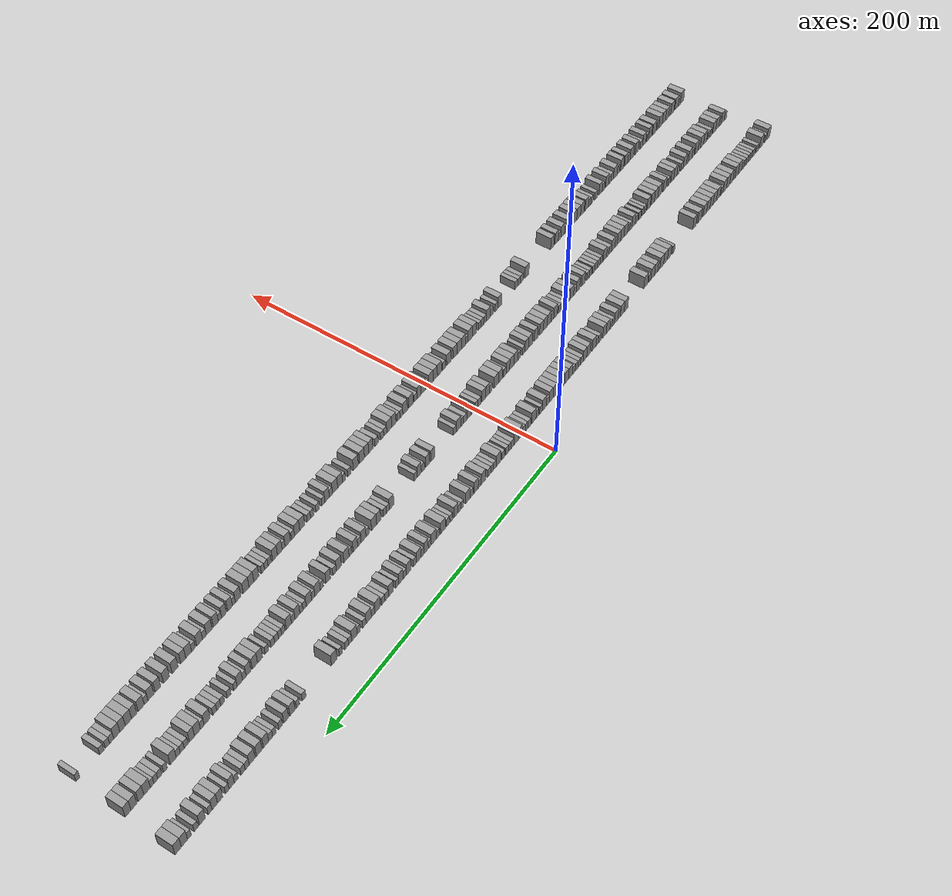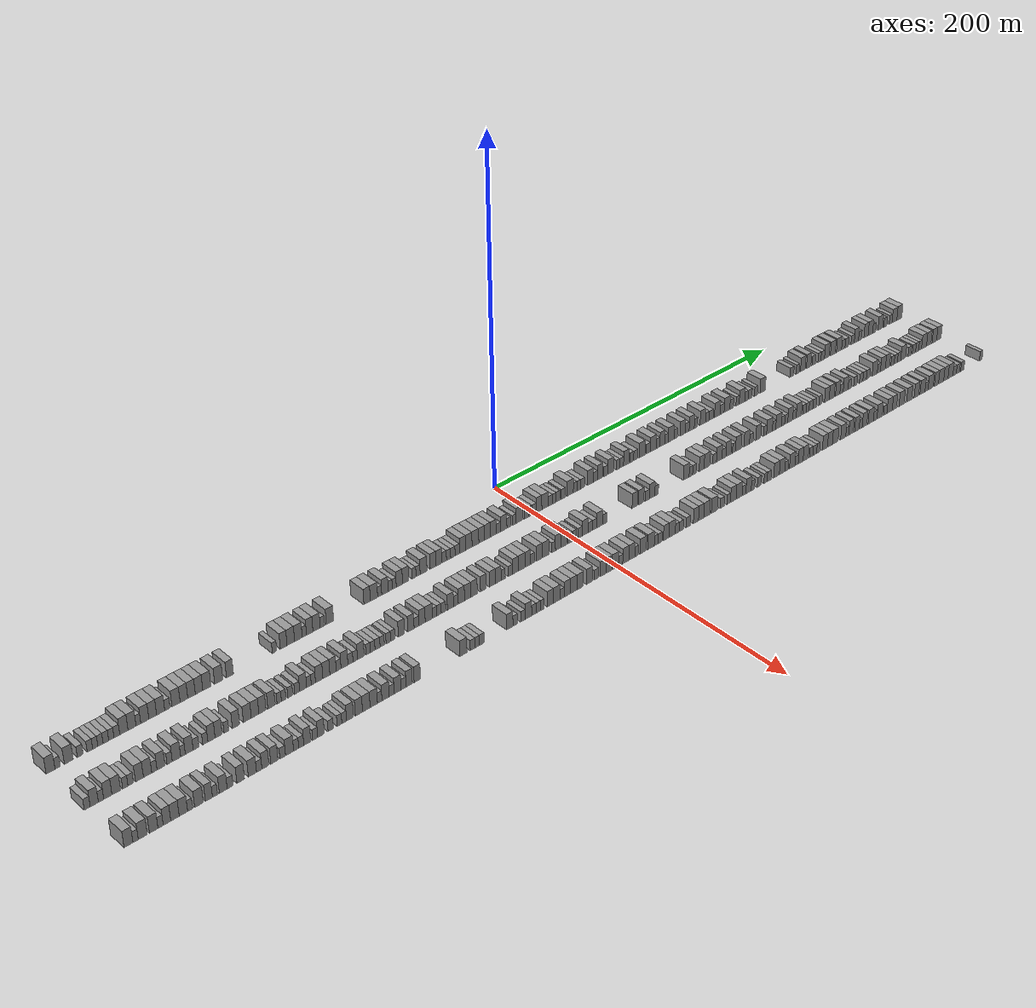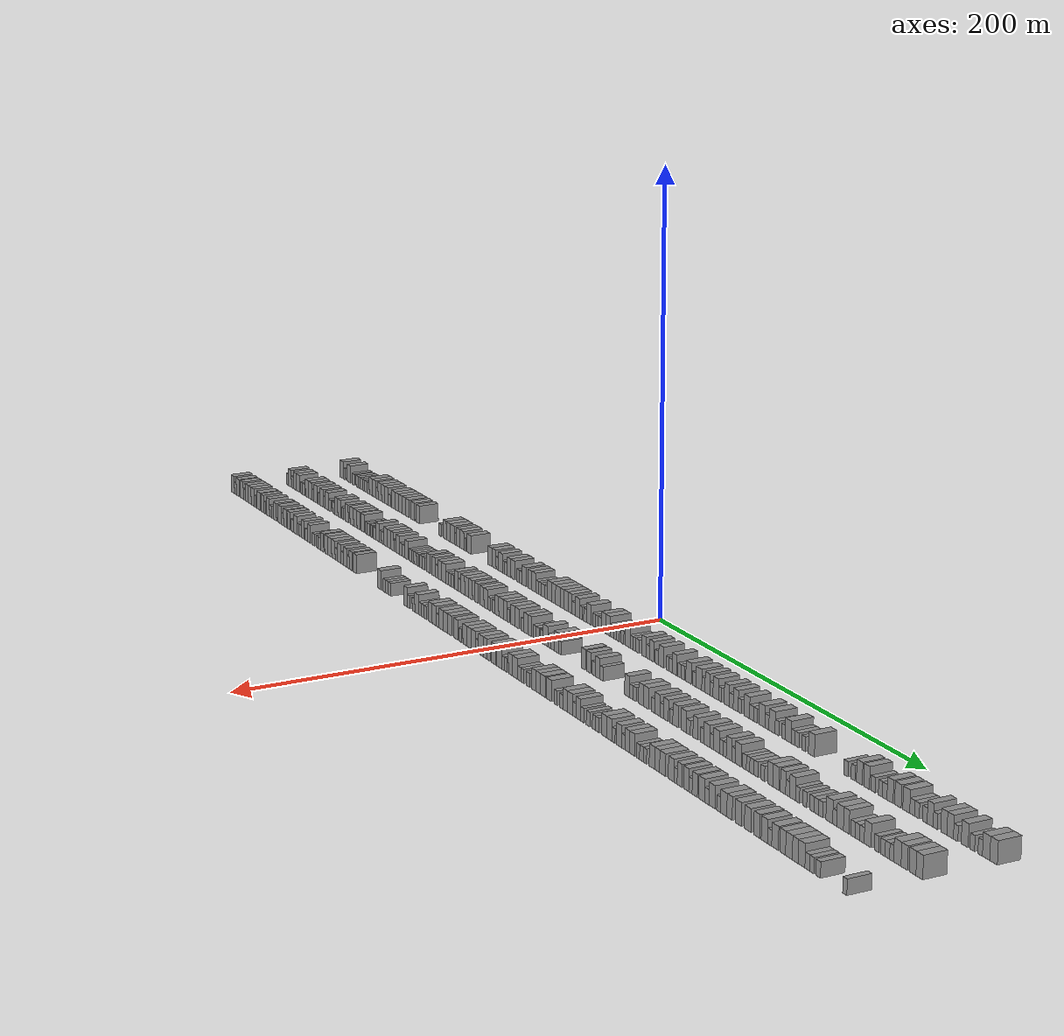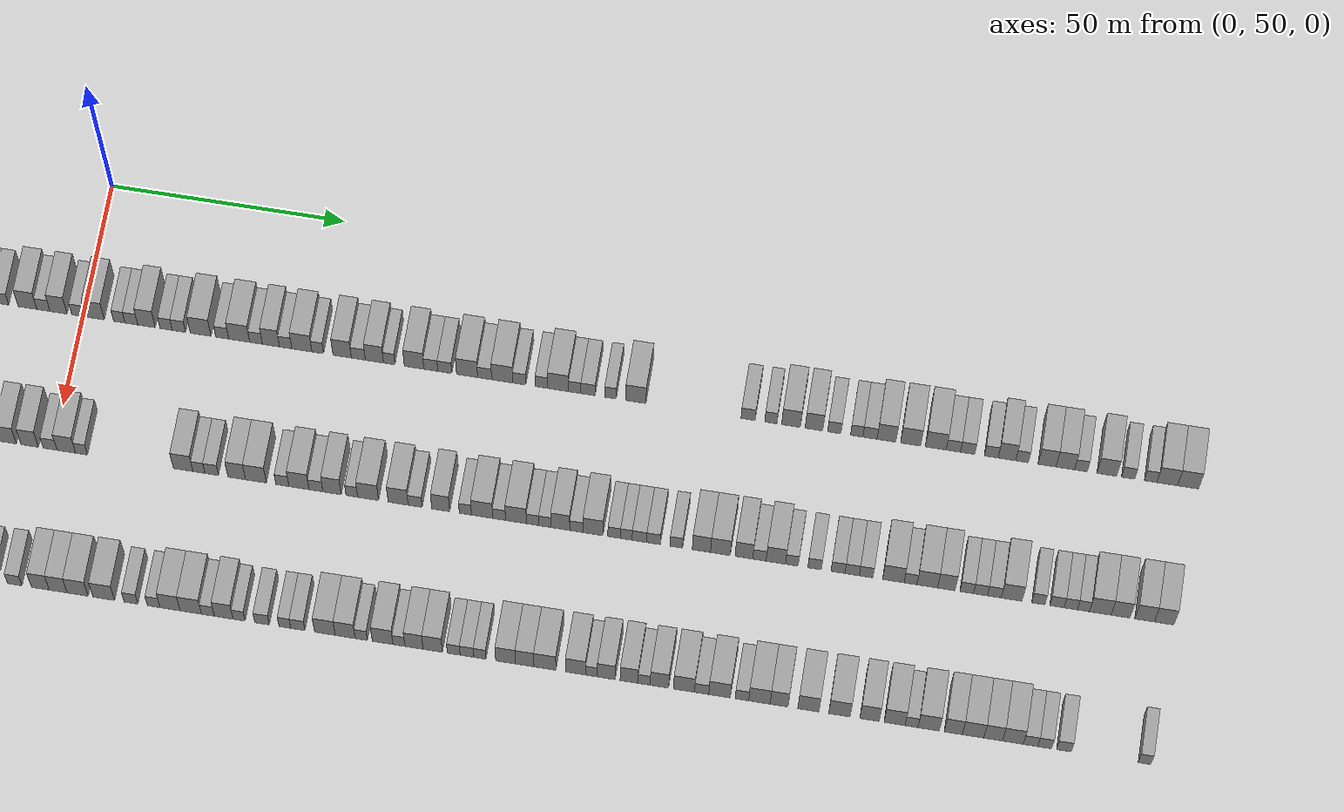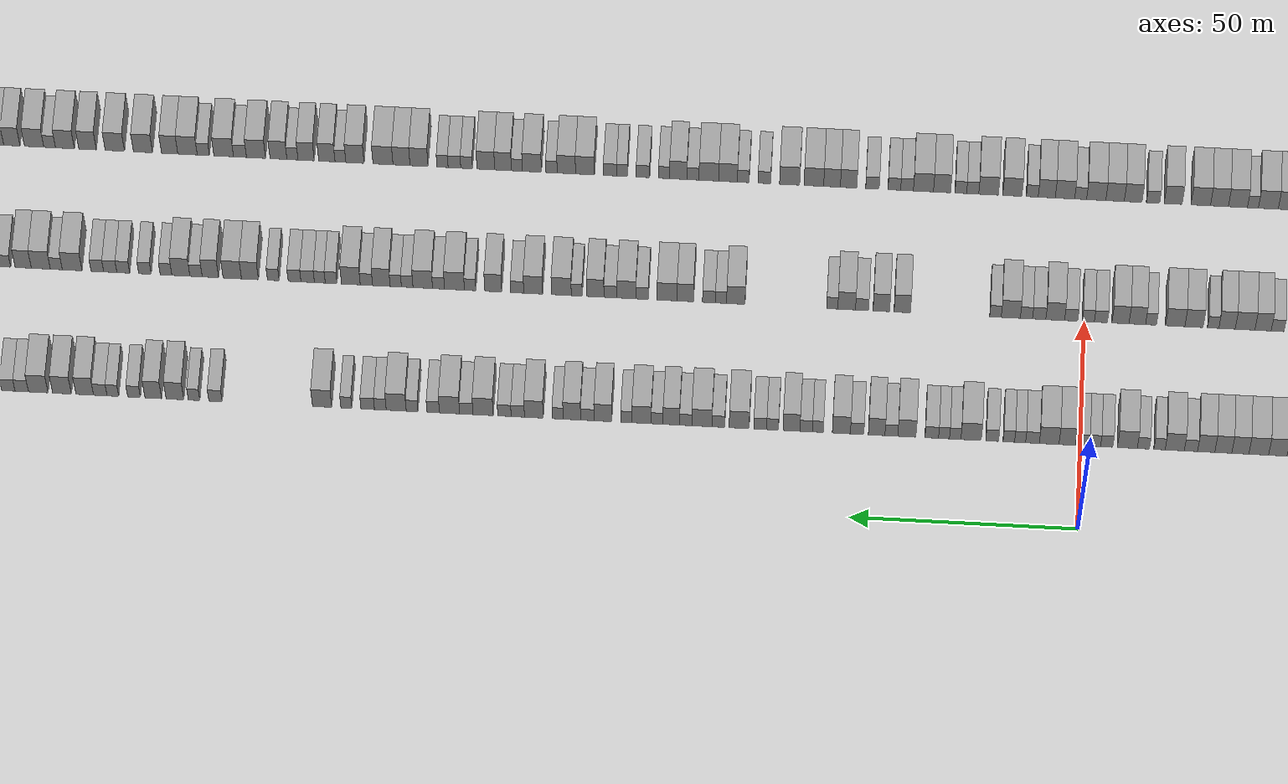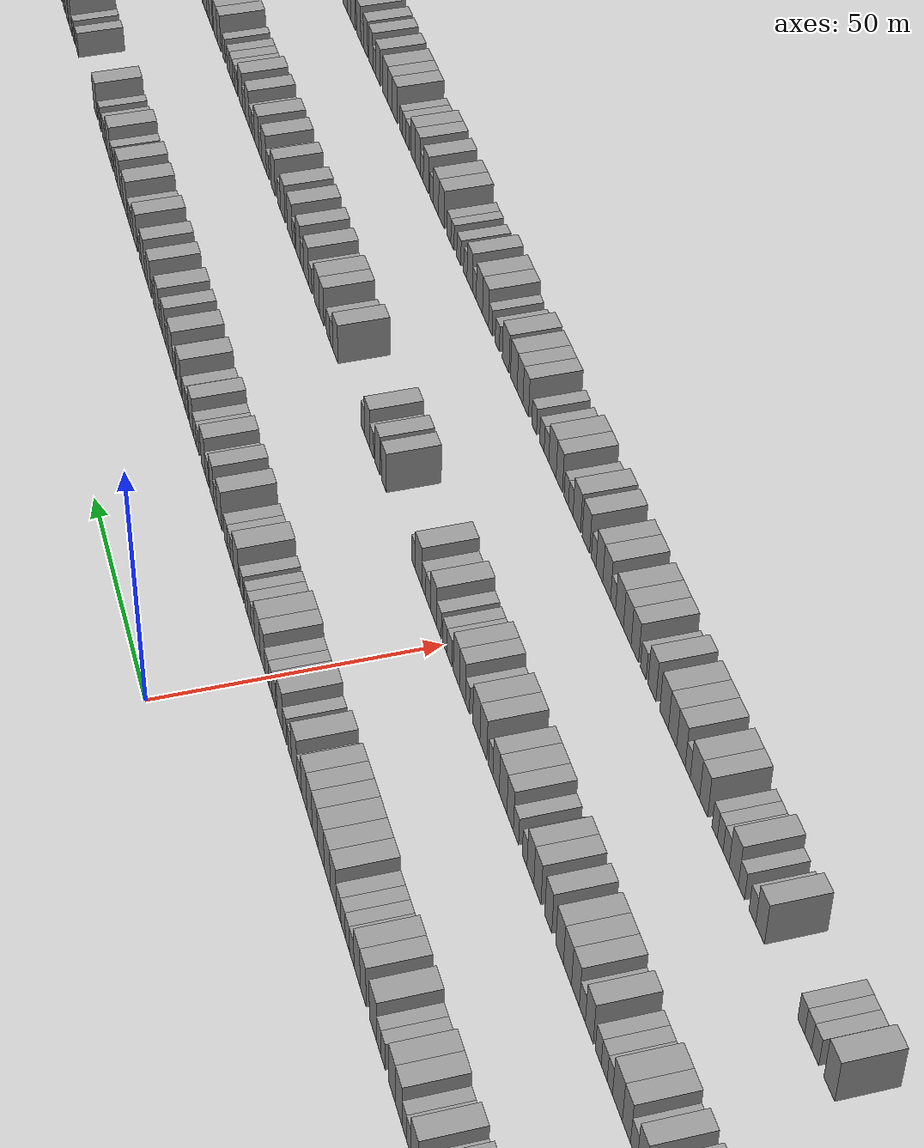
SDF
<sdf version="1.6">
 <world name="default">
  <scene>
   <sky><clouds><speed>12</speed></clouds></sky>
   <ambient>0.4 0.4 0.4 1</ambient>
   <background>0.7 0.7 0.7 1</background>
   <shadows>1</shadows>
  </scene>
  <gravity>0 0 -9.8066</gravity>
  <magnetic_field>6e-06 2.3e-05 -4.2e-05</magnetic_field>
  <physics default="0" name="default_physics" type="ode">
   <ode>
    <solver>
     <type>quick</type>
     <iters>10</iters>
     <sor>1.0</sor>
     <use_dynamic_moi_rescaling>0</use_dynamic_moi_rescaling>
    </solver>
    <constraints>
     <cfm>0</cfm>
     <erp>0.2</erp>
     <contact_max_correcting_vel>100</contact_max_correcting_vel>
     <contact_surface_layer>0.001</contact_surface_layer>
    </constraints>
   </ode>
   <max_step_size>0.004</max_step_size>
   <real_time_factor>1</real_time_factor>
   <real_time_update_rate>250</real_time_update_rate>
  </physics>
  <light name="sun" type="directional">
   <pose>0 0 10 0 0 0</pose>
   <diffuse>0.8 0.8 0.8 1</diffuse>
   <specular>0.2 0.2 0.2 1</specular>
   <attenuation>
    <range>1000</range>
    <constant>0.9</constant>
    <linear>0.01</linear>
    <quadratic>0.001</quadratic>
   </attenuation>
   <direction>-0.5 0.1 -0.9</direction>
  </light>
  <model name="building_1">
   <static>1</static>
   <pose>25.0000 -277.8074 0 0.000000 0.000000 0.000000</pose>
   <link name="link">
    <pose>0 0 4.50 0 0 0</pose>
    <collision name="collision"><geometry><box><size>10.0000 4.3852 9.0000</size></box></geometry></collision>
    <visual name="visual">
     <cast_shadows>0</cast_shadows>
     <geometry><box><size>10.0000 4.3852 9.0000</size></box></geometry>
     <material>
      <script>
       <uri>model://grey_wall/materials/scripts</uri>
       <uri>model://grey_wall/materials/textures</uri>
       <name>vrc/grey_wall</name>
      </script>
     </material>
    </visual>
   </link>
  </model>
  <model name="building_2">
   <static>1</static>
   <pose>25.0000 -274.3171 0 0.000000 0.000000 0.000000</pose>
   <link name="link">
    <pose>0 0 3.00 0 0 0</pose>
    <collision name="collision"><geometry><box><size>10.0000 2.5955 6.0000</size></box></geometry></collision>
    <visual name="visual">
     <cast_shadows>0</cast_shadows>
     <geometry><box><size>10.0000 2.5955 6.0000</size></box></geometry>
     <material>
      <script>
       <uri>model://grey_wall/materials/scripts</uri>
       <uri>model://grey_wall/materials/textures</uri>
       <name>vrc/grey_wall</name>
      </script>
     </material>
    </visual>
   </link>
  </model>
  <model name="building_3">
   <static>1</static>
   <pose>25.0000 -268.8242 0 0.000000 0.000000 0.000000</pose>
   <link name="link">
    <pose>0 0 4.50 0 0 0</pose>
    <collision name="collision"><geometry><box><size>10.0000 4.3903 9.0000</size></box></geometry></collision>
    <visual name="visual">
     <cast_shadows>0</cast_shadows>
     <geometry><box><size>10.0000 4.3903 9.0000</size></box></geometry>
     <material>
      <script>
       <uri>model://grey_wall/materials/scripts</uri>
       <uri>model://grey_wall/materials/textures</uri>
       <name>vrc/grey_wall</name>
      </script>
     </material>
    </visual>
   </link>
  </model>
  <model name="building_4">
   <static>1</static>
   <pose>25.0000 -263.1533 0 0.000000 0.000000 0.000000</pose>
   <link name="link">
    <pose>0 0 3.00 0 0 0</pose>
    <collision name="collision"><geometry><box><size>10.0000 2.9517 6.0000</size></box></geometry></collision>
    <visual name="visual">
     <cast_shadows>0</cast_shadows>
     <geometry><box><size>10.0000 2.9517 6.0000</size></box></geometry>
     <material>
      <script>
       <uri>model://grey_wall/materials/scripts</uri>
       <uri>model://grey_wall/materials/textures</uri>
       <name>vrc/grey_wall</name>
      </script>
     </material>
    </visual>
   </link>
  </model>
  <model name="building_5">
   <static>1</static>
   <pose>25.0000 -258.3207 0 0.000000 0.000000 0.000000</pose>
   <link name="link">
    <pose>0 0 3.00 0 0 0</pose>
    <collision name="collision"><geometry><box><size>10.0000 2.7135 6.0000</size></box></geometry></collision>
    <visual name="visual">
     <cast_shadows>0</cast_shadows>
     <geometry><box><size>10.0000 2.7135 6.0000</size></box></geometry>
     <material>
      <script>
       <uri>model://grey_wall/materials/scripts</uri>
       <uri>model://grey_wall/materials/textures</uri>
       <name>vrc/grey_wall</name>
      </script>
     </material>
    </visual>
   </link>
  </model>
  <model name="building_6">
   <static>1</static>
   <pose>25.0000 -255.6534 0 0.000000 0.000000 0.000000</pose>
   <link name="link">
    <pose>0 0 3.00 0 0 0</pose>
    <collision name="collision"><geometry><box><size>10.0000 2.6212 6.0000</size></box></geometry></collision>
    <visual name="visual">
     <cast_shadows>0</cast_shadows>
     <geometry><box><size>10.0000 2.6212 6.0000</size></box></geometry>
     <material>
      <script>
       <uri>model://grey_wall/materials/scripts</uri>
       <uri>model://grey_wall/materials/textures</uri>
       <name>vrc/grey_wall</name>
      </script>
     </material>
    </visual>
   </link>
  </model>
  <model name="building_7">
   <static>1</static>
   <pose>25.0000 -253.0103 0 0.000000 0.000000 0.000000</pose>
   <link name="link">
    <pose>0 0 3.00 0 0 0</pose>
    <collision name="collision"><geometry><box><size>10.0000 2.6650 6.0000</size></box></geometry></collision>
    <visual name="visual">
     <cast_shadows>0</cast_shadows>
     <geometry><box><size>10.0000 2.6650 6.0000</size></box></geometry>
     <material>
      <script>
       <uri>model://grey_wall/materials/scripts</uri>
       <uri>model://grey_wall/materials/textures</uri>
       <name>vrc/grey_wall</name>
      </script>
     </material>
    </visual>
   </link>
  </model>
  <model name="building_8">
   <static>1</static>
   <pose>25.0000 -250.2612 0 0.000000 0.000000 0.000000</pose>
   <link name="link">
    <pose>0 0 3.00 0 0 0</pose>
    <collision name="collision"><geometry><box><size>10.0000 2.8333 6.0000</size></box></geometry></collision>
    <visual name="visual">
     <cast_shadows>0</cast_shadows>
     <geometry><box><size>10.0000 2.8333 6.0000</size></box></geometry>
     <material>
      <script>
       <uri>model://grey_wall/materials/scripts</uri>
       <uri>model://grey_wall/materials/textures</uri>
       <name>vrc/grey_wall</name>
      </script>
     </material>
    </visual>
   </link>
  </model>
  <model name="building_9">
   <static>1</static>
   <pose>25.0000 -247.5011 0 0.000000 0.000000 0.000000</pose>
   <link name="link">
    <pose>0 0 3.00 0 0 0</pose>
    <collision name="collision"><geometry><box><size>10.0000 2.6869 6.0000</size></box></geometry></collision>
    <visual name="visual">
     <cast_shadows>0</cast_shadows>
     <geometry><box><size>10.0000 2.6869 6.0000</size></box></geometry>
     <material>
      <script>
       <uri>model://grey_wall/materials/scripts</uri>
       <uri>model://grey_wall/materials/textures</uri>
       <name>vrc/grey_wall</name>
      </script>
     </material>
    </visual>
   </link>
  </model>
  <model name="building_10">
   <static>1</static>
   <pose>25.0000 -244.6979 0 0.000000 0.000000 0.000000</pose>
   <link name="link">
    <pose>0 0 3.00 0 0 0</pose>
    <collision name="collision"><geometry><box><size>10.0000 2.9194 6.0000</size></box></geometry></collision>
    <visual name="visual">
     <cast_shadows>0</cast_shadows>
     <geometry><box><size>10.0000 2.9194 6.0000</size></box></geometry>
     <material>
      <script>
       <uri>model://grey_wall/materials/scripts</uri>
       <uri>model://grey_wall/materials/textures</uri>
       <name>vrc/grey_wall</name>
      </script>
     </material>
    </visual>
   </link>
  </model>
  <model name="building_11">
   <static>1</static>
   <pose>25.0000 -241.1214 0 0.000000 0.000000 0.000000</pose>
   <link name="link">
    <pose>0 0 4.50 0 0 0</pose>
    <collision name="collision"><geometry><box><size>10.0000 4.2337 9.0000</size></box></geometry></collision>
    <visual name="visual">
     <cast_shadows>0</cast_shadows>
     <geometry><box><size>10.0000 4.2337 9.0000</size></box></geometry>
     <material>
      <script>
       <uri>model://grey_wall/materials/scripts</uri>
       <uri>model://grey_wall/materials/textures</uri>
       <name>vrc/grey_wall</name>
      </script>
     </material>
    </visual>
   </link>
  </model>
  <model name="building_12">
   <static>1</static>
   <pose>25.0000 -236.9326 0 0.000000 0.000000 0.000000</pose>
   <link name="link">
    <pose>0 0 4.50 0 0 0</pose>
    <collision name="collision"><geometry><box><size>10.0000 4.1439 9.0000</size></box></geometry></collision>
    <visual name="visual">
     <cast_shadows>0</cast_shadows>
     <geometry><box><size>10.0000 4.1439 9.0000</size></box></geometry>
     <material>
      <script>
       <uri>model://grey_wall/materials/scripts</uri>
       <uri>model://grey_wall/materials/textures</uri>
       <name>vrc/grey_wall</name>
      </script>
     </material>
    </visual>
   </link>
  </model>
  <model name="building_13">
   <static>1</static>
   <pose>25.0000 -233.6497 0 0.000000 0.000000 0.000000</pose>
   <link name="link">
    <pose>0 0 3.00 0 0 0</pose>
    <collision name="collision"><geometry><box><size>10.0000 2.4217 6.0000</size></box></geometry></collision>
    <visual name="visual">
     <cast_shadows>0</cast_shadows>
     <geometry><box><size>10.0000 2.4217 6.0000</size></box></geometry>
     <material>
      <script>
       <uri>model://grey_wall/materials/scripts</uri>
       <uri>model://grey_wall/materials/textures</uri>
       <name>vrc/grey_wall</name>
      </script>
     </material>
    </visual>
   </link>
  </model>
  <model name="building_14">
   <static>1</static>
   <pose>25.0000 -230.3244 0 0.000000 0.000000 0.000000</pose>
   <link name="link">
    <pose>0 0 4.50 0 0 0</pose>
    <collision name="collision"><geometry><box><size>10.0000 4.2289 9.0000</size></box></geometry></collision>
    <visual name="visual">
     <cast_shadows>0</cast_shadows>
     <geometry><box><size>10.0000 4.2289 9.0000</size></box></geometry>
     <material>
      <script>
       <uri>model://grey_wall/materials/scripts</uri>
       <uri>model://grey_wall/materials/textures</uri>
       <name>vrc/grey_wall</name>
      </script>
     </material>
    </visual>
   </link>
  </model>
  <model name="building_15">
   <static>1</static>
   <pose>25.0000 -226.2073 0 0.000000 0.000000 0.000000</pose>
   <link name="link">
    <pose>0 0 4.50 0 0 0</pose>
    <collision name="collision"><geometry><box><size>10.0000 4.0054 9.0000</size></box></geometry></collision>
    <visual name="visual">
     <cast_shadows>0</cast_shadows>
     <geometry><box><size>10.0000 4.0054 9.0000</size></box></geometry>
     <material>
      <script>
       <uri>model://grey_wall/materials/scripts</uri>
       <uri>model://grey_wall/materials/textures</uri>
       <name>vrc/grey_wall</name>
      </script>
     </material>
    </visual>
   </link>
  </model>
  <model name="building_16">
   <static>1</static>
   <pose>25.0000 -222.0700 0 0.000000 0.000000 0.000000</pose>
   <link name="link">
    <pose>0 0 4.50 0 0 0</pose>
    <collision name="collision"><geometry><box><size>10.0000 4.2691 9.0000</size></box></geometry></collision>
    <visual name="visual">
     <cast_shadows>0</cast_shadows>
     <geometry><box><size>10.0000 4.2691 9.0000</size></box></geometry>
     <material>
      <script>
       <uri>model://grey_wall/materials/scripts</uri>
       <uri>model://grey_wall/materials/textures</uri>
       <name>vrc/grey_wall</name>
      </script>
     </material>
    </visual>
   </link>
  </model>
  <model name="building_17">
   <static>1</static>
   <pose>25.0000 -218.5456 0 0.000000 0.000000 0.000000</pose>
   <link name="link">
    <pose>0 0 3.00 0 0 0</pose>
    <collision name="collision"><geometry><box><size>10.0000 2.7796 6.0000</size></box></geometry></collision>
    <visual name="visual">
     <cast_shadows>0</cast_shadows>
     <geometry><box><size>10.0000 2.7796 6.0000</size></box></geometry>
     <material>
      <script>
       <uri>model://grey_wall/materials/scripts</uri>
       <uri>model://grey_wall/materials/textures</uri>
       <name>vrc/grey_wall</name>
      </script>
     </material>
    </visual>
   </link>
  </model>
  <model name="building_18">
   <static>1</static>
   <pose>25.0000 -213.9851 0 0.000000 0.000000 0.000000</pose>
   <link name="link">
    <pose>0 0 4.50 0 0 0</pose>
    <collision name="collision"><geometry><box><size>10.0000 4.3414 9.0000</size></box></geometry></collision>
    <visual name="visual">
     <cast_shadows>0</cast_shadows>
     <geometry><box><size>10.0000 4.3414 9.0000</size></box></geometry>
     <material>
      <script>
       <uri>model://grey_wall/materials/scripts</uri>
       <uri>model://grey_wall/materials/textures</uri>
       <name>vrc/grey_wall</name>
      </script>
     </material>
    </visual>
   </link>
  </model>
  <model name="building_19">
   <static>1</static>
   <pose>25.0000 -209.7853 0 0.000000 0.000000 0.000000</pose>
   <link name="link">
    <pose>0 0 4.50 0 0 0</pose>
    <collision name="collision"><geometry><box><size>10.0000 4.0582 9.0000</size></box></geometry></collision>
    <visual name="visual">
     <cast_shadows>0</cast_shadows>
     <geometry><box><size>10.0000 4.0582 9.0000</size></box></geometry>
     <material>
      <script>
       <uri>model://grey_wall/materials/scripts</uri>
       <uri>model://grey_wall/materials/textures</uri>
       <name>vrc/grey_wall</name>
      </script>
     </material>
    </visual>
   </link>
  </model>
  <model name="building_20">
   <static>1</static>
   <pose>25.0000 -205.7376 0 0.000000 0.000000 0.000000</pose>
   <link name="link">
    <pose>0 0 4.50 0 0 0</pose>
    <collision name="collision"><geometry><box><size>10.0000 4.0372 9.0000</size></box></geometry></collision>
    <visual name="visual">
     <cast_shadows>0</cast_shadows>
     <geometry><box><size>10.0000 4.0372 9.0000</size></box></geometry>
     <material>
      <script>
       <uri>model://grey_wall/materials/scripts</uri>
       <uri>model://grey_wall/materials/textures</uri>
       <name>vrc/grey_wall</name>
      </script>
     </material>
    </visual>
   </link>
  </model>
  <model name="building_21">
   <static>1</static>
   <pose>25.0000 -201.7286 0 0.000000 0.000000 0.000000</pose>
   <link name="link">
    <pose>0 0 4.50 0 0 0</pose>
    <collision name="collision"><geometry><box><size>10.0000 3.9809 9.0000</size></box></geometry></collision>
    <visual name="visual">
     <cast_shadows>0</cast_shadows>
     <geometry><box><size>10.0000 3.9809 9.0000</size></box></geometry>
     <material>
      <script>
       <uri>model://grey_wall/materials/scripts</uri>
       <uri>model://grey_wall/materials/textures</uri>
       <name>vrc/grey_wall</name>
      </script>
     </material>
    </visual>
   </link>
  </model>
  <model name="building_22">
   <static>1</static>
   <pose>25.0000 -197.5421 0 0.000000 0.000000 0.000000</pose>
   <link name="link">
    <pose>0 0 4.50 0 0 0</pose>
    <collision name="collision"><geometry><box><size>10.0000 4.3920 9.0000</size></box></geometry></collision>
    <visual name="visual">
     <cast_shadows>0</cast_shadows>
     <geometry><box><size>10.0000 4.3920 9.0000</size></box></geometry>
     <material>
      <script>
       <uri>model://grey_wall/materials/scripts</uri>
       <uri>model://grey_wall/materials/textures</uri>
       <name>vrc/grey_wall</name>
      </script>
     </material>
    </visual>
   </link>
  </model>
  <model name="building_23">
   <static>1</static>
   <pose>25.0000 -191.1368 0 0.000000 0.000000 0.000000</pose>
   <link name="link">
    <pose>0 0 4.50 0 0 0</pose>
    <collision name="collision"><geometry><box><size>10.0000 4.4186 9.0000</size></box></geometry></collision>
    <visual name="visual">
     <cast_shadows>0</cast_shadows>
     <geometry><box><size>10.0000 4.4186 9.0000</size></box></geometry>
     <material>
      <script>
       <uri>model://grey_wall/materials/scripts</uri>
       <uri>model://grey_wall/materials/textures</uri>
       <name>vrc/grey_wall</name>
      </script>
     </material>
    </visual>
   </link>
  </model>
  <model name="building_24">
   <static>1</static>
   <pose>25.0000 -184.9893 0 0.000000 0.000000 0.000000</pose>
   <link name="link">
    <pose>0 0 4.50 0 0 0</pose>
    <collision name="collision"><geometry><box><size>10.0000 3.8763 9.0000</size></box></geometry></collision>
    <visual name="visual">
     <cast_shadows>0</cast_shadows>
     <geometry><box><size>10.0000 3.8763 9.0000</size></box></geometry>
     <material>
      <script>
       <uri>model://grey_wall/materials/scripts</uri>
       <uri>model://grey_wall/materials/textures</uri>
       <name>vrc/grey_wall</name>
      </script>
     </material>
    </visual>
   </link>
  </model>
  <model name="building_25">
   <static>1</static>
   <pose>25.0000 -160.2648 0 0.000000 0.000000 0.000000</pose>
   <link name="link">
    <pose>0 0 3.00 0 0 0</pose>
    <collision name="collision"><geometry><box><size>10.0000 2.5242 6.0000</size></box></geometry></collision>
    <visual name="visual">
     <cast_shadows>0</cast_shadows>
     <geometry><box><size>10.0000 2.5242 6.0000</size></box></geometry>
     <material>
      <script>
       <uri>model://grey_wall/materials/scripts</uri>
       <uri>model://grey_wall/materials/textures</uri>
       <name>vrc/grey_wall</name>
      </script>
     </material>
    </visual>
   </link>
  </model>
  <model name="building_26">
   <static>1</static>
   <pose>25.0000 -155.0980 0 0.000000 0.000000 0.000000</pose>
   <link name="link">
    <pose>0 0 4.50 0 0 0</pose>
    <collision name="collision"><geometry><box><size>10.0000 3.8093 9.0000</size></box></geometry></collision>
    <visual name="visual">
     <cast_shadows>0</cast_shadows>
     <geometry><box><size>10.0000 3.8093 9.0000</size></box></geometry>
     <material>
      <script>
       <uri>model://grey_wall/materials/scripts</uri>
       <uri>model://grey_wall/materials/textures</uri>
       <name>vrc/grey_wall</name>
      </script>
     </material>
    </visual>
   </link>
  </model>
  <model name="building_27">
   <static>1</static>
   <pose>25.0000 -151.0270 0 0.000000 0.000000 0.000000</pose>
   <link name="link">
    <pose>0 0 4.50 0 0 0</pose>
    <collision name="collision"><geometry><box><size>10.0000 4.3329 9.0000</size></box></geometry></collision>
    <visual name="visual">
     <cast_shadows>0</cast_shadows>
     <geometry><box><size>10.0000 4.3329 9.0000</size></box></geometry>
     <material>
      <script>
       <uri>model://grey_wall/materials/scripts</uri>
       <uri>model://grey_wall/materials/textures</uri>
       <name>vrc/grey_wall</name>
      </script>
     </material>
    </visual>
   </link>
  </model>
  <model name="building_28">
   <static>1</static>
   <pose>25.0000 -146.6813 0 0.000000 0.000000 0.000000</pose>
   <link name="link">
    <pose>0 0 4.50 0 0 0</pose>
    <collision name="collision"><geometry><box><size>10.0000 4.3583 9.0000</size></box></geometry></collision>
    <visual name="visual">
     <cast_shadows>0</cast_shadows>
     <geometry><box><size>10.0000 4.3583 9.0000</size></box></geometry>
     <material>
      <script>
       <uri>model://grey_wall/materials/scripts</uri>
       <uri>model://grey_wall/materials/textures</uri>
       <name>vrc/grey_wall</name>
      </script>
     </material>
    </visual>
   </link>
  </model>
  <model name="building_29">
   <static>1</static>
   <pose>25.0000 -143.2896 0 0.000000 0.000000 0.000000</pose>
   <link name="link">
    <pose>0 0 3.00 0 0 0</pose>
    <collision name="collision"><geometry><box><size>10.0000 2.4252 6.0000</size></box></geometry></collision>
    <visual name="visual">
     <cast_shadows>0</cast_shadows>
     <geometry><box><size>10.0000 2.4252 6.0000</size></box></geometry>
     <material>
      <script>
       <uri>model://grey_wall/materials/scripts</uri>
       <uri>model://grey_wall/materials/textures</uri>
       <name>vrc/grey_wall</name>
      </script>
     </material>
    </visual>
   </link>
  </model>
  <model name="building_30">
   <static>1</static>
   <pose>25.0000 -140.2094 0 0.000000 0.000000 0.000000</pose>
   <link name="link">
    <pose>0 0 4.50 0 0 0</pose>
    <collision name="collision"><geometry><box><size>10.0000 3.7352 9.0000</size></box></geometry></collision>
    <visual name="visual">
     <cast_shadows>0</cast_shadows>
     <geometry><box><size>10.0000 3.7352 9.0000</size></box></geometry>
     <material>
      <script>
       <uri>model://grey_wall/materials/scripts</uri>
       <uri>model://grey_wall/materials/textures</uri>
       <name>vrc/grey_wall</name>
      </script>
     </material>
    </visual>
   </link>
  </model>
  <model name="building_31">
   <static>1</static>
   <pose>25.0000 -136.2320 0 0.000000 0.000000 0.000000</pose>
   <link name="link">
    <pose>0 0 4.50 0 0 0</pose>
    <collision name="collision"><geometry><box><size>10.0000 4.2196 9.0000</size></box></geometry></collision>
    <visual name="visual">
     <cast_shadows>0</cast_shadows>
     <geometry><box><size>10.0000 4.2196 9.0000</size></box></geometry>
     <material>
      <script>
       <uri>model://grey_wall/materials/scripts</uri>
       <uri>model://grey_wall/materials/textures</uri>
       <name>vrc/grey_wall</name>
      </script>
     </material>
    </visual>
   </link>
  </model>
  <model name="building_32">
   <static>1</static>
   <pose>25.0000 -132.8708 0 0.000000 0.000000 0.000000</pose>
   <link name="link">
    <pose>0 0 3.00 0 0 0</pose>
    <collision name="collision"><geometry><box><size>10.0000 2.5028 6.0000</size></box></geometry></collision>
    <visual name="visual">
     <cast_shadows>0</cast_shadows>
     <geometry><box><size>10.0000 2.5028 6.0000</size></box></geometry>
     <material>
      <script>
       <uri>model://grey_wall/materials/scripts</uri>
       <uri>model://grey_wall/materials/textures</uri>
       <name>vrc/grey_wall</name>
      </script>
     </material>
    </visual>
   </link>
  </model>
  <model name="building_33">
   <static>1</static>
   <pose>25.0000 -128.4761 0 0.000000 0.000000 0.000000</pose>
   <link name="link">
    <pose>0 0 4.50 0 0 0</pose>
    <collision name="collision"><geometry><box><size>10.0000 4.2866 9.0000</size></box></geometry></collision>
    <visual name="visual">
     <cast_shadows>0</cast_shadows>
     <geometry><box><size>10.0000 4.2866 9.0000</size></box></geometry>
     <material>
      <script>
       <uri>model://grey_wall/materials/scripts</uri>
       <uri>model://grey_wall/materials/textures</uri>
       <name>vrc/grey_wall</name>
      </script>
     </material>
    </visual>
   </link>
  </model>
  <model name="building_34">
   <static>1</static>
   <pose>25.0000 -106.4700 0 0.000000 0.000000 0.000000</pose>
   <link name="link">
    <pose>0 0 4.50 0 0 0</pose>
    <collision name="collision"><geometry><box><size>10.0000 3.9086 9.0000</size></box></geometry></collision>
    <visual name="visual">
     <cast_shadows>0</cast_shadows>
     <geometry><box><size>10.0000 3.9086 9.0000</size></box></geometry>
     <material>
      <script>
       <uri>model://grey_wall/materials/scripts</uri>
       <uri>model://grey_wall/materials/textures</uri>
       <name>vrc/grey_wall</name>
      </script>
     </material>
    </visual>
   </link>
  </model>
  <model name="building_35">
   <static>1</static>
   <pose>25.0000 -102.3288 0 0.000000 0.000000 0.000000</pose>
   <link name="link">
    <pose>0 0 4.50 0 0 0</pose>
    <collision name="collision"><geometry><box><size>10.0000 4.3737 9.0000</size></box></geometry></collision>
    <visual name="visual">
     <cast_shadows>0</cast_shadows>
     <geometry><box><size>10.0000 4.3737 9.0000</size></box></geometry>
     <material>
      <script>
       <uri>model://grey_wall/materials/scripts</uri>
       <uri>model://grey_wall/materials/textures</uri>
       <name>vrc/grey_wall</name>
      </script>
     </material>
    </visual>
   </link>
  </model>
  <model name="building_36">
   <static>1</static>
   <pose>25.0000 -98.9074 0 0.000000 0.000000 0.000000</pose>
   <link name="link">
    <pose>0 0 3.00 0 0 0</pose>
    <collision name="collision"><geometry><box><size>10.0000 2.4693 6.0000</size></box></geometry></collision>
    <visual name="visual">
     <cast_shadows>0</cast_shadows>
     <geometry><box><size>10.0000 2.4693 6.0000</size></box></geometry>
     <material>
      <script>
       <uri>model://grey_wall/materials/scripts</uri>
       <uri>model://grey_wall/materials/textures</uri>
       <name>vrc/grey_wall</name>
      </script>
     </material>
    </visual>
   </link>
  </model>
  <model name="building_37">
   <static>1</static>
   <pose>25.0000 -95.6918 0 0.000000 0.000000 0.000000</pose>
   <link name="link">
    <pose>0 0 4.50 0 0 0</pose>
    <collision name="collision"><geometry><box><size>10.0000 3.9618 9.0000</size></box></geometry></collision>
    <visual name="visual">
     <cast_shadows>0</cast_shadows>
     <geometry><box><size>10.0000 3.9618 9.0000</size></box></geometry>
     <material>
      <script>
       <uri>model://grey_wall/materials/scripts</uri>
       <uri>model://grey_wall/materials/textures</uri>
       <name>vrc/grey_wall</name>
      </script>
     </material>
    </visual>
   </link>
  </model>
  <model name="building_38">
   <static>1</static>
   <pose>25.0000 -92.4772 0 0.000000 0.000000 0.000000</pose>
   <link name="link">
    <pose>0 0 3.00 0 0 0</pose>
    <collision name="collision"><geometry><box><size>10.0000 2.4674 6.0000</size></box></geometry></collision>
    <visual name="visual">
     <cast_shadows>0</cast_shadows>
     <geometry><box><size>10.0000 2.4674 6.0000</size></box></geometry>
     <material>
      <script>
       <uri>model://grey_wall/materials/scripts</uri>
       <uri>model://grey_wall/materials/textures</uri>
       <name>vrc/grey_wall</name>
      </script>
     </material>
    </visual>
   </link>
  </model>
  <model name="building_39">
   <static>1</static>
   <pose>25.0000 -90.0292 0 0.000000 0.000000 0.000000</pose>
   <link name="link">
    <pose>0 0 3.00 0 0 0</pose>
    <collision name="collision"><geometry><box><size>10.0000 2.4285 6.0000</size></box></geometry></collision>
    <visual name="visual">
     <cast_shadows>0</cast_shadows>
     <geometry><box><size>10.0000 2.4285 6.0000</size></box></geometry>
     <material>
      <script>
       <uri>model://grey_wall/materials/scripts</uri>
       <uri>model://grey_wall/materials/textures</uri>
       <name>vrc/grey_wall</name>
      </script>
     </material>
    </visual>
   </link>
  </model>
  <model name="building_40">
   <static>1</static>
   <pose>25.0000 -86.8956 0 0.000000 0.000000 0.000000</pose>
   <link name="link">
    <pose>0 0 4.50 0 0 0</pose>
    <collision name="collision"><geometry><box><size>10.0000 3.8388 9.0000</size></box></geometry></collision>
    <visual name="visual">
     <cast_shadows>0</cast_shadows>
     <geometry><box><size>10.0000 3.8388 9.0000</size></box></geometry>
     <material>
      <script>
       <uri>model://grey_wall/materials/scripts</uri>
       <uri>model://grey_wall/materials/textures</uri>
       <name>vrc/grey_wall</name>
      </script>
     </material>
    </visual>
   </link>
  </model>
  <model name="building_41">
   <static>1</static>
   <pose>25.0000 -83.0619 0 0.000000 0.000000 0.000000</pose>
   <link name="link">
    <pose>0 0 4.50 0 0 0</pose>
    <collision name="collision"><geometry><box><size>10.0000 3.8285 9.0000</size></box></geometry></collision>
    <visual name="visual">
     <cast_shadows>0</cast_shadows>
     <geometry><box><size>10.0000 3.8285 9.0000</size></box></geometry>
     <material>
      <script>
       <uri>model://grey_wall/materials/scripts</uri>
       <uri>model://grey_wall/materials/textures</uri>
       <name>vrc/grey_wall</name>
      </script>
     </material>
    </visual>
   </link>
  </model>
  <model name="building_42">
   <static>1</static>
   <pose>25.0000 -77.9170 0 0.000000 0.000000 0.000000</pose>
   <link name="link">
    <pose>0 0 3.00 0 0 0</pose>
    <collision name="collision"><geometry><box><size>10.0000 2.4614 6.0000</size></box></geometry></collision>
    <visual name="visual">
     <cast_shadows>0</cast_shadows>
     <geometry><box><size>10.0000 2.4614 6.0000</size></box></geometry>
     <material>
      <script>
       <uri>model://grey_wall/materials/scripts</uri>
       <uri>model://grey_wall/materials/textures</uri>
       <name>vrc/grey_wall</name>
      </script>
     </material>
    </visual>
   </link>
  </model>
  <model name="building_43">
   <static>1</static>
   <pose>25.0000 -75.4098 0 0.000000 0.000000 0.000000</pose>
   <link name="link">
    <pose>0 0 3.00 0 0 0</pose>
    <collision name="collision"><geometry><box><size>10.0000 2.5529 6.0000</size></box></geometry></collision>
    <visual name="visual">
     <cast_shadows>0</cast_shadows>
     <geometry><box><size>10.0000 2.5529 6.0000</size></box></geometry>
     <material>
      <script>
       <uri>model://grey_wall/materials/scripts</uri>
       <uri>model://grey_wall/materials/textures</uri>
       <name>vrc/grey_wall</name>
      </script>
     </material>
    </visual>
   </link>
  </model>
  <model name="building_44">
   <static>1</static>
   <pose>25.0000 -71.9886 0 0.000000 0.000000 0.000000</pose>
   <link name="link">
    <pose>0 0 4.50 0 0 0</pose>
    <collision name="collision"><geometry><box><size>10.0000 4.2896 9.0000</size></box></geometry></collision>
    <visual name="visual">
     <cast_shadows>0</cast_shadows>
     <geometry><box><size>10.0000 4.2896 9.0000</size></box></geometry>
     <material>
      <script>
       <uri>model://grey_wall/materials/scripts</uri>
       <uri>model://grey_wall/materials/textures</uri>
       <name>vrc/grey_wall</name>
      </script>
     </material>
    </visual>
   </link>
  </model>
  <model name="building_45">
   <static>1</static>
   <pose>25.0000 -66.0244 0 0.000000 0.000000 0.000000</pose>
   <link name="link">
    <pose>0 0 4.50 0 0 0</pose>
    <collision name="collision"><geometry><box><size>10.0000 3.6387 9.0000</size></box></geometry></collision>
    <visual name="visual">
     <cast_shadows>0</cast_shadows>
     <geometry><box><size>10.0000 3.6387 9.0000</size></box></geometry>
     <material>
      <script>
       <uri>model://grey_wall/materials/scripts</uri>
       <uri>model://grey_wall/materials/textures</uri>
       <name>vrc/grey_wall</name>
      </script>
     </material>
    </visual>
   </link>
  </model>
  <model name="building_46">
   <static>1</static>
   <pose>25.0000 -62.3112 0 0.000000 0.000000 0.000000</pose>
   <link name="link">
    <pose>0 0 4.50 0 0 0</pose>
    <collision name="collision"><geometry><box><size>10.0000 3.7878 9.0000</size></box></geometry></collision>
    <visual name="visual">
     <cast_shadows>0</cast_shadows>
     <geometry><box><size>10.0000 3.7878 9.0000</size></box></geometry>
     <material>
      <script>
       <uri>model://grey_wall/materials/scripts</uri>
       <uri>model://grey_wall/materials/textures</uri>
       <name>vrc/grey_wall</name>
      </script>
     </material>
    </visual>
   </link>
  </model>
  <model name="building_47">
   <static>1</static>
   <pose>25.0000 -59.0134 0 0.000000 0.000000 0.000000</pose>
   <link name="link">
    <pose>0 0 3.00 0 0 0</pose>
    <collision name="collision"><geometry><box><size>10.0000 2.8077 6.0000</size></box></geometry></collision>
    <visual name="visual">
     <cast_shadows>0</cast_shadows>
     <geometry><box><size>10.0000 2.8077 6.0000</size></box></geometry>
     <material>
      <script>
       <uri>model://grey_wall/materials/scripts</uri>
       <uri>model://grey_wall/materials/textures</uri>
       <name>vrc/grey_wall</name>
      </script>
     </material>
    </visual>
   </link>
  </model>
  <model name="building_48">
   <static>1</static>
   <pose>25.0000 -56.2859 0 0.000000 0.000000 0.000000</pose>
   <link name="link">
    <pose>0 0 3.00 0 0 0</pose>
    <collision name="collision"><geometry><box><size>10.0000 2.6474 6.0000</size></box></geometry></collision>
    <visual name="visual">
     <cast_shadows>0</cast_shadows>
     <geometry><box><size>10.0000 2.6474 6.0000</size></box></geometry>
     <material>
      <script>
       <uri>model://grey_wall/materials/scripts</uri>
       <uri>model://grey_wall/materials/textures</uri>
       <name>vrc/grey_wall</name>
      </script>
     </material>
    </visual>
   </link>
  </model>
  <model name="building_49">
   <static>1</static>
   <pose>25.0000 -53.5529 0 0.000000 0.000000 0.000000</pose>
   <link name="link">
    <pose>0 0 3.00 0 0 0</pose>
    <collision name="collision"><geometry><box><size>10.0000 2.8187 6.0000</size></box></geometry></collision>
    <visual name="visual">
     <cast_shadows>0</cast_shadows>
     <geometry><box><size>10.0000 2.8187 6.0000</size></box></geometry>
     <material>
      <script>
       <uri>model://grey_wall/materials/scripts</uri>
       <uri>model://grey_wall/materials/textures</uri>
       <name>vrc/grey_wall</name>
      </script>
     </material>
    </visual>
   </link>
  </model>
  <model name="building_50">
   <static>1</static>
   <pose>25.0000 -50.6785 0 0.000000 0.000000 0.000000</pose>
   <link name="link">
    <pose>0 0 3.00 0 0 0</pose>
    <collision name="collision"><geometry><box><size>10.0000 2.9302 6.0000</size></box></geometry></collision>
    <visual name="visual">
     <cast_shadows>0</cast_shadows>
     <geometry><box><size>10.0000 2.9302 6.0000</size></box></geometry>
     <material>
      <script>
       <uri>model://grey_wall/materials/scripts</uri>
       <uri>model://grey_wall/materials/textures</uri>
       <name>vrc/grey_wall</name>
      </script>
     </material>
    </visual>
   </link>
  </model>
  <model name="building_51">
   <static>1</static>
   <pose>25.0000 -47.2622 0 0.000000 0.000000 0.000000</pose>
   <link name="link">
    <pose>0 0 4.50 0 0 0</pose>
    <collision name="collision"><geometry><box><size>10.0000 3.9024 9.0000</size></box></geometry></collision>
    <visual name="visual">
     <cast_shadows>0</cast_shadows>
     <geometry><box><size>10.0000 3.9024 9.0000</size></box></geometry>
     <material>
      <script>
       <uri>model://grey_wall/materials/scripts</uri>
       <uri>model://grey_wall/materials/textures</uri>
       <name>vrc/grey_wall</name>
      </script>
     </material>
    </visual>
   </link>
  </model>
  <model name="building_52">
   <static>1</static>
   <pose>25.0000 -43.2851 0 0.000000 0.000000 0.000000</pose>
   <link name="link">
    <pose>0 0 4.50 0 0 0</pose>
    <collision name="collision"><geometry><box><size>10.0000 4.0517 9.0000</size></box></geometry></collision>
    <visual name="visual">
     <cast_shadows>0</cast_shadows>
     <geometry><box><size>10.0000 4.0517 9.0000</size></box></geometry>
     <material>
      <script>
       <uri>model://grey_wall/materials/scripts</uri>
       <uri>model://grey_wall/materials/textures</uri>
       <name>vrc/grey_wall</name>
      </script>
     </material>
    </visual>
   </link>
  </model>
  <model name="building_53">
   <static>1</static>
   <pose>25.0000 -39.0970 0 0.000000 0.000000 0.000000</pose>
   <link name="link">
    <pose>0 0 4.50 0 0 0</pose>
    <collision name="collision"><geometry><box><size>10.0000 4.3244 9.0000</size></box></geometry></collision>
    <visual name="visual">
     <cast_shadows>0</cast_shadows>
     <geometry><box><size>10.0000 4.3244 9.0000</size></box></geometry>
     <material>
      <script>
       <uri>model://grey_wall/materials/scripts</uri>
       <uri>model://grey_wall/materials/textures</uri>
       <name>vrc/grey_wall</name>
      </script>
     </material>
    </visual>
   </link>
  </model>
  <model name="building_54">
   <static>1</static>
   <pose>25.0000 -35.0695 0 0.000000 0.000000 0.000000</pose>
   <link name="link">
    <pose>0 0 4.50 0 0 0</pose>
    <collision name="collision"><geometry><box><size>10.0000 3.7307 9.0000</size></box></geometry></collision>
    <visual name="visual">
     <cast_shadows>0</cast_shadows>
     <geometry><box><size>10.0000 3.7307 9.0000</size></box></geometry>
     <material>
      <script>
       <uri>model://grey_wall/materials/scripts</uri>
       <uri>model://grey_wall/materials/textures</uri>
       <name>vrc/grey_wall</name>
      </script>
     </material>
    </visual>
   </link>
  </model>
  <model name="building_55">
   <static>1</static>
   <pose>25.0000 -31.3385 0 0.000000 0.000000 0.000000</pose>
   <link name="link">
    <pose>0 0 4.50 0 0 0</pose>
    <collision name="collision"><geometry><box><size>10.0000 3.7313 9.0000</size></box></geometry></collision>
    <visual name="visual">
     <cast_shadows>0</cast_shadows>
     <geometry><box><size>10.0000 3.7313 9.0000</size></box></geometry>
     <material>
      <script>
       <uri>model://grey_wall/materials/scripts</uri>
       <uri>model://grey_wall/materials/textures</uri>
       <name>vrc/grey_wall</name>
      </script>
     </material>
    </visual>
   </link>
  </model>
  <model name="building_56">
   <static>1</static>
   <pose>25.0000 -27.5776 0 0.000000 0.000000 0.000000</pose>
   <link name="link">
    <pose>0 0 4.50 0 0 0</pose>
    <collision name="collision"><geometry><box><size>10.0000 3.7907 9.0000</size></box></geometry></collision>
    <visual name="visual">
     <cast_shadows>0</cast_shadows>
     <geometry><box><size>10.0000 3.7907 9.0000</size></box></geometry>
     <material>
      <script>
       <uri>model://grey_wall/materials/scripts</uri>
       <uri>model://grey_wall/materials/textures</uri>
       <name>vrc/grey_wall</name>
      </script>
     </material>
    </visual>
   </link>
  </model>
  <model name="building_57">
   <static>1</static>
   <pose>25.0000 -24.2342 0 0.000000 0.000000 0.000000</pose>
   <link name="link">
    <pose>0 0 3.00 0 0 0</pose>
    <collision name="collision"><geometry><box><size>10.0000 2.8959 6.0000</size></box></geometry></collision>
    <visual name="visual">
     <cast_shadows>0</cast_shadows>
     <geometry><box><size>10.0000 2.8959 6.0000</size></box></geometry>
     <material>
      <script>
       <uri>model://grey_wall/materials/scripts</uri>
       <uri>model://grey_wall/materials/textures</uri>
       <name>vrc/grey_wall</name>
      </script>
     </material>
    </visual>
   </link>
  </model>
  <model name="building_58">
   <static>1</static>
   <pose>25.0000 -20.6835 0 0.000000 0.000000 0.000000</pose>
   <link name="link">
    <pose>0 0 4.50 0 0 0</pose>
    <collision name="collision"><geometry><box><size>10.0000 4.2056 9.0000</size></box></geometry></collision>
    <visual name="visual">
     <cast_shadows>0</cast_shadows>
     <geometry><box><size>10.0000 4.2056 9.0000</size></box></geometry>
     <material>
      <script>
       <uri>model://grey_wall/materials/scripts</uri>
       <uri>model://grey_wall/materials/textures</uri>
       <name>vrc/grey_wall</name>
      </script>
     </material>
    </visual>
   </link>
  </model>
  <model name="building_59">
   <static>1</static>
   <pose>25.0000 -17.3488 0 0.000000 0.000000 0.000000</pose>
   <link name="link">
    <pose>0 0 3.00 0 0 0</pose>
    <collision name="collision"><geometry><box><size>10.0000 2.4637 6.0000</size></box></geometry></collision>
    <visual name="visual">
     <cast_shadows>0</cast_shadows>
     <geometry><box><size>10.0000 2.4637 6.0000</size></box></geometry>
     <material>
      <script>
       <uri>model://grey_wall/materials/scripts</uri>
       <uri>model://grey_wall/materials/textures</uri>
       <name>vrc/grey_wall</name>
      </script>
     </material>
    </visual>
   </link>
  </model>
  <model name="building_60">
   <static>1</static>
   <pose>25.0000 -13.7877 0 0.000000 0.000000 0.000000</pose>
   <link name="link">
    <pose>0 0 3.00 0 0 0</pose>
    <collision name="collision"><geometry><box><size>10.0000 2.6586 6.0000</size></box></geometry></collision>
    <visual name="visual">
     <cast_shadows>0</cast_shadows>
     <geometry><box><size>10.0000 2.6586 6.0000</size></box></geometry>
     <material>
      <script>
       <uri>model://grey_wall/materials/scripts</uri>
       <uri>model://grey_wall/materials/textures</uri>
       <name>vrc/grey_wall</name>
      </script>
     </material>
    </visual>
   </link>
  </model>
  <model name="building_61">
   <static>1</static>
   <pose>25.0000 -10.2768 0 0.000000 0.000000 0.000000</pose>
   <link name="link">
    <pose>0 0 4.50 0 0 0</pose>
    <collision name="collision"><geometry><box><size>10.0000 4.3634 9.0000</size></box></geometry></collision>
    <visual name="visual">
     <cast_shadows>0</cast_shadows>
     <geometry><box><size>10.0000 4.3634 9.0000</size></box></geometry>
     <material>
      <script>
       <uri>model://grey_wall/materials/scripts</uri>
       <uri>model://grey_wall/materials/textures</uri>
       <name>vrc/grey_wall</name>
      </script>
     </material>
    </visual>
   </link>
  </model>
  <model name="building_62">
   <static>1</static>
   <pose>25.0000 -5.7446 0 0.000000 0.000000 0.000000</pose>
   <link name="link">
    <pose>0 0 3.00 0 0 0</pose>
    <collision name="collision"><geometry><box><size>10.0000 2.7009 6.0000</size></box></geometry></collision>
    <visual name="visual">
     <cast_shadows>0</cast_shadows>
     <geometry><box><size>10.0000 2.7009 6.0000</size></box></geometry>
     <material>
      <script>
       <uri>model://grey_wall/materials/scripts</uri>
       <uri>model://grey_wall/materials/textures</uri>
       <name>vrc/grey_wall</name>
      </script>
     </material>
    </visual>
   </link>
  </model>
  <model name="building_63">
   <static>1</static>
   <pose>25.0000 -3.1320 0 0.000000 0.000000 0.000000</pose>
   <link name="link">
    <pose>0 0 3.00 0 0 0</pose>
    <collision name="collision"><geometry><box><size>10.0000 2.5242 6.0000</size></box></geometry></collision>
    <visual name="visual">
     <cast_shadows>0</cast_shadows>
     <geometry><box><size>10.0000 2.5242 6.0000</size></box></geometry>
     <material>
      <script>
       <uri>model://grey_wall/materials/scripts</uri>
       <uri>model://grey_wall/materials/textures</uri>
       <name>vrc/grey_wall</name>
      </script>
     </material>
    </visual>
   </link>
  </model>
  <model name="building_64">
   <static>1</static>
   <pose>25.0000 -0.3750 0 0.000000 0.000000 0.000000</pose>
   <link name="link">
    <pose>0 0 3.00 0 0 0</pose>
    <collision name="collision"><geometry><box><size>10.0000 2.9898 6.0000</size></box></geometry></collision>
    <visual name="visual">
     <cast_shadows>0</cast_shadows>
     <geometry><box><size>10.0000 2.9898 6.0000</size></box></geometry>
     <material>
      <script>
       <uri>model://grey_wall/materials/scripts</uri>
       <uri>model://grey_wall/materials/textures</uri>
       <name>vrc/grey_wall</name>
      </script>
     </material>
    </visual>
   </link>
  </model>
  <model name="building_65">
   <static>1</static>
   <pose>25.0000 2.9271 0 0.000000 0.000000 0.000000</pose>
   <link name="link">
    <pose>0 0 4.50 0 0 0</pose>
    <collision name="collision"><geometry><box><size>10.0000 3.6144 9.0000</size></box></geometry></collision>
    <visual name="visual">
     <cast_shadows>0</cast_shadows>
     <geometry><box><size>10.0000 3.6144 9.0000</size></box></geometry>
     <material>
      <script>
       <uri>model://grey_wall/materials/scripts</uri>
       <uri>model://grey_wall/materials/textures</uri>
       <name>vrc/grey_wall</name>
      </script>
     </material>
    </visual>
   </link>
  </model>
  <model name="building_66">
   <static>1</static>
   <pose>25.0000 6.8996 0 0.000000 0.000000 0.000000</pose>
   <link name="link">
    <pose>0 0 4.50 0 0 0</pose>
    <collision name="collision"><geometry><box><size>10.0000 4.3306 9.0000</size></box></geometry></collision>
    <visual name="visual">
     <cast_shadows>0</cast_shadows>
     <geometry><box><size>10.0000 4.3306 9.0000</size></box></geometry>
     <material>
      <script>
       <uri>model://grey_wall/materials/scripts</uri>
       <uri>model://grey_wall/materials/textures</uri>
       <name>vrc/grey_wall</name>
      </script>
     </material>
    </visual>
   </link>
  </model>
  <model name="building_67">
   <static>1</static>
   <pose>25.0000 10.5646 0 0.000000 0.000000 0.000000</pose>
   <link name="link">
    <pose>0 0 3.00 0 0 0</pose>
    <collision name="collision"><geometry><box><size>10.0000 2.9992 6.0000</size></box></geometry></collision>
    <visual name="visual">
     <cast_shadows>0</cast_shadows>
     <geometry><box><size>10.0000 2.9992 6.0000</size></box></geometry>
     <material>
      <script>
       <uri>model://grey_wall/materials/scripts</uri>
       <uri>model://grey_wall/materials/textures</uri>
       <name>vrc/grey_wall</name>
      </script>
     </material>
    </visual>
   </link>
  </model>
  <model name="building_68">
   <static>1</static>
   <pose>25.0000 13.2816 0 0.000000 0.000000 0.000000</pose>
   <link name="link">
    <pose>0 0 3.00 0 0 0</pose>
    <collision name="collision"><geometry><box><size>10.0000 2.4350 6.0000</size></box></geometry></collision>
    <visual name="visual">
     <cast_shadows>0</cast_shadows>
     <geometry><box><size>10.0000 2.4350 6.0000</size></box></geometry>
     <material>
      <script>
       <uri>model://grey_wall/materials/scripts</uri>
       <uri>model://grey_wall/materials/textures</uri>
       <name>vrc/grey_wall</name>
      </script>
     </material>
    </visual>
   </link>
  </model>
  <model name="building_69">
   <static>1</static>
   <pose>25.0000 15.7519 0 0.000000 0.000000 0.000000</pose>
   <link name="link">
    <pose>0 0 3.00 0 0 0</pose>
    <collision name="collision"><geometry><box><size>10.0000 2.5056 6.0000</size></box></geometry></collision>
    <visual name="visual">
     <cast_shadows>0</cast_shadows>
     <geometry><box><size>10.0000 2.5056 6.0000</size></box></geometry>
     <material>
      <script>
       <uri>model://grey_wall/materials/scripts</uri>
       <uri>model://grey_wall/materials/textures</uri>
       <name>vrc/grey_wall</name>
      </script>
     </material>
    </visual>
   </link>
  </model>
  <model name="building_70">
   <static>1</static>
   <pose>25.0000 19.4091 0 0.000000 0.000000 0.000000</pose>
   <link name="link">
    <pose>0 0 3.00 0 0 0</pose>
    <collision name="collision"><geometry><box><size>10.0000 2.8088 6.0000</size></box></geometry></collision>
    <visual name="visual">
     <cast_shadows>0</cast_shadows>
     <geometry><box><size>10.0000 2.8088 6.0000</size></box></geometry>
     <material>
      <script>
       <uri>model://grey_wall/materials/scripts</uri>
       <uri>model://grey_wall/materials/textures</uri>
       <name>vrc/grey_wall</name>
      </script>
     </material>
    </visual>
   </link>
  </model>
  <model name="building_71">
   <static>1</static>
   <pose>25.0000 24.0457 0 0.000000 0.000000 0.000000</pose>
   <link name="link">
    <pose>0 0 4.50 0 0 0</pose>
    <collision name="collision"><geometry><box><size>10.0000 4.4645 9.0000</size></box></geometry></collision>
    <visual name="visual">
     <cast_shadows>0</cast_shadows>
     <geometry><box><size>10.0000 4.4645 9.0000</size></box></geometry>
     <material>
      <script>
       <uri>model://grey_wall/materials/scripts</uri>
       <uri>model://grey_wall/materials/textures</uri>
       <name>vrc/grey_wall</name>
      </script>
     </material>
    </visual>
   </link>
  </model>
  <model name="building_72">
   <static>1</static>
   <pose>25.0000 27.5315 0 0.000000 0.000000 0.000000</pose>
   <link name="link">
    <pose>0 0 3.00 0 0 0</pose>
    <collision name="collision"><geometry><box><size>10.0000 2.5071 6.0000</size></box></geometry></collision>
    <visual name="visual">
     <cast_shadows>0</cast_shadows>
     <geometry><box><size>10.0000 2.5071 6.0000</size></box></geometry>
     <material>
      <script>
       <uri>model://grey_wall/materials/scripts</uri>
       <uri>model://grey_wall/materials/textures</uri>
       <name>vrc/grey_wall</name>
      </script>
     </material>
    </visual>
   </link>
  </model>
  <model name="building_73">
   <static>1</static>
   <pose>25.0000 29.9911 0 0.000000 0.000000 0.000000</pose>
   <link name="link">
    <pose>0 0 3.00 0 0 0</pose>
    <collision name="collision"><geometry><box><size>10.0000 2.4120 6.0000</size></box></geometry></collision>
    <visual name="visual">
     <cast_shadows>0</cast_shadows>
     <geometry><box><size>10.0000 2.4120 6.0000</size></box></geometry>
     <material>
      <script>
       <uri>model://grey_wall/materials/scripts</uri>
       <uri>model://grey_wall/materials/textures</uri>
       <name>vrc/grey_wall</name>
      </script>
     </material>
    </visual>
   </link>
  </model>
  <model name="building_74">
   <static>1</static>
   <pose>25.0000 32.6815 0 0.000000 0.000000 0.000000</pose>
   <link name="link">
    <pose>0 0 3.00 0 0 0</pose>
    <collision name="collision"><geometry><box><size>10.0000 2.9688 6.0000</size></box></geometry></collision>
    <visual name="visual">
     <cast_shadows>0</cast_shadows>
     <geometry><box><size>10.0000 2.9688 6.0000</size></box></geometry>
     <material>
      <script>
       <uri>model://grey_wall/materials/scripts</uri>
       <uri>model://grey_wall/materials/textures</uri>
       <name>vrc/grey_wall</name>
      </script>
     </material>
    </visual>
   </link>
  </model>
  <model name="building_75">
   <static>1</static>
   <pose>25.0000 38.1623 0 0.000000 0.000000 0.000000</pose>
   <link name="link">
    <pose>0 0 4.50 0 0 0</pose>
    <collision name="collision"><geometry><box><size>10.0000 3.9928 9.0000</size></box></geometry></collision>
    <visual name="visual">
     <cast_shadows>0</cast_shadows>
     <geometry><box><size>10.0000 3.9928 9.0000</size></box></geometry>
     <material>
      <script>
       <uri>model://grey_wall/materials/scripts</uri>
       <uri>model://grey_wall/materials/textures</uri>
       <name>vrc/grey_wall</name>
      </script>
     </material>
    </visual>
   </link>
  </model>
  <model name="building_76">
   <static>1</static>
   <pose>25.0000 41.5678 0 0.000000 0.000000 0.000000</pose>
   <link name="link">
    <pose>0 0 3.00 0 0 0</pose>
    <collision name="collision"><geometry><box><size>10.0000 2.8180 6.0000</size></box></geometry></collision>
    <visual name="visual">
     <cast_shadows>0</cast_shadows>
     <geometry><box><size>10.0000 2.8180 6.0000</size></box></geometry>
     <material>
      <script>
       <uri>model://grey_wall/materials/scripts</uri>
       <uri>model://grey_wall/materials/textures</uri>
       <name>vrc/grey_wall</name>
      </script>
     </material>
    </visual>
   </link>
  </model>
  <model name="building_77">
   <static>1</static>
   <pose>25.0000 44.7982 0 0.000000 0.000000 0.000000</pose>
   <link name="link">
    <pose>0 0 4.50 0 0 0</pose>
    <collision name="collision"><geometry><box><size>10.0000 3.6429 9.0000</size></box></geometry></collision>
    <visual name="visual">
     <cast_shadows>0</cast_shadows>
     <geometry><box><size>10.0000 3.6429 9.0000</size></box></geometry>
     <material>
      <script>
       <uri>model://grey_wall/materials/scripts</uri>
       <uri>model://grey_wall/materials/textures</uri>
       <name>vrc/grey_wall</name>
      </script>
     </material>
    </visual>
   </link>
  </model>
  <model name="building_78">
   <static>1</static>
   <pose>25.0000 49.0955 0 0.000000 0.000000 0.000000</pose>
   <link name="link">
    <pose>0 0 3.00 0 0 0</pose>
    <collision name="collision"><geometry><box><size>10.0000 2.9517 6.0000</size></box></geometry></collision>
    <visual name="visual">
     <cast_shadows>0</cast_shadows>
     <geometry><box><size>10.0000 2.9517 6.0000</size></box></geometry>
     <material>
      <script>
       <uri>model://grey_wall/materials/scripts</uri>
       <uri>model://grey_wall/materials/textures</uri>
       <name>vrc/grey_wall</name>
      </script>
     </material>
    </visual>
   </link>
  </model>
  <model name="building_79">
   <static>1</static>
   <pose>25.0000 52.5528 0 0.000000 0.000000 0.000000</pose>
   <link name="link">
    <pose>0 0 4.50 0 0 0</pose>
    <collision name="collision"><geometry><box><size>10.0000 3.9630 9.0000</size></box></geometry></collision>
    <visual name="visual">
     <cast_shadows>0</cast_shadows>
     <geometry><box><size>10.0000 3.9630 9.0000</size></box></geometry>
     <material>
      <script>
       <uri>model://grey_wall/materials/scripts</uri>
       <uri>model://grey_wall/materials/textures</uri>
       <name>vrc/grey_wall</name>
      </script>
     </material>
    </visual>
   </link>
  </model>
  <model name="building_80">
   <static>1</static>
   <pose>25.0000 57.7374 0 0.000000 0.000000 0.000000</pose>
   <link name="link">
    <pose>0 0 3.00 0 0 0</pose>
    <collision name="collision"><geometry><box><size>10.0000 2.4061 6.0000</size></box></geometry></collision>
    <visual name="visual">
     <cast_shadows>0</cast_shadows>
     <geometry><box><size>10.0000 2.4061 6.0000</size></box></geometry>
     <material>
      <script>
       <uri>model://grey_wall/materials/scripts</uri>
       <uri>model://grey_wall/materials/textures</uri>
       <name>vrc/grey_wall</name>
      </script>
     </material>
    </visual>
   </link>
  </model>
  <model name="building_81">
   <static>1</static>
   <pose>25.0000 60.3006 0 0.000000 0.000000 0.000000</pose>
   <link name="link">
    <pose>0 0 3.00 0 0 0</pose>
    <collision name="collision"><geometry><box><size>10.0000 2.7204 6.0000</size></box></geometry></collision>
    <visual name="visual">
     <cast_shadows>0</cast_shadows>
     <geometry><box><size>10.0000 2.7204 6.0000</size></box></geometry>
     <material>
      <script>
       <uri>model://grey_wall/materials/scripts</uri>
       <uri>model://grey_wall/materials/textures</uri>
       <name>vrc/grey_wall</name>
      </script>
     </material>
    </visual>
   </link>
  </model>
  <model name="building_82">
   <static>1</static>
   <pose>25.0000 63.5257 0 0.000000 0.000000 0.000000</pose>
   <link name="link">
    <pose>0 0 4.50 0 0 0</pose>
    <collision name="collision"><geometry><box><size>10.0000 3.7300 9.0000</size></box></geometry></collision>
    <visual name="visual">
     <cast_shadows>0</cast_shadows>
     <geometry><box><size>10.0000 3.7300 9.0000</size></box></geometry>
     <material>
      <script>
       <uri>model://grey_wall/materials/scripts</uri>
       <uri>model://grey_wall/materials/textures</uri>
       <name>vrc/grey_wall</name>
      </script>
     </material>
    </visual>
   </link>
  </model>
  <model name="building_83">
   <static>1</static>
   <pose>25.0000 67.6874 0 0.000000 0.000000 0.000000</pose>
   <link name="link">
    <pose>0 0 3.00 0 0 0</pose>
    <collision name="collision"><geometry><box><size>10.0000 2.5934 6.0000</size></box></geometry></collision>
    <visual name="visual">
     <cast_shadows>0</cast_shadows>
     <geometry><box><size>10.0000 2.5934 6.0000</size></box></geometry>
     <material>
      <script>
       <uri>model://grey_wall/materials/scripts</uri>
       <uri>model://grey_wall/materials/textures</uri>
       <name>vrc/grey_wall</name>
      </script>
     </material>
    </visual>
   </link>
  </model>
  <model name="building_84">
   <static>1</static>
   <pose>25.0000 70.4088 0 0.000000 0.000000 0.000000</pose>
   <link name="link">
    <pose>0 0 3.00 0 0 0</pose>
    <collision name="collision"><geometry><box><size>10.0000 2.8493 6.0000</size></box></geometry></collision>
    <visual name="visual">
     <cast_shadows>0</cast_shadows>
     <geometry><box><size>10.0000 2.8493 6.0000</size></box></geometry>
     <material>
      <script>
       <uri>model://grey_wall/materials/scripts</uri>
       <uri>model://grey_wall/materials/textures</uri>
       <name>vrc/grey_wall</name>
      </script>
     </material>
    </visual>
   </link>
  </model>
  <model name="building_85">
   <static>1</static>
   <pose>25.0000 75.0283 0 0.000000 0.000000 0.000000</pose>
   <link name="link">
    <pose>0 0 4.50 0 0 0</pose>
    <collision name="collision"><geometry><box><size>10.0000 4.3898 9.0000</size></box></geometry></collision>
    <visual name="visual">
     <cast_shadows>0</cast_shadows>
     <geometry><box><size>10.0000 4.3898 9.0000</size></box></geometry>
     <material>
      <script>
       <uri>model://grey_wall/materials/scripts</uri>
       <uri>model://grey_wall/materials/textures</uri>
       <name>vrc/grey_wall</name>
      </script>
     </material>
    </visual>
   </link>
  </model>
  <model name="building_86">
   <static>1</static>
   <pose>25.0000 79.6189 0 0.000000 0.000000 0.000000</pose>
   <link name="link">
    <pose>0 0 3.00 0 0 0</pose>
    <collision name="collision"><geometry><box><size>10.0000 2.7912 6.0000</size></box></geometry></collision>
    <visual name="visual">
     <cast_shadows>0</cast_shadows>
     <geometry><box><size>10.0000 2.7912 6.0000</size></box></geometry>
     <material>
      <script>
       <uri>model://grey_wall/materials/scripts</uri>
       <uri>model://grey_wall/materials/textures</uri>
       <name>vrc/grey_wall</name>
      </script>
     </material>
    </visual>
   </link>
  </model>
  <model name="building_87">
   <static>1</static>
   <pose>25.0000 83.2427 0 0.000000 0.000000 0.000000</pose>
   <link name="link">
    <pose>0 0 4.50 0 0 0</pose>
    <collision name="collision"><geometry><box><size>10.0000 4.4565 9.0000</size></box></geometry></collision>
    <visual name="visual">
     <cast_shadows>0</cast_shadows>
     <geometry><box><size>10.0000 4.4565 9.0000</size></box></geometry>
     <material>
      <script>
       <uri>model://grey_wall/materials/scripts</uri>
       <uri>model://grey_wall/materials/textures</uri>
       <name>vrc/grey_wall</name>
      </script>
     </material>
    </visual>
   </link>
  </model>
  <model name="building_88">
   <static>1</static>
   <pose>25.0000 86.8031 0 0.000000 0.000000 0.000000</pose>
   <link name="link">
    <pose>0 0 3.00 0 0 0</pose>
    <collision name="collision"><geometry><box><size>10.0000 2.6642 6.0000</size></box></geometry></collision>
    <visual name="visual">
     <cast_shadows>0</cast_shadows>
     <geometry><box><size>10.0000 2.6642 6.0000</size></box></geometry>
     <material>
      <script>
       <uri>model://grey_wall/materials/scripts</uri>
       <uri>model://grey_wall/materials/textures</uri>
       <name>vrc/grey_wall</name>
      </script>
     </material>
    </visual>
   </link>
  </model>
  <model name="building_89">
   <static>1</static>
   <pose>25.0000 89.9428 0 0.000000 0.000000 0.000000</pose>
   <link name="link">
    <pose>0 0 4.50 0 0 0</pose>
    <collision name="collision"><geometry><box><size>10.0000 3.6152 9.0000</size></box></geometry></collision>
    <visual name="visual">
     <cast_shadows>0</cast_shadows>
     <geometry><box><size>10.0000 3.6152 9.0000</size></box></geometry>
     <material>
      <script>
       <uri>model://grey_wall/materials/scripts</uri>
       <uri>model://grey_wall/materials/textures</uri>
       <name>vrc/grey_wall</name>
      </script>
     </material>
    </visual>
   </link>
  </model>
  <model name="building_90">
   <static>1</static>
   <pose>25.0000 93.0597 0 0.000000 0.000000 0.000000</pose>
   <link name="link">
    <pose>0 0 3.00 0 0 0</pose>
    <collision name="collision"><geometry><box><size>10.0000 2.6187 6.0000</size></box></geometry></collision>
    <visual name="visual">
     <cast_shadows>0</cast_shadows>
     <geometry><box><size>10.0000 2.6187 6.0000</size></box></geometry>
     <material>
      <script>
       <uri>model://grey_wall/materials/scripts</uri>
       <uri>model://grey_wall/materials/textures</uri>
       <name>vrc/grey_wall</name>
      </script>
     </material>
    </visual>
   </link>
  </model>
  <model name="building_91">
   <static>1</static>
   <pose>25.0000 96.4935 0 0.000000 0.000000 0.000000</pose>
   <link name="link">
    <pose>0 0 4.50 0 0 0</pose>
    <collision name="collision"><geometry><box><size>10.0000 4.2490 9.0000</size></box></geometry></collision>
    <visual name="visual">
     <cast_shadows>0</cast_shadows>
     <geometry><box><size>10.0000 4.2490 9.0000</size></box></geometry>
     <material>
      <script>
       <uri>model://grey_wall/materials/scripts</uri>
       <uri>model://grey_wall/materials/textures</uri>
       <name>vrc/grey_wall</name>
      </script>
     </material>
    </visual>
   </link>
  </model>
  <model name="building_92">
   <static>1</static>
   <pose>25.0000 99.8556 0 0.000000 0.000000 0.000000</pose>
   <link name="link">
    <pose>0 0 3.00 0 0 0</pose>
    <collision name="collision"><geometry><box><size>10.0000 2.4751 6.0000</size></box></geometry></collision>
    <visual name="visual">
     <cast_shadows>0</cast_shadows>
     <geometry><box><size>10.0000 2.4751 6.0000</size></box></geometry>
     <material>
      <script>
       <uri>model://grey_wall/materials/scripts</uri>
       <uri>model://grey_wall/materials/textures</uri>
       <name>vrc/grey_wall</name>
      </script>
     </material>
    </visual>
   </link>
  </model>
  <model name="building_93">
   <static>1</static>
   <pose>25.0000 105.0283 0 0.000000 0.000000 0.000000</pose>
   <link name="link">
    <pose>0 0 4.50 0 0 0</pose>
    <collision name="collision"><geometry><box><size>10.0000 3.8705 9.0000</size></box></geometry></collision>
    <visual name="visual">
     <cast_shadows>0</cast_shadows>
     <geometry><box><size>10.0000 3.8705 9.0000</size></box></geometry>
     <material>
      <script>
       <uri>model://grey_wall/materials/scripts</uri>
       <uri>model://grey_wall/materials/textures</uri>
       <name>vrc/grey_wall</name>
      </script>
     </material>
    </visual>
   </link>
  </model>
  <model name="building_94">
   <static>1</static>
   <pose>25.0000 108.4475 0 0.000000 0.000000 0.000000</pose>
   <link name="link">
    <pose>0 0 3.00 0 0 0</pose>
    <collision name="collision"><geometry><box><size>10.0000 2.9678 6.0000</size></box></geometry></collision>
    <visual name="visual">
     <cast_shadows>0</cast_shadows>
     <geometry><box><size>10.0000 2.9678 6.0000</size></box></geometry>
     <material>
      <script>
       <uri>model://grey_wall/materials/scripts</uri>
       <uri>model://grey_wall/materials/textures</uri>
       <name>vrc/grey_wall</name>
      </script>
     </material>
    </visual>
   </link>
  </model>
  <model name="building_95">
   <static>1</static>
   <pose>25.0000 111.8554 0 0.000000 0.000000 0.000000</pose>
   <link name="link">
    <pose>0 0 4.50 0 0 0</pose>
    <collision name="collision"><geometry><box><size>10.0000 3.8480 9.0000</size></box></geometry></collision>
    <visual name="visual">
     <cast_shadows>0</cast_shadows>
     <geometry><box><size>10.0000 3.8480 9.0000</size></box></geometry>
     <material>
      <script>
       <uri>model://grey_wall/materials/scripts</uri>
       <uri>model://grey_wall/materials/textures</uri>
       <name>vrc/grey_wall</name>
      </script>
     </material>
    </visual>
   </link>
  </model>
  <model name="building_96">
   <static>1</static>
   <pose>25.0000 114.9798 0 0.000000 0.000000 0.000000</pose>
   <link name="link">
    <pose>0 0 3.00 0 0 0</pose>
    <collision name="collision"><geometry><box><size>10.0000 2.4009 6.0000</size></box></geometry></collision>
    <visual name="visual">
     <cast_shadows>0</cast_shadows>
     <geometry><box><size>10.0000 2.4009 6.0000</size></box></geometry>
     <material>
      <script>
       <uri>model://grey_wall/materials/scripts</uri>
       <uri>model://grey_wall/materials/textures</uri>
       <name>vrc/grey_wall</name>
      </script>
     </material>
    </visual>
   </link>
  </model>
  <model name="building_97">
   <static>1</static>
   <pose>25.0000 120.2445 0 0.000000 0.000000 0.000000</pose>
   <link name="link">
    <pose>0 0 4.50 0 0 0</pose>
    <collision name="collision"><geometry><box><size>10.0000 4.1283 9.0000</size></box></geometry></collision>
    <visual name="visual">
     <cast_shadows>0</cast_shadows>
     <geometry><box><size>10.0000 4.1283 9.0000</size></box></geometry>
     <material>
      <script>
       <uri>model://grey_wall/materials/scripts</uri>
       <uri>model://grey_wall/materials/textures</uri>
       <name>vrc/grey_wall</name>
      </script>
     </material>
    </visual>
   </link>
  </model>
  <model name="building_98">
   <static>1</static>
   <pose>25.0000 123.7802 0 0.000000 0.000000 0.000000</pose>
   <link name="link">
    <pose>0 0 3.00 0 0 0</pose>
    <collision name="collision"><geometry><box><size>10.0000 2.9432 6.0000</size></box></geometry></collision>
    <visual name="visual">
     <cast_shadows>0</cast_shadows>
     <geometry><box><size>10.0000 2.9432 6.0000</size></box></geometry>
     <material>
      <script>
       <uri>model://grey_wall/materials/scripts</uri>
       <uri>model://grey_wall/materials/textures</uri>
       <name>vrc/grey_wall</name>
      </script>
     </material>
    </visual>
   </link>
  </model>
  <model name="building_99">
   <static>1</static>
   <pose>25.0000 126.7246 0 0.000000 0.000000 0.000000</pose>
   <link name="link">
    <pose>0 0 3.00 0 0 0</pose>
    <collision name="collision"><geometry><box><size>10.0000 2.9456 6.0000</size></box></geometry></collision>
    <visual name="visual">
     <cast_shadows>0</cast_shadows>
     <geometry><box><size>10.0000 2.9456 6.0000</size></box></geometry>
     <material>
      <script>
       <uri>model://grey_wall/materials/scripts</uri>
       <uri>model://grey_wall/materials/textures</uri>
       <name>vrc/grey_wall</name>
      </script>
     </material>
    </visual>
   </link>
  </model>
  <model name="building_100">
   <static>1</static>
   <pose>25.0000 131.4256 0 0.000000 0.000000 0.000000</pose>
   <link name="link">
    <pose>0 0 4.50 0 0 0</pose>
    <collision name="collision"><geometry><box><size>10.0000 4.4564 9.0000</size></box></geometry></collision>
    <visual name="visual">
     <cast_shadows>0</cast_shadows>
     <geometry><box><size>10.0000 4.4564 9.0000</size></box></geometry>
     <material>
      <script>
       <uri>model://grey_wall/materials/scripts</uri>
       <uri>model://grey_wall/materials/textures</uri>
       <name>vrc/grey_wall</name>
      </script>
     </material>
    </visual>
   </link>
  </model>
  <model name="building_101">
   <static>1</static>
   <pose>25.0000 135.1337 0 0.000000 0.000000 0.000000</pose>
   <link name="link">
    <pose>0 0 3.00 0 0 0</pose>
    <collision name="collision"><geometry><box><size>10.0000 2.9598 6.0000</size></box></geometry></collision>
    <visual name="visual">
     <cast_shadows>0</cast_shadows>
     <geometry><box><size>10.0000 2.9598 6.0000</size></box></geometry>
     <material>
      <script>
       <uri>model://grey_wall/materials/scripts</uri>
       <uri>model://grey_wall/materials/textures</uri>
       <name>vrc/grey_wall</name>
      </script>
     </material>
    </visual>
   </link>
  </model>
  <model name="building_102">
   <static>1</static>
   <pose>25.0000 138.8354 0 0.000000 0.000000 0.000000</pose>
   <link name="link">
    <pose>0 0 4.50 0 0 0</pose>
    <collision name="collision"><geometry><box><size>10.0000 4.4436 9.0000</size></box></geometry></collision>
    <visual name="visual">
     <cast_shadows>0</cast_shadows>
     <geometry><box><size>10.0000 4.4436 9.0000</size></box></geometry>
     <material>
      <script>
       <uri>model://grey_wall/materials/scripts</uri>
       <uri>model://grey_wall/materials/textures</uri>
       <name>vrc/grey_wall</name>
      </script>
     </material>
    </visual>
   </link>
  </model>
  <model name="building_103">
   <static>1</static>
   <pose>25.0000 142.4284 0 0.000000 0.000000 0.000000</pose>
   <link name="link">
    <pose>0 0 3.00 0 0 0</pose>
    <collision name="collision"><geometry><box><size>10.0000 2.7425 6.0000</size></box></geometry></collision>
    <visual name="visual">
     <cast_shadows>0</cast_shadows>
     <geometry><box><size>10.0000 2.7425 6.0000</size></box></geometry>
     <material>
      <script>
       <uri>model://grey_wall/materials/scripts</uri>
       <uri>model://grey_wall/materials/textures</uri>
       <name>vrc/grey_wall</name>
      </script>
     </material>
    </visual>
   </link>
  </model>
  <model name="building_104">
   <static>1</static>
   <pose>25.0000 147.0926 0 0.000000 0.000000 0.000000</pose>
   <link name="link">
    <pose>0 0 3.00 0 0 0</pose>
    <collision name="collision"><geometry><box><size>10.0000 2.5859 6.0000</size></box></geometry></collision>
    <visual name="visual">
     <cast_shadows>0</cast_shadows>
     <geometry><box><size>10.0000 2.5859 6.0000</size></box></geometry>
     <material>
      <script>
       <uri>model://grey_wall/materials/scripts</uri>
       <uri>model://grey_wall/materials/textures</uri>
       <name>vrc/grey_wall</name>
      </script>
     </material>
    </visual>
   </link>
  </model>
  <model name="building_105">
   <static>1</static>
   <pose>25.0000 150.5885 0 0.000000 0.000000 0.000000</pose>
   <link name="link">
    <pose>0 0 4.50 0 0 0</pose>
    <collision name="collision"><geometry><box><size>10.0000 4.4059 9.0000</size></box></geometry></collision>
    <visual name="visual">
     <cast_shadows>0</cast_shadows>
     <geometry><box><size>10.0000 4.4059 9.0000</size></box></geometry>
     <material>
      <script>
       <uri>model://grey_wall/materials/scripts</uri>
       <uri>model://grey_wall/materials/textures</uri>
       <name>vrc/grey_wall</name>
      </script>
     </material>
    </visual>
   </link>
  </model>
  <model name="building_106">
   <static>1</static>
   <pose>25.0000 154.0905 0 0.000000 0.000000 0.000000</pose>
   <link name="link">
    <pose>0 0 3.00 0 0 0</pose>
    <collision name="collision"><geometry><box><size>10.0000 2.5981 6.0000</size></box></geometry></collision>
    <visual name="visual">
     <cast_shadows>0</cast_shadows>
     <geometry><box><size>10.0000 2.5981 6.0000</size></box></geometry>
     <material>
      <script>
       <uri>model://grey_wall/materials/scripts</uri>
       <uri>model://grey_wall/materials/textures</uri>
       <name>vrc/grey_wall</name>
      </script>
     </material>
    </visual>
   </link>
  </model>
  <model name="building_107">
   <static>1</static>
   <pose>25.0000 156.8845 0 0.000000 0.000000 0.000000</pose>
   <link name="link">
    <pose>0 0 3.00 0 0 0</pose>
    <collision name="collision"><geometry><box><size>10.0000 2.9899 6.0000</size></box></geometry></collision>
    <visual name="visual">
     <cast_shadows>0</cast_shadows>
     <geometry><box><size>10.0000 2.9899 6.0000</size></box></geometry>
     <material>
      <script>
       <uri>model://grey_wall/materials/scripts</uri>
       <uri>model://grey_wall/materials/textures</uri>
       <name>vrc/grey_wall</name>
      </script>
     </material>
    </visual>
   </link>
  </model>
  <model name="building_108">
   <static>1</static>
   <pose>25.0000 161.5947 0 0.000000 0.000000 0.000000</pose>
   <link name="link">
    <pose>0 0 3.00 0 0 0</pose>
    <collision name="collision"><geometry><box><size>10.0000 2.4304 6.0000</size></box></geometry></collision>
    <visual name="visual">
     <cast_shadows>0</cast_shadows>
     <geometry><box><size>10.0000 2.4304 6.0000</size></box></geometry>
     <material>
      <script>
       <uri>model://grey_wall/materials/scripts</uri>
       <uri>model://grey_wall/materials/textures</uri>
       <name>vrc/grey_wall</name>
      </script>
     </material>
    </visual>
   </link>
  </model>
  <model name="building_109">
   <static>1</static>
   <pose>25.0000 166.9336 0 0.000000 0.000000 0.000000</pose>
   <link name="link">
    <pose>0 0 4.50 0 0 0</pose>
    <collision name="collision"><geometry><box><size>10.0000 4.2474 9.0000</size></box></geometry></collision>
    <visual name="visual">
     <cast_shadows>0</cast_shadows>
     <geometry><box><size>10.0000 4.2474 9.0000</size></box></geometry>
     <material>
      <script>
       <uri>model://grey_wall/materials/scripts</uri>
       <uri>model://grey_wall/materials/textures</uri>
       <name>vrc/grey_wall</name>
      </script>
     </material>
    </visual>
   </link>
  </model>
  <model name="building_110">
   <static>1</static>
   <pose>25.0000 190.4862 0 0.000000 0.000000 0.000000</pose>
   <link name="link">
    <pose>0 0 3.00 0 0 0</pose>
    <collision name="collision"><geometry><box><size>10.0000 2.9526 6.0000</size></box></geometry></collision>
    <visual name="visual">
     <cast_shadows>0</cast_shadows>
     <geometry><box><size>10.0000 2.9526 6.0000</size></box></geometry>
     <material>
      <script>
       <uri>model://grey_wall/materials/scripts</uri>
       <uri>model://grey_wall/materials/textures</uri>
       <name>vrc/grey_wall</name>
      </script>
     </material>
    </visual>
   </link>
  </model>
  <model name="building_111">
   <static>1</static>
   <pose>25.0000 195.2304 0 0.000000 0.000000 0.000000</pose>
   <link name="link">
    <pose>0 0 3.00 0 0 0</pose>
    <collision name="collision"><geometry><box><size>10.0000 2.5358 6.0000</size></box></geometry></collision>
    <visual name="visual">
     <cast_shadows>0</cast_shadows>
     <geometry><box><size>10.0000 2.5358 6.0000</size></box></geometry>
     <material>
      <script>
       <uri>model://grey_wall/materials/scripts</uri>
       <uri>model://grey_wall/materials/textures</uri>
       <name>vrc/grey_wall</name>
      </script>
     </material>
    </visual>
   </link>
  </model>
  <model name="building_112">
   <static>1</static>
   <pose>25.0000 199.4481 0 0.000000 0.000000 0.000000</pose>
   <link name="link">
    <pose>0 0 4.50 0 0 0</pose>
    <collision name="collision"><geometry><box><size>10.0000 3.8996 9.0000</size></box></geometry></collision>
    <visual name="visual">
     <cast_shadows>0</cast_shadows>
     <geometry><box><size>10.0000 3.8996 9.0000</size></box></geometry>
     <material>
      <script>
       <uri>model://grey_wall/materials/scripts</uri>
       <uri>model://grey_wall/materials/textures</uri>
       <name>vrc/grey_wall</name>
      </script>
     </material>
    </visual>
   </link>
  </model>
  <model name="building_113">
   <static>1</static>
   <pose>25.0000 204.2428 0 0.000000 0.000000 0.000000</pose>
   <link name="link">
    <pose>0 0 4.50 0 0 0</pose>
    <collision name="collision"><geometry><box><size>10.0000 3.6897 9.0000</size></box></geometry></collision>
    <visual name="visual">
     <cast_shadows>0</cast_shadows>
     <geometry><box><size>10.0000 3.6897 9.0000</size></box></geometry>
     <material>
      <script>
       <uri>model://grey_wall/materials/scripts</uri>
       <uri>model://grey_wall/materials/textures</uri>
       <name>vrc/grey_wall</name>
      </script>
     </material>
    </visual>
   </link>
  </model>
  <model name="building_114">
   <static>1</static>
   <pose>25.0000 208.4911 0 0.000000 0.000000 0.000000</pose>
   <link name="link">
    <pose>0 0 3.00 0 0 0</pose>
    <collision name="collision"><geometry><box><size>10.0000 2.8071 6.0000</size></box></geometry></collision>
    <visual name="visual">
     <cast_shadows>0</cast_shadows>
     <geometry><box><size>10.0000 2.8071 6.0000</size></box></geometry>
     <material>
      <script>
       <uri>model://grey_wall/materials/scripts</uri>
       <uri>model://grey_wall/materials/textures</uri>
       <name>vrc/grey_wall</name>
      </script>
     </material>
    </visual>
   </link>
  </model>
  <model name="building_115">
   <static>1</static>
   <pose>25.0000 213.1761 0 0.000000 0.000000 0.000000</pose>
   <link name="link">
    <pose>0 0 3.00 0 0 0</pose>
    <collision name="collision"><geometry><box><size>10.0000 2.5628 6.0000</size></box></geometry></collision>
    <visual name="visual">
     <cast_shadows>0</cast_shadows>
     <geometry><box><size>10.0000 2.5628 6.0000</size></box></geometry>
     <material>
      <script>
       <uri>model://grey_wall/materials/scripts</uri>
       <uri>model://grey_wall/materials/textures</uri>
       <name>vrc/grey_wall</name>
      </script>
     </material>
    </visual>
   </link>
  </model>
  <model name="building_116">
   <static>1</static>
   <pose>25.0000 215.9427 0 0.000000 0.000000 0.000000</pose>
   <link name="link">
    <pose>0 0 3.00 0 0 0</pose>
    <collision name="collision"><geometry><box><size>10.0000 2.9705 6.0000</size></box></geometry></collision>
    <visual name="visual">
     <cast_shadows>0</cast_shadows>
     <geometry><box><size>10.0000 2.9705 6.0000</size></box></geometry>
     <material>
      <script>
       <uri>model://grey_wall/materials/scripts</uri>
       <uri>model://grey_wall/materials/textures</uri>
       <name>vrc/grey_wall</name>
      </script>
     </material>
    </visual>
   </link>
  </model>
  <model name="building_117">
   <static>1</static>
   <pose>25.0000 219.3838 0 0.000000 0.000000 0.000000</pose>
   <link name="link">
    <pose>0 0 4.50 0 0 0</pose>
    <collision name="collision"><geometry><box><size>10.0000 3.9117 9.0000</size></box></geometry></collision>
    <visual name="visual">
     <cast_shadows>0</cast_shadows>
     <geometry><box><size>10.0000 3.9117 9.0000</size></box></geometry>
     <material>
      <script>
       <uri>model://grey_wall/materials/scripts</uri>
       <uri>model://grey_wall/materials/textures</uri>
       <name>vrc/grey_wall</name>
      </script>
     </material>
    </visual>
   </link>
  </model>
  <model name="building_118">
   <static>1</static>
   <pose>25.0000 224.4171 0 0.000000 0.000000 0.000000</pose>
   <link name="link">
    <pose>0 0 4.50 0 0 0</pose>
    <collision name="collision"><geometry><box><size>10.0000 4.1549 9.0000</size></box></geometry></collision>
    <visual name="visual">
     <cast_shadows>0</cast_shadows>
     <geometry><box><size>10.0000 4.1549 9.0000</size></box></geometry>
     <material>
      <script>
       <uri>model://grey_wall/materials/scripts</uri>
       <uri>model://grey_wall/materials/textures</uri>
       <name>vrc/grey_wall</name>
      </script>
     </material>
    </visual>
   </link>
  </model>
  <model name="building_119">
   <static>1</static>
   <pose>25.0000 229.6644 0 0.000000 0.000000 0.000000</pose>
   <link name="link">
    <pose>0 0 4.50 0 0 0</pose>
    <collision name="collision"><geometry><box><size>10.0000 4.3395 9.0000</size></box></geometry></collision>
    <visual name="visual">
     <cast_shadows>0</cast_shadows>
     <geometry><box><size>10.0000 4.3395 9.0000</size></box></geometry>
     <material>
      <script>
       <uri>model://grey_wall/materials/scripts</uri>
       <uri>model://grey_wall/materials/textures</uri>
       <name>vrc/grey_wall</name>
      </script>
     </material>
    </visual>
   </link>
  </model>
  <model name="building_120">
   <static>1</static>
   <pose>25.0000 233.3207 0 0.000000 0.000000 0.000000</pose>
   <link name="link">
    <pose>0 0 3.00 0 0 0</pose>
    <collision name="collision"><geometry><box><size>10.0000 2.9731 6.0000</size></box></geometry></collision>
    <visual name="visual">
     <cast_shadows>0</cast_shadows>
     <geometry><box><size>10.0000 2.9731 6.0000</size></box></geometry>
     <material>
      <script>
       <uri>model://grey_wall/materials/scripts</uri>
       <uri>model://grey_wall/materials/textures</uri>
       <name>vrc/grey_wall</name>
      </script>
     </material>
    </visual>
   </link>
  </model>
  <model name="building_121">
   <static>1</static>
   <pose>25.0000 236.2918 0 0.000000 0.000000 0.000000</pose>
   <link name="link">
    <pose>0 0 3.00 0 0 0</pose>
    <collision name="collision"><geometry><box><size>10.0000 2.9690 6.0000</size></box></geometry></collision>
    <visual name="visual">
     <cast_shadows>0</cast_shadows>
     <geometry><box><size>10.0000 2.9690 6.0000</size></box></geometry>
     <material>
      <script>
       <uri>model://grey_wall/materials/scripts</uri>
       <uri>model://grey_wall/materials/textures</uri>
       <name>vrc/grey_wall</name>
      </script>
     </material>
    </visual>
   </link>
  </model>
  <model name="building_122">
   <static>1</static>
   <pose>25.0000 241.2074 0 0.000000 0.000000 0.000000</pose>
   <link name="link">
    <pose>0 0 3.00 0 0 0</pose>
    <collision name="collision"><geometry><box><size>10.0000 2.8623 6.0000</size></box></geometry></collision>
    <visual name="visual">
     <cast_shadows>0</cast_shadows>
     <geometry><box><size>10.0000 2.8623 6.0000</size></box></geometry>
     <material>
      <script>
       <uri>model://grey_wall/materials/scripts</uri>
       <uri>model://grey_wall/materials/textures</uri>
       <name>vrc/grey_wall</name>
      </script>
     </material>
    </visual>
   </link>
  </model>
  <model name="building_123">
   <static>1</static>
   <pose>25.0000 244.4701 0 0.000000 0.000000 0.000000</pose>
   <link name="link">
    <pose>0 0 4.50 0 0 0</pose>
    <collision name="collision"><geometry><box><size>10.0000 3.6630 9.0000</size></box></geometry></collision>
    <visual name="visual">
     <cast_shadows>0</cast_shadows>
     <geometry><box><size>10.0000 3.6630 9.0000</size></box></geometry>
     <material>
      <script>
       <uri>model://grey_wall/materials/scripts</uri>
       <uri>model://grey_wall/materials/textures</uri>
       <name>vrc/grey_wall</name>
      </script>
     </material>
    </visual>
   </link>
  </model>
  <model name="building_124">
   <static>1</static>
   <pose>25.0000 247.6205 0 0.000000 0.000000 0.000000</pose>
   <link name="link">
    <pose>0 0 3.00 0 0 0</pose>
    <collision name="collision"><geometry><box><size>10.0000 2.6377 6.0000</size></box></geometry></collision>
    <visual name="visual">
     <cast_shadows>0</cast_shadows>
     <geometry><box><size>10.0000 2.6377 6.0000</size></box></geometry>
     <material>
      <script>
       <uri>model://grey_wall/materials/scripts</uri>
       <uri>model://grey_wall/materials/textures</uri>
       <name>vrc/grey_wall</name>
      </script>
     </material>
    </visual>
   </link>
  </model>
  <model name="building_125">
   <static>1</static>
   <pose>25.0000 252.8064 0 0.000000 0.000000 0.000000</pose>
   <link name="link">
    <pose>0 0 4.50 0 0 0</pose>
    <collision name="collision"><geometry><box><size>10.0000 3.7341 9.0000</size></box></geometry></collision>
    <visual name="visual">
     <cast_shadows>0</cast_shadows>
     <geometry><box><size>10.0000 3.7341 9.0000</size></box></geometry>
     <material>
      <script>
       <uri>model://grey_wall/materials/scripts</uri>
       <uri>model://grey_wall/materials/textures</uri>
       <name>vrc/grey_wall</name>
      </script>
     </material>
    </visual>
   </link>
  </model>
  <model name="building_126">
   <static>1</static>
   <pose>25.0000 256.6091 0 0.000000 0.000000 0.000000</pose>
   <link name="link">
    <pose>0 0 4.50 0 0 0</pose>
    <collision name="collision"><geometry><box><size>10.0000 3.8714 9.0000</size></box></geometry></collision>
    <visual name="visual">
     <cast_shadows>0</cast_shadows>
     <geometry><box><size>10.0000 3.8714 9.0000</size></box></geometry>
     <material>
      <script>
       <uri>model://grey_wall/materials/scripts</uri>
       <uri>model://grey_wall/materials/textures</uri>
       <name>vrc/grey_wall</name>
      </script>
     </material>
    </visual>
   </link>
  </model>
  <model name="building_127">
   <static>1</static>
   <pose>25.0000 259.8585 0 0.000000 0.000000 0.000000</pose>
   <link name="link">
    <pose>0 0 3.00 0 0 0</pose>
    <collision name="collision"><geometry><box><size>10.0000 2.6273 6.0000</size></box></geometry></collision>
    <visual name="visual">
     <cast_shadows>0</cast_shadows>
     <geometry><box><size>10.0000 2.6273 6.0000</size></box></geometry>
     <material>
      <script>
       <uri>model://grey_wall/materials/scripts</uri>
       <uri>model://grey_wall/materials/textures</uri>
       <name>vrc/grey_wall</name>
      </script>
     </material>
    </visual>
   </link>
  </model>
  <model name="building_128">
   <static>1</static>
   <pose>25.0000 265.2239 0 0.000000 0.000000 0.000000</pose>
   <link name="link">
    <pose>0 0 4.50 0 0 0</pose>
    <collision name="collision"><geometry><box><size>10.0000 4.1036 9.0000</size></box></geometry></collision>
    <visual name="visual">
     <cast_shadows>0</cast_shadows>
     <geometry><box><size>10.0000 4.1036 9.0000</size></box></geometry>
     <material>
      <script>
       <uri>model://grey_wall/materials/scripts</uri>
       <uri>model://grey_wall/materials/textures</uri>
       <name>vrc/grey_wall</name>
      </script>
     </material>
    </visual>
   </link>
  </model>
  <model name="building_129">
   <static>1</static>
   <pose>25.0000 269.6409 0 0.000000 0.000000 0.000000</pose>
   <link name="link">
    <pose>0 0 3.00 0 0 0</pose>
    <collision name="collision"><geometry><box><size>10.0000 2.7303 6.0000</size></box></geometry></collision>
    <visual name="visual">
     <cast_shadows>0</cast_shadows>
     <geometry><box><size>10.0000 2.7303 6.0000</size></box></geometry>
     <material>
      <script>
       <uri>model://grey_wall/materials/scripts</uri>
       <uri>model://grey_wall/materials/textures</uri>
       <name>vrc/grey_wall</name>
      </script>
     </material>
    </visual>
   </link>
  </model>
  <model name="building_130">
   <static>1</static>
   <pose>25.0000 274.3004 0 0.000000 0.000000 0.000000</pose>
   <link name="link">
    <pose>0 0 3.00 0 0 0</pose>
    <collision name="collision"><geometry><box><size>10.0000 2.5887 6.0000</size></box></geometry></collision>
    <visual name="visual">
     <cast_shadows>0</cast_shadows>
     <geometry><box><size>10.0000 2.5887 6.0000</size></box></geometry>
     <material>
      <script>
       <uri>model://grey_wall/materials/scripts</uri>
       <uri>model://grey_wall/materials/textures</uri>
       <name>vrc/grey_wall</name>
      </script>
     </material>
    </visual>
   </link>
  </model>
  <model name="building_131">
   <static>1</static>
   <pose>25.0000 277.7211 0 0.000000 0.000000 0.000000</pose>
   <link name="link">
    <pose>0 0 4.50 0 0 0</pose>
    <collision name="collision"><geometry><box><size>10.0000 4.2528 9.0000</size></box></geometry></collision>
    <visual name="visual">
     <cast_shadows>0</cast_shadows>
     <geometry><box><size>10.0000 4.2528 9.0000</size></box></geometry>
     <material>
      <script>
       <uri>model://grey_wall/materials/scripts</uri>
       <uri>model://grey_wall/materials/textures</uri>
       <name>vrc/grey_wall</name>
      </script>
     </material>
    </visual>
   </link>
  </model>
  <model name="building_132">
   <static>1</static>
   <pose>25.0000 282.0344 0 0.000000 0.000000 0.000000</pose>
   <link name="link">
    <pose>0 0 4.50 0 0 0</pose>
    <collision name="collision"><geometry><box><size>10.0000 4.3738 9.0000</size></box></geometry></collision>
    <visual name="visual">
     <cast_shadows>0</cast_shadows>
     <geometry><box><size>10.0000 4.3738 9.0000</size></box></geometry>
     <material>
      <script>
       <uri>model://grey_wall/materials/scripts</uri>
       <uri>model://grey_wall/materials/textures</uri>
       <name>vrc/grey_wall</name>
      </script>
     </material>
    </visual>
   </link>
  </model>
  <model name="building_133">
   <static>1</static>
   <pose>55.0000 -278.5506 0 0.000000 0.000000 0.000000</pose>
   <link name="link">
    <pose>0 0 3.00 0 0 0</pose>
    <collision name="collision"><geometry><box><size>10.0000 2.8987 6.0000</size></box></geometry></collision>
    <visual name="visual">
     <cast_shadows>0</cast_shadows>
     <geometry><box><size>10.0000 2.8987 6.0000</size></box></geometry>
     <material>
      <script>
       <uri>model://grey_wall/materials/scripts</uri>
       <uri>model://grey_wall/materials/textures</uri>
       <name>vrc/grey_wall</name>
      </script>
     </material>
    </visual>
   </link>
  </model>
  <model name="building_134">
   <static>1</static>
   <pose>55.0000 -275.1191 0 0.000000 0.000000 0.000000</pose>
   <link name="link">
    <pose>0 0 4.50 0 0 0</pose>
    <collision name="collision"><geometry><box><size>10.0000 3.9644 9.0000</size></box></geometry></collision>
    <visual name="visual">
     <cast_shadows>0</cast_shadows>
     <geometry><box><size>10.0000 3.9644 9.0000</size></box></geometry>
     <material>
      <script>
       <uri>model://grey_wall/materials/scripts</uri>
       <uri>model://grey_wall/materials/textures</uri>
       <name>vrc/grey_wall</name>
      </script>
     </material>
    </visual>
   </link>
  </model>
  <model name="building_135">
   <static>1</static>
   <pose>55.0000 -271.8211 0 0.000000 0.000000 0.000000</pose>
   <link name="link">
    <pose>0 0 3.00 0 0 0</pose>
    <collision name="collision"><geometry><box><size>10.0000 2.6315 6.0000</size></box></geometry></collision>
    <visual name="visual">
     <cast_shadows>0</cast_shadows>
     <geometry><box><size>10.0000 2.6315 6.0000</size></box></geometry>
     <material>
      <script>
       <uri>model://grey_wall/materials/scripts</uri>
       <uri>model://grey_wall/materials/textures</uri>
       <name>vrc/grey_wall</name>
      </script>
     </material>
    </visual>
   </link>
  </model>
  <model name="building_136">
   <static>1</static>
   <pose>55.0000 -268.4926 0 0.000000 0.000000 0.000000</pose>
   <link name="link">
    <pose>0 0 4.50 0 0 0</pose>
    <collision name="collision"><geometry><box><size>10.0000 4.0256 9.0000</size></box></geometry></collision>
    <visual name="visual">
     <cast_shadows>0</cast_shadows>
     <geometry><box><size>10.0000 4.0256 9.0000</size></box></geometry>
     <material>
      <script>
       <uri>model://grey_wall/materials/scripts</uri>
       <uri>model://grey_wall/materials/textures</uri>
       <name>vrc/grey_wall</name>
      </script>
     </material>
    </visual>
   </link>
  </model>
  <model name="building_137">
   <static>1</static>
   <pose>55.0000 -264.3534 0 0.000000 0.000000 0.000000</pose>
   <link name="link">
    <pose>0 0 4.50 0 0 0</pose>
    <collision name="collision"><geometry><box><size>10.0000 4.2528 9.0000</size></box></geometry></collision>
    <visual name="visual">
     <cast_shadows>0</cast_shadows>
     <geometry><box><size>10.0000 4.2528 9.0000</size></box></geometry>
     <material>
      <script>
       <uri>model://grey_wall/materials/scripts</uri>
       <uri>model://grey_wall/materials/textures</uri>
       <name>vrc/grey_wall</name>
      </script>
     </material>
    </visual>
   </link>
  </model>
  <model name="building_138">
   <static>1</static>
   <pose>55.0000 -259.9015 0 0.000000 0.000000 0.000000</pose>
   <link name="link">
    <pose>0 0 3.00 0 0 0</pose>
    <collision name="collision"><geometry><box><size>10.0000 2.6511 6.0000</size></box></geometry></collision>
    <visual name="visual">
     <cast_shadows>0</cast_shadows>
     <geometry><box><size>10.0000 2.6511 6.0000</size></box></geometry>
     <material>
      <script>
       <uri>model://grey_wall/materials/scripts</uri>
       <uri>model://grey_wall/materials/textures</uri>
       <name>vrc/grey_wall</name>
      </script>
     </material>
    </visual>
   </link>
  </model>
  <model name="building_139">
   <static>1</static>
   <pose>55.0000 -257.2090 0 0.000000 0.000000 0.000000</pose>
   <link name="link">
    <pose>0 0 3.00 0 0 0</pose>
    <collision name="collision"><geometry><box><size>10.0000 2.7339 6.0000</size></box></geometry></collision>
    <visual name="visual">
     <cast_shadows>0</cast_shadows>
     <geometry><box><size>10.0000 2.7339 6.0000</size></box></geometry>
     <material>
      <script>
       <uri>model://grey_wall/materials/scripts</uri>
       <uri>model://grey_wall/materials/textures</uri>
       <name>vrc/grey_wall</name>
      </script>
     </material>
    </visual>
   </link>
  </model>
  <model name="building_140">
   <static>1</static>
   <pose>55.0000 -252.8437 0 0.000000 0.000000 0.000000</pose>
   <link name="link">
    <pose>0 0 4.50 0 0 0</pose>
    <collision name="collision"><geometry><box><size>10.0000 3.9966 9.0000</size></box></geometry></collision>
    <visual name="visual">
     <cast_shadows>0</cast_shadows>
     <geometry><box><size>10.0000 3.9966 9.0000</size></box></geometry>
     <material>
      <script>
       <uri>model://grey_wall/materials/scripts</uri>
       <uri>model://grey_wall/materials/textures</uri>
       <name>vrc/grey_wall</name>
      </script>
     </material>
    </visual>
   </link>
  </model>
  <model name="building_141">
   <static>1</static>
   <pose>55.0000 -248.7714 0 0.000000 0.000000 0.000000</pose>
   <link name="link">
    <pose>0 0 4.50 0 0 0</pose>
    <collision name="collision"><geometry><box><size>10.0000 4.1482 9.0000</size></box></geometry></collision>
    <visual name="visual">
     <cast_shadows>0</cast_shadows>
     <geometry><box><size>10.0000 4.1482 9.0000</size></box></geometry>
     <material>
      <script>
       <uri>model://grey_wall/materials/scripts</uri>
       <uri>model://grey_wall/materials/textures</uri>
       <name>vrc/grey_wall</name>
      </script>
     </material>
    </visual>
   </link>
  </model>
  <model name="building_142">
   <static>1</static>
   <pose>55.0000 -245.3492 0 0.000000 0.000000 0.000000</pose>
   <link name="link">
    <pose>0 0 3.00 0 0 0</pose>
    <collision name="collision"><geometry><box><size>10.0000 2.6961 6.0000</size></box></geometry></collision>
    <visual name="visual">
     <cast_shadows>0</cast_shadows>
     <geometry><box><size>10.0000 2.6961 6.0000</size></box></geometry>
     <material>
      <script>
       <uri>model://grey_wall/materials/scripts</uri>
       <uri>model://grey_wall/materials/textures</uri>
       <name>vrc/grey_wall</name>
      </script>
     </material>
    </visual>
   </link>
  </model>
  <model name="building_143">
   <static>1</static>
   <pose>55.0000 -241.9755 0 0.000000 0.000000 0.000000</pose>
   <link name="link">
    <pose>0 0 4.50 0 0 0</pose>
    <collision name="collision"><geometry><box><size>10.0000 4.0512 9.0000</size></box></geometry></collision>
    <visual name="visual">
     <cast_shadows>0</cast_shadows>
     <geometry><box><size>10.0000 4.0512 9.0000</size></box></geometry>
     <material>
      <script>
       <uri>model://grey_wall/materials/scripts</uri>
       <uri>model://grey_wall/materials/textures</uri>
       <name>vrc/grey_wall</name>
      </script>
     </material>
    </visual>
   </link>
  </model>
  <model name="building_144">
   <static>1</static>
   <pose>55.0000 -237.6004 0 0.000000 0.000000 0.000000</pose>
   <link name="link">
    <pose>0 0 3.00 0 0 0</pose>
    <collision name="collision"><geometry><box><size>10.0000 2.6991 6.0000</size></box></geometry></collision>
    <visual name="visual">
     <cast_shadows>0</cast_shadows>
     <geometry><box><size>10.0000 2.6991 6.0000</size></box></geometry>
     <material>
      <script>
       <uri>model://grey_wall/materials/scripts</uri>
       <uri>model://grey_wall/materials/textures</uri>
       <name>vrc/grey_wall</name>
      </script>
     </material>
    </visual>
   </link>
  </model>
  <model name="building_145">
   <static>1</static>
   <pose>55.0000 -234.1031 0 0.000000 0.000000 0.000000</pose>
   <link name="link">
    <pose>0 0 4.50 0 0 0</pose>
    <collision name="collision"><geometry><box><size>10.0000 4.2956 9.0000</size></box></geometry></collision>
    <visual name="visual">
     <cast_shadows>0</cast_shadows>
     <geometry><box><size>10.0000 4.2956 9.0000</size></box></geometry>
     <material>
      <script>
       <uri>model://grey_wall/materials/scripts</uri>
       <uri>model://grey_wall/materials/textures</uri>
       <name>vrc/grey_wall</name>
      </script>
     </material>
    </visual>
   </link>
  </model>
  <model name="building_146">
   <static>1</static>
   <pose>55.0000 -230.7527 0 0.000000 0.000000 0.000000</pose>
   <link name="link">
    <pose>0 0 3.00 0 0 0</pose>
    <collision name="collision"><geometry><box><size>10.0000 2.4052 6.0000</size></box></geometry></collision>
    <visual name="visual">
     <cast_shadows>0</cast_shadows>
     <geometry><box><size>10.0000 2.4052 6.0000</size></box></geometry>
     <material>
      <script>
       <uri>model://grey_wall/materials/scripts</uri>
       <uri>model://grey_wall/materials/textures</uri>
       <name>vrc/grey_wall</name>
      </script>
     </material>
    </visual>
   </link>
  </model>
  <model name="building_147">
   <static>1</static>
   <pose>55.0000 -227.5192 0 0.000000 0.000000 0.000000</pose>
   <link name="link">
    <pose>0 0 4.50 0 0 0</pose>
    <collision name="collision"><geometry><box><size>10.0000 4.0619 9.0000</size></box></geometry></collision>
    <visual name="visual">
     <cast_shadows>0</cast_shadows>
     <geometry><box><size>10.0000 4.0619 9.0000</size></box></geometry>
     <material>
      <script>
       <uri>model://grey_wall/materials/scripts</uri>
       <uri>model://grey_wall/materials/textures</uri>
       <name>vrc/grey_wall</name>
      </script>
     </material>
    </visual>
   </link>
  </model>
  <model name="building_148">
   <static>1</static>
   <pose>55.0000 -224.0204 0 0.000000 0.000000 0.000000</pose>
   <link name="link">
    <pose>0 0 3.00 0 0 0</pose>
    <collision name="collision"><geometry><box><size>10.0000 2.9357 6.0000</size></box></geometry></collision>
    <visual name="visual">
     <cast_shadows>0</cast_shadows>
     <geometry><box><size>10.0000 2.9357 6.0000</size></box></geometry>
     <material>
      <script>
       <uri>model://grey_wall/materials/scripts</uri>
       <uri>model://grey_wall/materials/textures</uri>
       <name>vrc/grey_wall</name>
      </script>
     </material>
    </visual>
   </link>
  </model>
  <model name="building_149">
   <static>1</static>
   <pose>55.0000 -219.2031 0 0.000000 0.000000 0.000000</pose>
   <link name="link">
    <pose>0 0 3.00 0 0 0</pose>
    <collision name="collision"><geometry><box><size>10.0000 2.6988 6.0000</size></box></geometry></collision>
    <visual name="visual">
     <cast_shadows>0</cast_shadows>
     <geometry><box><size>10.0000 2.6988 6.0000</size></box></geometry>
     <material>
      <script>
       <uri>model://grey_wall/materials/scripts</uri>
       <uri>model://grey_wall/materials/textures</uri>
       <name>vrc/grey_wall</name>
      </script>
     </material>
    </visual>
   </link>
  </model>
  <model name="building_150">
   <static>1</static>
   <pose>55.0000 -215.9722 0 0.000000 0.000000 0.000000</pose>
   <link name="link">
    <pose>0 0 4.50 0 0 0</pose>
    <collision name="collision"><geometry><box><size>10.0000 3.7631 9.0000</size></box></geometry></collision>
    <visual name="visual">
     <cast_shadows>0</cast_shadows>
     <geometry><box><size>10.0000 3.7631 9.0000</size></box></geometry>
     <material>
      <script>
       <uri>model://grey_wall/materials/scripts</uri>
       <uri>model://grey_wall/materials/textures</uri>
       <name>vrc/grey_wall</name>
      </script>
     </material>
    </visual>
   </link>
  </model>
  <model name="building_151">
   <static>1</static>
   <pose>55.0000 -212.2347 0 0.000000 0.000000 0.000000</pose>
   <link name="link">
    <pose>0 0 4.50 0 0 0</pose>
    <collision name="collision"><geometry><box><size>10.0000 3.7119 9.0000</size></box></geometry></collision>
    <visual name="visual">
     <cast_shadows>0</cast_shadows>
     <geometry><box><size>10.0000 3.7119 9.0000</size></box></geometry>
     <material>
      <script>
       <uri>model://grey_wall/materials/scripts</uri>
       <uri>model://grey_wall/materials/textures</uri>
       <name>vrc/grey_wall</name>
      </script>
     </material>
    </visual>
   </link>
  </model>
  <model name="building_152">
   <static>1</static>
   <pose>55.0000 -208.1683 0 0.000000 0.000000 0.000000</pose>
   <link name="link">
    <pose>0 0 3.00 0 0 0</pose>
    <collision name="collision"><geometry><box><size>10.0000 2.4208 6.0000</size></box></geometry></collision>
    <visual name="visual">
     <cast_shadows>0</cast_shadows>
     <geometry><box><size>10.0000 2.4208 6.0000</size></box></geometry>
     <material>
      <script>
       <uri>model://grey_wall/materials/scripts</uri>
       <uri>model://grey_wall/materials/textures</uri>
       <name>vrc/grey_wall</name>
      </script>
     </material>
    </visual>
   </link>
  </model>
  <model name="building_153">
   <static>1</static>
   <pose>55.0000 -203.0363 0 0.000000 0.000000 0.000000</pose>
   <link name="link">
    <pose>0 0 4.50 0 0 0</pose>
    <collision name="collision"><geometry><box><size>10.0000 3.8433 9.0000</size></box></geometry></collision>
    <visual name="visual">
     <cast_shadows>0</cast_shadows>
     <geometry><box><size>10.0000 3.8433 9.0000</size></box></geometry>
     <material>
      <script>
       <uri>model://grey_wall/materials/scripts</uri>
       <uri>model://grey_wall/materials/textures</uri>
       <name>vrc/grey_wall</name>
      </script>
     </material>
    </visual>
   </link>
  </model>
  <model name="building_154">
   <static>1</static>
   <pose>55.0000 -196.9892 0 0.000000 0.000000 0.000000</pose>
   <link name="link">
    <pose>0 0 4.50 0 0 0</pose>
    <collision name="collision"><geometry><box><size>10.0000 4.2509 9.0000</size></box></geometry></collision>
    <visual name="visual">
     <cast_shadows>0</cast_shadows>
     <geometry><box><size>10.0000 4.2509 9.0000</size></box></geometry>
     <material>
      <script>
       <uri>model://grey_wall/materials/scripts</uri>
       <uri>model://grey_wall/materials/textures</uri>
       <name>vrc/grey_wall</name>
      </script>
     </material>
    </visual>
   </link>
  </model>
  <model name="building_155">
   <static>1</static>
   <pose>55.0000 -192.8165 0 0.000000 0.000000 0.000000</pose>
   <link name="link">
    <pose>0 0 4.50 0 0 0</pose>
    <collision name="collision"><geometry><box><size>10.0000 4.0945 9.0000</size></box></geometry></collision>
    <visual name="visual">
     <cast_shadows>0</cast_shadows>
     <geometry><box><size>10.0000 4.0945 9.0000</size></box></geometry>
     <material>
      <script>
       <uri>model://grey_wall/materials/scripts</uri>
       <uri>model://grey_wall/materials/textures</uri>
       <name>vrc/grey_wall</name>
      </script>
     </material>
    </visual>
   </link>
  </model>
  <model name="building_156">
   <static>1</static>
   <pose>55.0000 -188.8538 0 0.000000 0.000000 0.000000</pose>
   <link name="link">
    <pose>0 0 4.50 0 0 0</pose>
    <collision name="collision"><geometry><box><size>10.0000 3.8310 9.0000</size></box></geometry></collision>
    <visual name="visual">
     <cast_shadows>0</cast_shadows>
     <geometry><box><size>10.0000 3.8310 9.0000</size></box></geometry>
     <material>
      <script>
       <uri>model://grey_wall/materials/scripts</uri>
       <uri>model://grey_wall/materials/textures</uri>
       <name>vrc/grey_wall</name>
      </script>
     </material>
    </visual>
   </link>
  </model>
  <model name="building_157">
   <static>1</static>
   <pose>55.0000 -183.9315 0 0.000000 0.000000 0.000000</pose>
   <link name="link">
    <pose>0 0 4.50 0 0 0</pose>
    <collision name="collision"><geometry><box><size>10.0000 4.0136 9.0000</size></box></geometry></collision>
    <visual name="visual">
     <cast_shadows>0</cast_shadows>
     <geometry><box><size>10.0000 4.0136 9.0000</size></box></geometry>
     <material>
      <script>
       <uri>model://grey_wall/materials/scripts</uri>
       <uri>model://grey_wall/materials/textures</uri>
       <name>vrc/grey_wall</name>
      </script>
     </material>
    </visual>
   </link>
  </model>
  <model name="building_158">
   <static>1</static>
   <pose>55.0000 -179.7101 0 0.000000 0.000000 0.000000</pose>
   <link name="link">
    <pose>0 0 3.00 0 0 0</pose>
    <collision name="collision"><geometry><box><size>10.0000 2.4291 6.0000</size></box></geometry></collision>
    <visual name="visual">
     <cast_shadows>0</cast_shadows>
     <geometry><box><size>10.0000 2.4291 6.0000</size></box></geometry>
     <material>
      <script>
       <uri>model://grey_wall/materials/scripts</uri>
       <uri>model://grey_wall/materials/textures</uri>
       <name>vrc/grey_wall</name>
      </script>
     </material>
    </visual>
   </link>
  </model>
  <model name="building_159">
   <static>1</static>
   <pose>55.0000 -177.2557 0 0.000000 0.000000 0.000000</pose>
   <link name="link">
    <pose>0 0 3.00 0 0 0</pose>
    <collision name="collision"><geometry><box><size>10.0000 2.4797 6.0000</size></box></geometry></collision>
    <visual name="visual">
     <cast_shadows>0</cast_shadows>
     <geometry><box><size>10.0000 2.4797 6.0000</size></box></geometry>
     <material>
      <script>
       <uri>model://grey_wall/materials/scripts</uri>
       <uri>model://grey_wall/materials/textures</uri>
       <name>vrc/grey_wall</name>
      </script>
     </material>
    </visual>
   </link>
  </model>
  <model name="building_160">
   <static>1</static>
   <pose>55.0000 -173.6331 0 0.000000 0.000000 0.000000</pose>
   <link name="link">
    <pose>0 0 3.00 0 0 0</pose>
    <collision name="collision"><geometry><box><size>10.0000 2.7655 6.0000</size></box></geometry></collision>
    <visual name="visual">
     <cast_shadows>0</cast_shadows>
     <geometry><box><size>10.0000 2.7655 6.0000</size></box></geometry>
     <material>
      <script>
       <uri>model://grey_wall/materials/scripts</uri>
       <uri>model://grey_wall/materials/textures</uri>
       <name>vrc/grey_wall</name>
      </script>
     </material>
    </visual>
   </link>
  </model>
  <model name="building_161">
   <static>1</static>
   <pose>55.0000 -169.8337 0 0.000000 0.000000 0.000000</pose>
   <link name="link">
    <pose>0 0 3.00 0 0 0</pose>
    <collision name="collision"><geometry><box><size>10.0000 2.8332 6.0000</size></box></geometry></collision>
    <visual name="visual">
     <cast_shadows>0</cast_shadows>
     <geometry><box><size>10.0000 2.8332 6.0000</size></box></geometry>
     <material>
      <script>
       <uri>model://grey_wall/materials/scripts</uri>
       <uri>model://grey_wall/materials/textures</uri>
       <name>vrc/grey_wall</name>
      </script>
     </material>
    </visual>
   </link>
  </model>
  <model name="building_162">
   <static>1</static>
   <pose>55.0000 -166.4887 0 0.000000 0.000000 0.000000</pose>
   <link name="link">
    <pose>0 0 4.50 0 0 0</pose>
    <collision name="collision"><geometry><box><size>10.0000 3.8568 9.0000</size></box></geometry></collision>
    <visual name="visual">
     <cast_shadows>0</cast_shadows>
     <geometry><box><size>10.0000 3.8568 9.0000</size></box></geometry>
     <material>
      <script>
       <uri>model://grey_wall/materials/scripts</uri>
       <uri>model://grey_wall/materials/textures</uri>
       <name>vrc/grey_wall</name>
      </script>
     </material>
    </visual>
   </link>
  </model>
  <model name="building_163">
   <static>1</static>
   <pose>55.0000 -163.2809 0 0.000000 0.000000 0.000000</pose>
   <link name="link">
    <pose>0 0 3.00 0 0 0</pose>
    <collision name="collision"><geometry><box><size>10.0000 2.5588 6.0000</size></box></geometry></collision>
    <visual name="visual">
     <cast_shadows>0</cast_shadows>
     <geometry><box><size>10.0000 2.5588 6.0000</size></box></geometry>
     <material>
      <script>
       <uri>model://grey_wall/materials/scripts</uri>
       <uri>model://grey_wall/materials/textures</uri>
       <name>vrc/grey_wall</name>
      </script>
     </material>
    </visual>
   </link>
  </model>
  <model name="building_164">
   <static>1</static>
   <pose>55.0000 -160.7973 0 0.000000 0.000000 0.000000</pose>
   <link name="link">
    <pose>0 0 3.00 0 0 0</pose>
    <collision name="collision"><geometry><box><size>10.0000 2.4084 6.0000</size></box></geometry></collision>
    <visual name="visual">
     <cast_shadows>0</cast_shadows>
     <geometry><box><size>10.0000 2.4084 6.0000</size></box></geometry>
     <material>
      <script>
       <uri>model://grey_wall/materials/scripts</uri>
       <uri>model://grey_wall/materials/textures</uri>
       <name>vrc/grey_wall</name>
      </script>
     </material>
    </visual>
   </link>
  </model>
  <model name="building_165">
   <static>1</static>
   <pose>55.0000 -157.5292 0 0.000000 0.000000 0.000000</pose>
   <link name="link">
    <pose>0 0 4.50 0 0 0</pose>
    <collision name="collision"><geometry><box><size>10.0000 4.1278 9.0000</size></box></geometry></collision>
    <visual name="visual">
     <cast_shadows>0</cast_shadows>
     <geometry><box><size>10.0000 4.1278 9.0000</size></box></geometry>
     <material>
      <script>
       <uri>model://grey_wall/materials/scripts</uri>
       <uri>model://grey_wall/materials/textures</uri>
       <name>vrc/grey_wall</name>
      </script>
     </material>
    </visual>
   </link>
  </model>
  <model name="building_166">
   <static>1</static>
   <pose>55.0000 -153.4944 0 0.000000 0.000000 0.000000</pose>
   <link name="link">
    <pose>0 0 4.50 0 0 0</pose>
    <collision name="collision"><geometry><box><size>10.0000 3.9416 9.0000</size></box></geometry></collision>
    <visual name="visual">
     <cast_shadows>0</cast_shadows>
     <geometry><box><size>10.0000 3.9416 9.0000</size></box></geometry>
     <material>
      <script>
       <uri>model://grey_wall/materials/scripts</uri>
       <uri>model://grey_wall/materials/textures</uri>
       <name>vrc/grey_wall</name>
      </script>
     </material>
    </visual>
   </link>
  </model>
  <model name="building_167">
   <static>1</static>
   <pose>55.0000 -149.7091 0 0.000000 0.000000 0.000000</pose>
   <link name="link">
    <pose>0 0 4.50 0 0 0</pose>
    <collision name="collision"><geometry><box><size>10.0000 3.6290 9.0000</size></box></geometry></collision>
    <visual name="visual">
     <cast_shadows>0</cast_shadows>
     <geometry><box><size>10.0000 3.6290 9.0000</size></box></geometry>
     <material>
      <script>
       <uri>model://grey_wall/materials/scripts</uri>
       <uri>model://grey_wall/materials/textures</uri>
       <name>vrc/grey_wall</name>
      </script>
     </material>
    </visual>
   </link>
  </model>
  <model name="building_168">
   <static>1</static>
   <pose>55.0000 -146.5440 0 0.000000 0.000000 0.000000</pose>
   <link name="link">
    <pose>0 0 3.00 0 0 0</pose>
    <collision name="collision"><geometry><box><size>10.0000 2.7011 6.0000</size></box></geometry></collision>
    <visual name="visual">
     <cast_shadows>0</cast_shadows>
     <geometry><box><size>10.0000 2.7011 6.0000</size></box></geometry>
     <material>
      <script>
       <uri>model://grey_wall/materials/scripts</uri>
       <uri>model://grey_wall/materials/textures</uri>
       <name>vrc/grey_wall</name>
      </script>
     </material>
    </visual>
   </link>
  </model>
  <model name="building_169">
   <static>1</static>
   <pose>55.0000 -143.2137 0 0.000000 0.000000 0.000000</pose>
   <link name="link">
    <pose>0 0 4.50 0 0 0</pose>
    <collision name="collision"><geometry><box><size>10.0000 3.9596 9.0000</size></box></geometry></collision>
    <visual name="visual">
     <cast_shadows>0</cast_shadows>
     <geometry><box><size>10.0000 3.9596 9.0000</size></box></geometry>
     <material>
      <script>
       <uri>model://grey_wall/materials/scripts</uri>
       <uri>model://grey_wall/materials/textures</uri>
       <name>vrc/grey_wall</name>
      </script>
     </material>
    </visual>
   </link>
  </model>
  <model name="building_170">
   <static>1</static>
   <pose>55.0000 -139.7906 0 0.000000 0.000000 0.000000</pose>
   <link name="link">
    <pose>0 0 3.00 0 0 0</pose>
    <collision name="collision"><geometry><box><size>10.0000 2.8866 6.0000</size></box></geometry></collision>
    <visual name="visual">
     <cast_shadows>0</cast_shadows>
     <geometry><box><size>10.0000 2.8866 6.0000</size></box></geometry>
     <material>
      <script>
       <uri>model://grey_wall/materials/scripts</uri>
       <uri>model://grey_wall/materials/textures</uri>
       <name>vrc/grey_wall</name>
      </script>
     </material>
    </visual>
   </link>
  </model>
  <model name="building_171">
   <static>1</static>
   <pose>55.0000 -137.0431 0 0.000000 0.000000 0.000000</pose>
   <link name="link">
    <pose>0 0 3.00 0 0 0</pose>
    <collision name="collision"><geometry><box><size>10.0000 2.6082 6.0000</size></box></geometry></collision>
    <visual name="visual">
     <cast_shadows>0</cast_shadows>
     <geometry><box><size>10.0000 2.6082 6.0000</size></box></geometry>
     <material>
      <script>
       <uri>model://grey_wall/materials/scripts</uri>
       <uri>model://grey_wall/materials/textures</uri>
       <name>vrc/grey_wall</name>
      </script>
     </material>
    </visual>
   </link>
  </model>
  <model name="building_172">
   <static>1</static>
   <pose>55.0000 -133.8096 0 0.000000 0.000000 0.000000</pose>
   <link name="link">
    <pose>0 0 4.50 0 0 0</pose>
    <collision name="collision"><geometry><box><size>10.0000 3.8589 9.0000</size></box></geometry></collision>
    <visual name="visual">
     <cast_shadows>0</cast_shadows>
     <geometry><box><size>10.0000 3.8589 9.0000</size></box></geometry>
     <material>
      <script>
       <uri>model://grey_wall/materials/scripts</uri>
       <uri>model://grey_wall/materials/textures</uri>
       <name>vrc/grey_wall</name>
      </script>
     </material>
    </visual>
   </link>
  </model>
  <model name="building_173">
   <static>1</static>
   <pose>55.0000 -129.6074 0 0.000000 0.000000 0.000000</pose>
   <link name="link">
    <pose>0 0 3.00 0 0 0</pose>
    <collision name="collision"><geometry><box><size>10.0000 2.5455 6.0000</size></box></geometry></collision>
    <visual name="visual">
     <cast_shadows>0</cast_shadows>
     <geometry><box><size>10.0000 2.5455 6.0000</size></box></geometry>
     <material>
      <script>
       <uri>model://grey_wall/materials/scripts</uri>
       <uri>model://grey_wall/materials/textures</uri>
       <name>vrc/grey_wall</name>
      </script>
     </material>
    </visual>
   </link>
  </model>
  <model name="building_174">
   <static>1</static>
   <pose>55.0000 -126.9661 0 0.000000 0.000000 0.000000</pose>
   <link name="link">
    <pose>0 0 3.00 0 0 0</pose>
    <collision name="collision"><geometry><box><size>10.0000 2.7371 6.0000</size></box></geometry></collision>
    <visual name="visual">
     <cast_shadows>0</cast_shadows>
     <geometry><box><size>10.0000 2.7371 6.0000</size></box></geometry>
     <material>
      <script>
       <uri>model://grey_wall/materials/scripts</uri>
       <uri>model://grey_wall/materials/textures</uri>
       <name>vrc/grey_wall</name>
      </script>
     </material>
    </visual>
   </link>
  </model>
  <model name="building_175">
   <static>1</static>
   <pose>55.0000 -124.1077 0 0.000000 0.000000 0.000000</pose>
   <link name="link">
    <pose>0 0 3.00 0 0 0</pose>
    <collision name="collision"><geometry><box><size>10.0000 2.9798 6.0000</size></box></geometry></collision>
    <visual name="visual">
     <cast_shadows>0</cast_shadows>
     <geometry><box><size>10.0000 2.9798 6.0000</size></box></geometry>
     <material>
      <script>
       <uri>model://grey_wall/materials/scripts</uri>
       <uri>model://grey_wall/materials/textures</uri>
       <name>vrc/grey_wall</name>
      </script>
     </material>
    </visual>
   </link>
  </model>
  <model name="building_176">
   <static>1</static>
   <pose>55.0000 -121.3742 0 0.000000 0.000000 0.000000</pose>
   <link name="link">
    <pose>0 0 3.00 0 0 0</pose>
    <collision name="collision"><geometry><box><size>10.0000 2.4873 6.0000</size></box></geometry></collision>
    <visual name="visual">
     <cast_shadows>0</cast_shadows>
     <geometry><box><size>10.0000 2.4873 6.0000</size></box></geometry>
     <material>
      <script>
       <uri>model://grey_wall/materials/scripts</uri>
       <uri>model://grey_wall/materials/textures</uri>
       <name>vrc/grey_wall</name>
      </script>
     </material>
    </visual>
   </link>
  </model>
  <model name="building_177">
   <static>1</static>
   <pose>55.0000 -117.7868 0 0.000000 0.000000 0.000000</pose>
   <link name="link">
    <pose>0 0 3.00 0 0 0</pose>
    <collision name="collision"><geometry><box><size>10.0000 2.6875 6.0000</size></box></geometry></collision>
    <visual name="visual">
     <cast_shadows>0</cast_shadows>
     <geometry><box><size>10.0000 2.6875 6.0000</size></box></geometry>
     <material>
      <script>
       <uri>model://grey_wall/materials/scripts</uri>
       <uri>model://grey_wall/materials/textures</uri>
       <name>vrc/grey_wall</name>
      </script>
     </material>
    </visual>
   </link>
  </model>
  <model name="building_178">
   <static>1</static>
   <pose>55.0000 -115.1599 0 0.000000 0.000000 0.000000</pose>
   <link name="link">
    <pose>0 0 3.00 0 0 0</pose>
    <collision name="collision"><geometry><box><size>10.0000 2.5662 6.0000</size></box></geometry></collision>
    <visual name="visual">
     <cast_shadows>0</cast_shadows>
     <geometry><box><size>10.0000 2.5662 6.0000</size></box></geometry>
     <material>
      <script>
       <uri>model://grey_wall/materials/scripts</uri>
       <uri>model://grey_wall/materials/textures</uri>
       <name>vrc/grey_wall</name>
      </script>
     </material>
    </visual>
   </link>
  </model>
  <model name="building_179">
   <static>1</static>
   <pose>55.0000 -110.0407 0 0.000000 0.000000 0.000000</pose>
   <link name="link">
    <pose>0 0 4.50 0 0 0</pose>
    <collision name="collision"><geometry><box><size>10.0000 3.6724 9.0000</size></box></geometry></collision>
    <visual name="visual">
     <cast_shadows>0</cast_shadows>
     <geometry><box><size>10.0000 3.6724 9.0000</size></box></geometry>
     <material>
      <script>
       <uri>model://grey_wall/materials/scripts</uri>
       <uri>model://grey_wall/materials/textures</uri>
       <name>vrc/grey_wall</name>
      </script>
     </material>
    </visual>
   </link>
  </model>
  <model name="building_180">
   <static>1</static>
   <pose>55.0000 -104.3489 0 0.000000 0.000000 0.000000</pose>
   <link name="link">
    <pose>0 0 4.50 0 0 0</pose>
    <collision name="collision"><geometry><box><size>10.0000 3.7110 9.0000</size></box></geometry></collision>
    <visual name="visual">
     <cast_shadows>0</cast_shadows>
     <geometry><box><size>10.0000 3.7110 9.0000</size></box></geometry>
     <material>
      <script>
       <uri>model://grey_wall/materials/scripts</uri>
       <uri>model://grey_wall/materials/textures</uri>
       <name>vrc/grey_wall</name>
      </script>
     </material>
    </visual>
   </link>
  </model>
  <model name="building_181">
   <static>1</static>
   <pose>55.0000 -101.0014 0 0.000000 0.000000 0.000000</pose>
   <link name="link">
    <pose>0 0 3.00 0 0 0</pose>
    <collision name="collision"><geometry><box><size>10.0000 2.9841 6.0000</size></box></geometry></collision>
    <visual name="visual">
     <cast_shadows>0</cast_shadows>
     <geometry><box><size>10.0000 2.9841 6.0000</size></box></geometry>
     <material>
      <script>
       <uri>model://grey_wall/materials/scripts</uri>
       <uri>model://grey_wall/materials/textures</uri>
       <name>vrc/grey_wall</name>
      </script>
     </material>
    </visual>
   </link>
  </model>
  <model name="building_182">
   <static>1</static>
   <pose>55.0000 -97.6556 0 0.000000 0.000000 0.000000</pose>
   <link name="link">
    <pose>0 0 4.50 0 0 0</pose>
    <collision name="collision"><geometry><box><size>10.0000 3.7073 9.0000</size></box></geometry></collision>
    <visual name="visual">
     <cast_shadows>0</cast_shadows>
     <geometry><box><size>10.0000 3.7073 9.0000</size></box></geometry>
     <material>
      <script>
       <uri>model://grey_wall/materials/scripts</uri>
       <uri>model://grey_wall/materials/textures</uri>
       <name>vrc/grey_wall</name>
      </script>
     </material>
    </visual>
   </link>
  </model>
  <model name="building_183">
   <static>1</static>
   <pose>55.0000 -93.5635 0 0.000000 0.000000 0.000000</pose>
   <link name="link">
    <pose>0 0 4.50 0 0 0</pose>
    <collision name="collision"><geometry><box><size>10.0000 4.4770 9.0000</size></box></geometry></collision>
    <visual name="visual">
     <cast_shadows>0</cast_shadows>
     <geometry><box><size>10.0000 4.4770 9.0000</size></box></geometry>
     <material>
      <script>
       <uri>model://grey_wall/materials/scripts</uri>
       <uri>model://grey_wall/materials/textures</uri>
       <name>vrc/grey_wall</name>
      </script>
     </material>
    </visual>
   </link>
  </model>
  <model name="building_184">
   <static>1</static>
   <pose>55.0000 -90.0918 0 0.000000 0.000000 0.000000</pose>
   <link name="link">
    <pose>0 0 3.00 0 0 0</pose>
    <collision name="collision"><geometry><box><size>10.0000 2.4663 6.0000</size></box></geometry></collision>
    <visual name="visual">
     <cast_shadows>0</cast_shadows>
     <geometry><box><size>10.0000 2.4663 6.0000</size></box></geometry>
     <material>
      <script>
       <uri>model://grey_wall/materials/scripts</uri>
       <uri>model://grey_wall/materials/textures</uri>
       <name>vrc/grey_wall</name>
      </script>
     </material>
    </visual>
   </link>
  </model>
  <model name="building_185">
   <static>1</static>
   <pose>55.0000 -87.4559 0 0.000000 0.000000 0.000000</pose>
   <link name="link">
    <pose>0 0 3.00 0 0 0</pose>
    <collision name="collision"><geometry><box><size>10.0000 2.8057 6.0000</size></box></geometry></collision>
    <visual name="visual">
     <cast_shadows>0</cast_shadows>
     <geometry><box><size>10.0000 2.8057 6.0000</size></box></geometry>
     <material>
      <script>
       <uri>model://grey_wall/materials/scripts</uri>
       <uri>model://grey_wall/materials/textures</uri>
       <name>vrc/grey_wall</name>
      </script>
     </material>
    </visual>
   </link>
  </model>
  <model name="building_186">
   <static>1</static>
   <pose>55.0000 -84.6841 0 0.000000 0.000000 0.000000</pose>
   <link name="link">
    <pose>0 0 3.00 0 0 0</pose>
    <collision name="collision"><geometry><box><size>10.0000 2.7378 6.0000</size></box></geometry></collision>
    <visual name="visual">
     <cast_shadows>0</cast_shadows>
     <geometry><box><size>10.0000 2.7378 6.0000</size></box></geometry>
     <material>
      <script>
       <uri>model://grey_wall/materials/scripts</uri>
       <uri>model://grey_wall/materials/textures</uri>
       <name>vrc/grey_wall</name>
      </script>
     </material>
    </visual>
   </link>
  </model>
  <model name="building_187">
   <static>1</static>
   <pose>55.0000 -80.4016 0 0.000000 0.000000 0.000000</pose>
   <link name="link">
    <pose>0 0 4.50 0 0 0</pose>
    <collision name="collision"><geometry><box><size>10.0000 3.8273 9.0000</size></box></geometry></collision>
    <visual name="visual">
     <cast_shadows>0</cast_shadows>
     <geometry><box><size>10.0000 3.8273 9.0000</size></box></geometry>
     <material>
      <script>
       <uri>model://grey_wall/materials/scripts</uri>
       <uri>model://grey_wall/materials/textures</uri>
       <name>vrc/grey_wall</name>
      </script>
     </material>
    </visual>
   </link>
  </model>
  <model name="building_188">
   <static>1</static>
   <pose>55.0000 -77.0390 0 0.000000 0.000000 0.000000</pose>
   <link name="link">
    <pose>0 0 3.00 0 0 0</pose>
    <collision name="collision"><geometry><box><size>10.0000 2.8979 6.0000</size></box></geometry></collision>
    <visual name="visual">
     <cast_shadows>0</cast_shadows>
     <geometry><box><size>10.0000 2.8979 6.0000</size></box></geometry>
     <material>
      <script>
       <uri>model://grey_wall/materials/scripts</uri>
       <uri>model://grey_wall/materials/textures</uri>
       <name>vrc/grey_wall</name>
      </script>
     </material>
    </visual>
   </link>
  </model>
  <model name="building_189">
   <static>1</static>
   <pose>55.0000 -73.6540 0 0.000000 0.000000 0.000000</pose>
   <link name="link">
    <pose>0 0 4.50 0 0 0</pose>
    <collision name="collision"><geometry><box><size>10.0000 3.8720 9.0000</size></box></geometry></collision>
    <visual name="visual">
     <cast_shadows>0</cast_shadows>
     <geometry><box><size>10.0000 3.8720 9.0000</size></box></geometry>
     <material>
      <script>
       <uri>model://grey_wall/materials/scripts</uri>
       <uri>model://grey_wall/materials/textures</uri>
       <name>vrc/grey_wall</name>
      </script>
     </material>
    </visual>
   </link>
  </model>
  <model name="building_190">
   <static>1</static>
   <pose>55.0000 -69.7147 0 0.000000 0.000000 0.000000</pose>
   <link name="link">
    <pose>0 0 4.50 0 0 0</pose>
    <collision name="collision"><geometry><box><size>10.0000 4.0067 9.0000</size></box></geometry></collision>
    <visual name="visual">
     <cast_shadows>0</cast_shadows>
     <geometry><box><size>10.0000 4.0067 9.0000</size></box></geometry>
     <material>
      <script>
       <uri>model://grey_wall/materials/scripts</uri>
       <uri>model://grey_wall/materials/textures</uri>
       <name>vrc/grey_wall</name>
      </script>
     </material>
    </visual>
   </link>
  </model>
  <model name="building_191">
   <static>1</static>
   <pose>55.0000 -65.7523 0 0.000000 0.000000 0.000000</pose>
   <link name="link">
    <pose>0 0 4.50 0 0 0</pose>
    <collision name="collision"><geometry><box><size>10.0000 3.9180 9.0000</size></box></geometry></collision>
    <visual name="visual">
     <cast_shadows>0</cast_shadows>
     <geometry><box><size>10.0000 3.9180 9.0000</size></box></geometry>
     <material>
      <script>
       <uri>model://grey_wall/materials/scripts</uri>
       <uri>model://grey_wall/materials/textures</uri>
       <name>vrc/grey_wall</name>
      </script>
     </material>
    </visual>
   </link>
  </model>
  <model name="building_192">
   <static>1</static>
   <pose>55.0000 -59.9855 0 0.000000 0.000000 0.000000</pose>
   <link name="link">
    <pose>0 0 4.50 0 0 0</pose>
    <collision name="collision"><geometry><box><size>10.0000 3.6156 9.0000</size></box></geometry></collision>
    <visual name="visual">
     <cast_shadows>0</cast_shadows>
     <geometry><box><size>10.0000 3.6156 9.0000</size></box></geometry>
     <material>
      <script>
       <uri>model://grey_wall/materials/scripts</uri>
       <uri>model://grey_wall/materials/textures</uri>
       <name>vrc/grey_wall</name>
      </script>
     </material>
    </visual>
   </link>
  </model>
  <model name="building_193">
   <static>1</static>
   <pose>55.0000 -54.2733 0 0.000000 0.000000 0.000000</pose>
   <link name="link">
    <pose>0 0 4.50 0 0 0</pose>
    <collision name="collision"><geometry><box><size>10.0000 3.8086 9.0000</size></box></geometry></collision>
    <visual name="visual">
     <cast_shadows>0</cast_shadows>
     <geometry><box><size>10.0000 3.8086 9.0000</size></box></geometry>
     <material>
      <script>
       <uri>model://grey_wall/materials/scripts</uri>
       <uri>model://grey_wall/materials/textures</uri>
       <name>vrc/grey_wall</name>
      </script>
     </material>
    </visual>
   </link>
  </model>
  <model name="building_194">
   <static>1</static>
   <pose>55.0000 -50.5607 0 0.000000 0.000000 0.000000</pose>
   <link name="link">
    <pose>0 0 4.50 0 0 0</pose>
    <collision name="collision"><geometry><box><size>10.0000 3.6167 9.0000</size></box></geometry></collision>
    <visual name="visual">
     <cast_shadows>0</cast_shadows>
     <geometry><box><size>10.0000 3.6167 9.0000</size></box></geometry>
     <material>
      <script>
       <uri>model://grey_wall/materials/scripts</uri>
       <uri>model://grey_wall/materials/textures</uri>
       <name>vrc/grey_wall</name>
      </script>
     </material>
    </visual>
   </link>
  </model>
  <model name="building_195">
   <static>1</static>
   <pose>55.0000 -47.4698 0 0.000000 0.000000 0.000000</pose>
   <link name="link">
    <pose>0 0 3.00 0 0 0</pose>
    <collision name="collision"><geometry><box><size>10.0000 2.5650 6.0000</size></box></geometry></collision>
    <visual name="visual">
     <cast_shadows>0</cast_shadows>
     <geometry><box><size>10.0000 2.5650 6.0000</size></box></geometry>
     <material>
      <script>
       <uri>model://grey_wall/materials/scripts</uri>
       <uri>model://grey_wall/materials/textures</uri>
       <name>vrc/grey_wall</name>
      </script>
     </material>
    </visual>
   </link>
  </model>
  <model name="building_196">
   <static>1</static>
   <pose>55.0000 -42.7627 0 0.000000 0.000000 0.000000</pose>
   <link name="link">
    <pose>0 0 3.00 0 0 0</pose>
    <collision name="collision"><geometry><box><size>10.0000 2.8492 6.0000</size></box></geometry></collision>
    <visual name="visual">
     <cast_shadows>0</cast_shadows>
     <geometry><box><size>10.0000 2.8492 6.0000</size></box></geometry>
     <material>
      <script>
       <uri>model://grey_wall/materials/scripts</uri>
       <uri>model://grey_wall/materials/textures</uri>
       <name>vrc/grey_wall</name>
      </script>
     </material>
    </visual>
   </link>
  </model>
  <model name="building_197">
   <static>1</static>
   <pose>55.0000 -39.5380 0 0.000000 0.000000 0.000000</pose>
   <link name="link">
    <pose>0 0 4.50 0 0 0</pose>
    <collision name="collision"><geometry><box><size>10.0000 3.6003 9.0000</size></box></geometry></collision>
    <visual name="visual">
     <cast_shadows>0</cast_shadows>
     <geometry><box><size>10.0000 3.6003 9.0000</size></box></geometry>
     <material>
      <script>
       <uri>model://grey_wall/materials/scripts</uri>
       <uri>model://grey_wall/materials/textures</uri>
       <name>vrc/grey_wall</name>
      </script>
     </material>
    </visual>
   </link>
  </model>
  <model name="building_198">
   <static>1</static>
   <pose>55.0000 -35.5550 0 0.000000 0.000000 0.000000</pose>
   <link name="link">
    <pose>0 0 4.50 0 0 0</pose>
    <collision name="collision"><geometry><box><size>10.0000 4.3657 9.0000</size></box></geometry></collision>
    <visual name="visual">
     <cast_shadows>0</cast_shadows>
     <geometry><box><size>10.0000 4.3657 9.0000</size></box></geometry>
     <material>
      <script>
       <uri>model://grey_wall/materials/scripts</uri>
       <uri>model://grey_wall/materials/textures</uri>
       <name>vrc/grey_wall</name>
      </script>
     </material>
    </visual>
   </link>
  </model>
  <model name="building_199">
   <static>1</static>
   <pose>55.0000 -31.5668 0 0.000000 0.000000 0.000000</pose>
   <link name="link">
    <pose>0 0 4.50 0 0 0</pose>
    <collision name="collision"><geometry><box><size>10.0000 3.6107 9.0000</size></box></geometry></collision>
    <visual name="visual">
     <cast_shadows>0</cast_shadows>
     <geometry><box><size>10.0000 3.6107 9.0000</size></box></geometry>
     <material>
      <script>
       <uri>model://grey_wall/materials/scripts</uri>
       <uri>model://grey_wall/materials/textures</uri>
       <name>vrc/grey_wall</name>
      </script>
     </material>
    </visual>
   </link>
  </model>
  <model name="building_200">
   <static>1</static>
   <pose>55.0000 -28.5102 0 0.000000 0.000000 0.000000</pose>
   <link name="link">
    <pose>0 0 3.00 0 0 0</pose>
    <collision name="collision"><geometry><box><size>10.0000 2.5026 6.0000</size></box></geometry></collision>
    <visual name="visual">
     <cast_shadows>0</cast_shadows>
     <geometry><box><size>10.0000 2.5026 6.0000</size></box></geometry>
     <material>
      <script>
       <uri>model://grey_wall/materials/scripts</uri>
       <uri>model://grey_wall/materials/textures</uri>
       <name>vrc/grey_wall</name>
      </script>
     </material>
    </visual>
   </link>
  </model>
  <model name="building_201">
   <static>1</static>
   <pose>55.0000 -24.2482 0 0.000000 0.000000 0.000000</pose>
   <link name="link">
    <pose>0 0 4.50 0 0 0</pose>
    <collision name="collision"><geometry><box><size>10.0000 4.0212 9.0000</size></box></geometry></collision>
    <visual name="visual">
     <cast_shadows>0</cast_shadows>
     <geometry><box><size>10.0000 4.0212 9.0000</size></box></geometry>
     <material>
      <script>
       <uri>model://grey_wall/materials/scripts</uri>
       <uri>model://grey_wall/materials/textures</uri>
       <name>vrc/grey_wall</name>
      </script>
     </material>
    </visual>
   </link>
  </model>
  <model name="building_202">
   <static>1</static>
   <pose>55.0000 -20.0961 0 0.000000 0.000000 0.000000</pose>
   <link name="link">
    <pose>0 0 4.50 0 0 0</pose>
    <collision name="collision"><geometry><box><size>10.0000 4.2831 9.0000</size></box></geometry></collision>
    <visual name="visual">
     <cast_shadows>0</cast_shadows>
     <geometry><box><size>10.0000 4.2831 9.0000</size></box></geometry>
     <material>
      <script>
       <uri>model://grey_wall/materials/scripts</uri>
       <uri>model://grey_wall/materials/textures</uri>
       <name>vrc/grey_wall</name>
      </script>
     </material>
    </visual>
   </link>
  </model>
  <model name="building_203">
   <static>1</static>
   <pose>55.0000 -14.7460 0 0.000000 0.000000 0.000000</pose>
   <link name="link">
    <pose>0 0 3.00 0 0 0</pose>
    <collision name="collision"><geometry><box><size>10.0000 2.4171 6.0000</size></box></geometry></collision>
    <visual name="visual">
     <cast_shadows>0</cast_shadows>
     <geometry><box><size>10.0000 2.4171 6.0000</size></box></geometry>
     <material>
      <script>
       <uri>model://grey_wall/materials/scripts</uri>
       <uri>model://grey_wall/materials/textures</uri>
       <name>vrc/grey_wall</name>
      </script>
     </material>
    </visual>
   </link>
  </model>
  <model name="building_204">
   <static>1</static>
   <pose>55.0000 -11.7007 0 0.000000 0.000000 0.000000</pose>
   <link name="link">
    <pose>0 0 4.50 0 0 0</pose>
    <collision name="collision"><geometry><box><size>10.0000 3.6735 9.0000</size></box></geometry></collision>
    <visual name="visual">
     <cast_shadows>0</cast_shadows>
     <geometry><box><size>10.0000 3.6735 9.0000</size></box></geometry>
     <material>
      <script>
       <uri>model://grey_wall/materials/scripts</uri>
       <uri>model://grey_wall/materials/textures</uri>
       <name>vrc/grey_wall</name>
      </script>
     </material>
    </visual>
   </link>
  </model>
  <model name="building_205">
   <static>1</static>
   <pose>55.0000 -7.9735 0 0.000000 0.000000 0.000000</pose>
   <link name="link">
    <pose>0 0 4.50 0 0 0</pose>
    <collision name="collision"><geometry><box><size>10.0000 3.7809 9.0000</size></box></geometry></collision>
    <visual name="visual">
     <cast_shadows>0</cast_shadows>
     <geometry><box><size>10.0000 3.7809 9.0000</size></box></geometry>
     <material>
      <script>
       <uri>model://grey_wall/materials/scripts</uri>
       <uri>model://grey_wall/materials/textures</uri>
       <name>vrc/grey_wall</name>
      </script>
     </material>
    </visual>
   </link>
  </model>
  <model name="building_206">
   <static>1</static>
   <pose>55.0000 -3.6330 0 0.000000 0.000000 0.000000</pose>
   <link name="link">
    <pose>0 0 3.00 0 0 0</pose>
    <collision name="collision"><geometry><box><size>10.0000 2.9001 6.0000</size></box></geometry></collision>
    <visual name="visual">
     <cast_shadows>0</cast_shadows>
     <geometry><box><size>10.0000 2.9001 6.0000</size></box></geometry>
     <material>
      <script>
       <uri>model://grey_wall/materials/scripts</uri>
       <uri>model://grey_wall/materials/textures</uri>
       <name>vrc/grey_wall</name>
      </script>
     </material>
    </visual>
   </link>
  </model>
  <model name="building_207">
   <static>1</static>
   <pose>55.0000 -0.8436 0 0.000000 0.000000 0.000000</pose>
   <link name="link">
    <pose>0 0 3.00 0 0 0</pose>
    <collision name="collision"><geometry><box><size>10.0000 2.6787 6.0000</size></box></geometry></collision>
    <visual name="visual">
     <cast_shadows>0</cast_shadows>
     <geometry><box><size>10.0000 2.6787 6.0000</size></box></geometry>
     <material>
      <script>
       <uri>model://grey_wall/materials/scripts</uri>
       <uri>model://grey_wall/materials/textures</uri>
       <name>vrc/grey_wall</name>
      </script>
     </material>
    </visual>
   </link>
  </model>
  <model name="building_208">
   <static>1</static>
   <pose>55.0000 2.9555 0 0.000000 0.000000 0.000000</pose>
   <link name="link">
    <pose>0 0 3.00 0 0 0</pose>
    <collision name="collision"><geometry><box><size>10.0000 2.9194 6.0000</size></box></geometry></collision>
    <visual name="visual">
     <cast_shadows>0</cast_shadows>
     <geometry><box><size>10.0000 2.9194 6.0000</size></box></geometry>
     <material>
      <script>
       <uri>model://grey_wall/materials/scripts</uri>
       <uri>model://grey_wall/materials/textures</uri>
       <name>vrc/grey_wall</name>
      </script>
     </material>
    </visual>
   </link>
  </model>
  <model name="building_209">
   <static>1</static>
   <pose>55.0000 6.4868 0 0.000000 0.000000 0.000000</pose>
   <link name="link">
    <pose>0 0 4.50 0 0 0</pose>
    <collision name="collision"><geometry><box><size>10.0000 4.1432 9.0000</size></box></geometry></collision>
    <visual name="visual">
     <cast_shadows>0</cast_shadows>
     <geometry><box><size>10.0000 4.1432 9.0000</size></box></geometry>
     <material>
      <script>
       <uri>model://grey_wall/materials/scripts</uri>
       <uri>model://grey_wall/materials/textures</uri>
       <name>vrc/grey_wall</name>
      </script>
     </material>
    </visual>
   </link>
  </model>
  <model name="building_210">
   <static>1</static>
   <pose>55.0000 10.0409 0 0.000000 0.000000 0.000000</pose>
   <link name="link">
    <pose>0 0 3.00 0 0 0</pose>
    <collision name="collision"><geometry><box><size>10.0000 2.9650 6.0000</size></box></geometry></collision>
    <visual name="visual">
     <cast_shadows>0</cast_shadows>
     <geometry><box><size>10.0000 2.9650 6.0000</size></box></geometry>
     <material>
      <script>
       <uri>model://grey_wall/materials/scripts</uri>
       <uri>model://grey_wall/materials/textures</uri>
       <name>vrc/grey_wall</name>
      </script>
     </material>
    </visual>
   </link>
  </model>
  <model name="building_211">
   <static>1</static>
   <pose>55.0000 12.8654 0 0.000000 0.000000 0.000000</pose>
   <link name="link">
    <pose>0 0 3.00 0 0 0</pose>
    <collision name="collision"><geometry><box><size>10.0000 2.6839 6.0000</size></box></geometry></collision>
    <visual name="visual">
     <cast_shadows>0</cast_shadows>
     <geometry><box><size>10.0000 2.6839 6.0000</size></box></geometry>
     <material>
      <script>
       <uri>model://grey_wall/materials/scripts</uri>
       <uri>model://grey_wall/materials/textures</uri>
       <name>vrc/grey_wall</name>
      </script>
     </material>
    </visual>
   </link>
  </model>
  <model name="building_212">
   <static>1</static>
   <pose>55.0000 16.3259 0 0.000000 0.000000 0.000000</pose>
   <link name="link">
    <pose>0 0 4.50 0 0 0</pose>
    <collision name="collision"><geometry><box><size>10.0000 4.2370 9.0000</size></box></geometry></collision>
    <visual name="visual">
     <cast_shadows>0</cast_shadows>
     <geometry><box><size>10.0000 4.2370 9.0000</size></box></geometry>
     <material>
      <script>
       <uri>model://grey_wall/materials/scripts</uri>
       <uri>model://grey_wall/materials/textures</uri>
       <name>vrc/grey_wall</name>
      </script>
     </material>
    </visual>
   </link>
  </model>
  <model name="building_213">
   <static>1</static>
   <pose>55.0000 19.7122 0 0.000000 0.000000 0.000000</pose>
   <link name="link">
    <pose>0 0 3.00 0 0 0</pose>
    <collision name="collision"><geometry><box><size>10.0000 2.5357 6.0000</size></box></geometry></collision>
    <visual name="visual">
     <cast_shadows>0</cast_shadows>
     <geometry><box><size>10.0000 2.5357 6.0000</size></box></geometry>
     <material>
      <script>
       <uri>model://grey_wall/materials/scripts</uri>
       <uri>model://grey_wall/materials/textures</uri>
       <name>vrc/grey_wall</name>
      </script>
     </material>
    </visual>
   </link>
  </model>
  <model name="building_214">
   <static>1</static>
   <pose>55.0000 40.3926 0 0.000000 0.000000 0.000000</pose>
   <link name="link">
    <pose>0 0 4.50 0 0 0</pose>
    <collision name="collision"><geometry><box><size>10.0000 3.6084 9.0000</size></box></geometry></collision>
    <visual name="visual">
     <cast_shadows>0</cast_shadows>
     <geometry><box><size>10.0000 3.6084 9.0000</size></box></geometry>
     <material>
      <script>
       <uri>model://grey_wall/materials/scripts</uri>
       <uri>model://grey_wall/materials/textures</uri>
       <name>vrc/grey_wall</name>
      </script>
     </material>
    </visual>
   </link>
  </model>
  <model name="building_215">
   <static>1</static>
   <pose>55.0000 45.0282 0 0.000000 0.000000 0.000000</pose>
   <link name="link">
    <pose>0 0 4.50 0 0 0</pose>
    <collision name="collision"><geometry><box><size>10.0000 3.6629 9.0000</size></box></geometry></collision>
    <visual name="visual">
     <cast_shadows>0</cast_shadows>
     <geometry><box><size>10.0000 3.6629 9.0000</size></box></geometry>
     <material>
      <script>
       <uri>model://grey_wall/materials/scripts</uri>
       <uri>model://grey_wall/materials/textures</uri>
       <name>vrc/grey_wall</name>
      </script>
     </material>
    </visual>
   </link>
  </model>
  <model name="building_216">
   <static>1</static>
   <pose>55.0000 49.3088 0 0.000000 0.000000 0.000000</pose>
   <link name="link">
    <pose>0 0 3.00 0 0 0</pose>
    <collision name="collision"><geometry><box><size>10.0000 2.8984 6.0000</size></box></geometry></collision>
    <visual name="visual">
     <cast_shadows>0</cast_shadows>
     <geometry><box><size>10.0000 2.8984 6.0000</size></box></geometry>
     <material>
      <script>
       <uri>model://grey_wall/materials/scripts</uri>
       <uri>model://grey_wall/materials/textures</uri>
       <name>vrc/grey_wall</name>
      </script>
     </material>
    </visual>
   </link>
  </model>
  <model name="building_217">
   <static>1</static>
   <pose>55.0000 52.7203 0 0.000000 0.000000 0.000000</pose>
   <link name="link">
    <pose>0 0 4.50 0 0 0</pose>
    <collision name="collision"><geometry><box><size>10.0000 3.9245 9.0000</size></box></geometry></collision>
    <visual name="visual">
     <cast_shadows>0</cast_shadows>
     <geometry><box><size>10.0000 3.9245 9.0000</size></box></geometry>
     <material>
      <script>
       <uri>model://grey_wall/materials/scripts</uri>
       <uri>model://grey_wall/materials/textures</uri>
       <name>vrc/grey_wall</name>
      </script>
     </material>
    </visual>
   </link>
  </model>
  <model name="building_218">
   <static>1</static>
   <pose>55.0000 55.9283 0 0.000000 0.000000 0.000000</pose>
   <link name="link">
    <pose>0 0 3.00 0 0 0</pose>
    <collision name="collision"><geometry><box><size>10.0000 2.4916 6.0000</size></box></geometry></collision>
    <visual name="visual">
     <cast_shadows>0</cast_shadows>
     <geometry><box><size>10.0000 2.4916 6.0000</size></box></geometry>
     <material>
      <script>
       <uri>model://grey_wall/materials/scripts</uri>
       <uri>model://grey_wall/materials/textures</uri>
       <name>vrc/grey_wall</name>
      </script>
     </material>
    </visual>
   </link>
  </model>
  <model name="building_219">
   <static>1</static>
   <pose>55.0000 77.3012 0 0.000000 0.000000 0.000000</pose>
   <link name="link">
    <pose>0 0 4.50 0 0 0</pose>
    <collision name="collision"><geometry><box><size>10.0000 4.0848 9.0000</size></box></geometry></collision>
    <visual name="visual">
     <cast_shadows>0</cast_shadows>
     <geometry><box><size>10.0000 4.0848 9.0000</size></box></geometry>
     <material>
      <script>
       <uri>model://grey_wall/materials/scripts</uri>
       <uri>model://grey_wall/materials/textures</uri>
       <name>vrc/grey_wall</name>
      </script>
     </material>
    </visual>
   </link>
  </model>
  <model name="building_220">
   <static>1</static>
   <pose>55.0000 80.6009 0 0.000000 0.000000 0.000000</pose>
   <link name="link">
    <pose>0 0 3.00 0 0 0</pose>
    <collision name="collision"><geometry><box><size>10.0000 2.5145 6.0000</size></box></geometry></collision>
    <visual name="visual">
     <cast_shadows>0</cast_shadows>
     <geometry><box><size>10.0000 2.5145 6.0000</size></box></geometry>
     <material>
      <script>
       <uri>model://grey_wall/materials/scripts</uri>
       <uri>model://grey_wall/materials/textures</uri>
       <name>vrc/grey_wall</name>
      </script>
     </material>
    </visual>
   </link>
  </model>
  <model name="building_221">
   <static>1</static>
   <pose>55.0000 83.2811 0 0.000000 0.000000 0.000000</pose>
   <link name="link">
    <pose>0 0 3.00 0 0 0</pose>
    <collision name="collision"><geometry><box><size>10.0000 2.8459 6.0000</size></box></geometry></collision>
    <visual name="visual">
     <cast_shadows>0</cast_shadows>
     <geometry><box><size>10.0000 2.8459 6.0000</size></box></geometry>
     <material>
      <script>
       <uri>model://grey_wall/materials/scripts</uri>
       <uri>model://grey_wall/materials/textures</uri>
       <name>vrc/grey_wall</name>
      </script>
     </material>
    </visual>
   </link>
  </model>
  <model name="building_222">
   <static>1</static>
   <pose>55.0000 88.5380 0 0.000000 0.000000 0.000000</pose>
   <link name="link">
    <pose>0 0 4.50 0 0 0</pose>
    <collision name="collision"><geometry><box><size>10.0000 3.6679 9.0000</size></box></geometry></collision>
    <visual name="visual">
     <cast_shadows>0</cast_shadows>
     <geometry><box><size>10.0000 3.6679 9.0000</size></box></geometry>
     <material>
      <script>
       <uri>model://grey_wall/materials/scripts</uri>
       <uri>model://grey_wall/materials/textures</uri>
       <name>vrc/grey_wall</name>
      </script>
     </material>
    </visual>
   </link>
  </model>
  <model name="building_223">
   <static>1</static>
   <pose>55.0000 92.5644 0 0.000000 0.000000 0.000000</pose>
   <link name="link">
    <pose>0 0 4.50 0 0 0</pose>
    <collision name="collision"><geometry><box><size>10.0000 4.3848 9.0000</size></box></geometry></collision>
    <visual name="visual">
     <cast_shadows>0</cast_shadows>
     <geometry><box><size>10.0000 4.3848 9.0000</size></box></geometry>
     <material>
      <script>
       <uri>model://grey_wall/materials/scripts</uri>
       <uri>model://grey_wall/materials/textures</uri>
       <name>vrc/grey_wall</name>
      </script>
     </material>
    </visual>
   </link>
  </model>
  <model name="building_224">
   <static>1</static>
   <pose>55.0000 98.1278 0 0.000000 0.000000 0.000000</pose>
   <link name="link">
    <pose>0 0 3.00 0 0 0</pose>
    <collision name="collision"><geometry><box><size>10.0000 2.7420 6.0000</size></box></geometry></collision>
    <visual name="visual">
     <cast_shadows>0</cast_shadows>
     <geometry><box><size>10.0000 2.7420 6.0000</size></box></geometry>
     <material>
      <script>
       <uri>model://grey_wall/materials/scripts</uri>
       <uri>model://grey_wall/materials/textures</uri>
       <name>vrc/grey_wall</name>
      </script>
     </material>
    </visual>
   </link>
  </model>
  <model name="building_225">
   <static>1</static>
   <pose>55.0000 101.5954 0 0.000000 0.000000 0.000000</pose>
   <link name="link">
    <pose>0 0 4.50 0 0 0</pose>
    <collision name="collision"><geometry><box><size>10.0000 4.1932 9.0000</size></box></geometry></collision>
    <visual name="visual">
     <cast_shadows>0</cast_shadows>
     <geometry><box><size>10.0000 4.1932 9.0000</size></box></geometry>
     <material>
      <script>
       <uri>model://grey_wall/materials/scripts</uri>
       <uri>model://grey_wall/materials/textures</uri>
       <name>vrc/grey_wall</name>
      </script>
     </material>
    </visual>
   </link>
  </model>
  <model name="building_226">
   <static>1</static>
   <pose>55.0000 105.1467 0 0.000000 0.000000 0.000000</pose>
   <link name="link">
    <pose>0 0 3.00 0 0 0</pose>
    <collision name="collision"><geometry><box><size>10.0000 2.9094 6.0000</size></box></geometry></collision>
    <visual name="visual">
     <cast_shadows>0</cast_shadows>
     <geometry><box><size>10.0000 2.9094 6.0000</size></box></geometry>
     <material>
      <script>
       <uri>model://grey_wall/materials/scripts</uri>
       <uri>model://grey_wall/materials/textures</uri>
       <name>vrc/grey_wall</name>
      </script>
     </material>
    </visual>
   </link>
  </model>
  <model name="building_227">
   <static>1</static>
   <pose>55.0000 108.5158 0 0.000000 0.000000 0.000000</pose>
   <link name="link">
    <pose>0 0 4.50 0 0 0</pose>
    <collision name="collision"><geometry><box><size>10.0000 3.8287 9.0000</size></box></geometry></collision>
    <visual name="visual">
     <cast_shadows>0</cast_shadows>
     <geometry><box><size>10.0000 3.8287 9.0000</size></box></geometry>
     <material>
      <script>
       <uri>model://grey_wall/materials/scripts</uri>
       <uri>model://grey_wall/materials/textures</uri>
       <name>vrc/grey_wall</name>
      </script>
     </material>
    </visual>
   </link>
  </model>
  <model name="building_228">
   <static>1</static>
   <pose>55.0000 112.6459 0 0.000000 0.000000 0.000000</pose>
   <link name="link">
    <pose>0 0 3.00 0 0 0</pose>
    <collision name="collision"><geometry><box><size>10.0000 2.4316 6.0000</size></box></geometry></collision>
    <visual name="visual">
     <cast_shadows>0</cast_shadows>
     <geometry><box><size>10.0000 2.4316 6.0000</size></box></geometry>
     <material>
      <script>
       <uri>model://grey_wall/materials/scripts</uri>
       <uri>model://grey_wall/materials/textures</uri>
       <name>vrc/grey_wall</name>
      </script>
     </material>
    </visual>
   </link>
  </model>
  <model name="building_229">
   <static>1</static>
   <pose>55.0000 116.0476 0 0.000000 0.000000 0.000000</pose>
   <link name="link">
    <pose>0 0 4.50 0 0 0</pose>
    <collision name="collision"><geometry><box><size>10.0000 4.3718 9.0000</size></box></geometry></collision>
    <visual name="visual">
     <cast_shadows>0</cast_shadows>
     <geometry><box><size>10.0000 4.3718 9.0000</size></box></geometry>
     <material>
      <script>
       <uri>model://grey_wall/materials/scripts</uri>
       <uri>model://grey_wall/materials/textures</uri>
       <name>vrc/grey_wall</name>
      </script>
     </material>
    </visual>
   </link>
  </model>
  <model name="building_230">
   <static>1</static>
   <pose>55.0000 122.3267 0 0.000000 0.000000 0.000000</pose>
   <link name="link">
    <pose>0 0 4.50 0 0 0</pose>
    <collision name="collision"><geometry><box><size>10.0000 4.1865 9.0000</size></box></geometry></collision>
    <visual name="visual">
     <cast_shadows>0</cast_shadows>
     <geometry><box><size>10.0000 4.1865 9.0000</size></box></geometry>
     <material>
      <script>
       <uri>model://grey_wall/materials/scripts</uri>
       <uri>model://grey_wall/materials/textures</uri>
       <name>vrc/grey_wall</name>
      </script>
     </material>
    </visual>
   </link>
  </model>
  <model name="building_231">
   <static>1</static>
   <pose>55.0000 125.8758 0 0.000000 0.000000 0.000000</pose>
   <link name="link">
    <pose>0 0 3.00 0 0 0</pose>
    <collision name="collision"><geometry><box><size>10.0000 2.9116 6.0000</size></box></geometry></collision>
    <visual name="visual">
     <cast_shadows>0</cast_shadows>
     <geometry><box><size>10.0000 2.9116 6.0000</size></box></geometry>
     <material>
      <script>
       <uri>model://grey_wall/materials/scripts</uri>
       <uri>model://grey_wall/materials/textures</uri>
       <name>vrc/grey_wall</name>
      </script>
     </material>
    </visual>
   </link>
  </model>
  <model name="building_232">
   <static>1</static>
   <pose>55.0000 131.2059 0 0.000000 0.000000 0.000000</pose>
   <link name="link">
    <pose>0 0 4.50 0 0 0</pose>
    <collision name="collision"><geometry><box><size>10.0000 3.7486 9.0000</size></box></geometry></collision>
    <visual name="visual">
     <cast_shadows>0</cast_shadows>
     <geometry><box><size>10.0000 3.7486 9.0000</size></box></geometry>
     <material>
      <script>
       <uri>model://grey_wall/materials/scripts</uri>
       <uri>model://grey_wall/materials/textures</uri>
       <name>vrc/grey_wall</name>
      </script>
     </material>
    </visual>
   </link>
  </model>
  <model name="building_233">
   <static>1</static>
   <pose>55.0000 136.3542 0 0.000000 0.000000 0.000000</pose>
   <link name="link">
    <pose>0 0 3.00 0 0 0</pose>
    <collision name="collision"><geometry><box><size>10.0000 2.5479 6.0000</size></box></geometry></collision>
    <visual name="visual">
     <cast_shadows>0</cast_shadows>
     <geometry><box><size>10.0000 2.5479 6.0000</size></box></geometry>
     <material>
      <script>
       <uri>model://grey_wall/materials/scripts</uri>
       <uri>model://grey_wall/materials/textures</uri>
       <name>vrc/grey_wall</name>
      </script>
     </material>
    </visual>
   </link>
  </model>
  <model name="building_234">
   <static>1</static>
   <pose>55.0000 139.8401 0 0.000000 0.000000 0.000000</pose>
   <link name="link">
    <pose>0 0 4.50 0 0 0</pose>
    <collision name="collision"><geometry><box><size>10.0000 4.4240 9.0000</size></box></geometry></collision>
    <visual name="visual">
     <cast_shadows>0</cast_shadows>
     <geometry><box><size>10.0000 4.4240 9.0000</size></box></geometry>
     <material>
      <script>
       <uri>model://grey_wall/materials/scripts</uri>
       <uri>model://grey_wall/materials/textures</uri>
       <name>vrc/grey_wall</name>
      </script>
     </material>
    </visual>
   </link>
  </model>
  <model name="building_235">
   <static>1</static>
   <pose>55.0000 143.3857 0 0.000000 0.000000 0.000000</pose>
   <link name="link">
    <pose>0 0 3.00 0 0 0</pose>
    <collision name="collision"><geometry><box><size>10.0000 2.6671 6.0000</size></box></geometry></collision>
    <visual name="visual">
     <cast_shadows>0</cast_shadows>
     <geometry><box><size>10.0000 2.6671 6.0000</size></box></geometry>
     <material>
      <script>
       <uri>model://grey_wall/materials/scripts</uri>
       <uri>model://grey_wall/materials/textures</uri>
       <name>vrc/grey_wall</name>
      </script>
     </material>
    </visual>
   </link>
  </model>
  <model name="building_236">
   <static>1</static>
   <pose>55.0000 146.8959 0 0.000000 0.000000 0.000000</pose>
   <link name="link">
    <pose>0 0 4.50 0 0 0</pose>
    <collision name="collision"><geometry><box><size>10.0000 4.3533 9.0000</size></box></geometry></collision>
    <visual name="visual">
     <cast_shadows>0</cast_shadows>
     <geometry><box><size>10.0000 4.3533 9.0000</size></box></geometry>
     <material>
      <script>
       <uri>model://grey_wall/materials/scripts</uri>
       <uri>model://grey_wall/materials/textures</uri>
       <name>vrc/grey_wall</name>
      </script>
     </material>
    </visual>
   </link>
  </model>
  <model name="building_237">
   <static>1</static>
   <pose>55.0000 150.3574 0 0.000000 0.000000 0.000000</pose>
   <link name="link">
    <pose>0 0 3.00 0 0 0</pose>
    <collision name="collision"><geometry><box><size>10.0000 2.5697 6.0000</size></box></geometry></collision>
    <visual name="visual">
     <cast_shadows>0</cast_shadows>
     <geometry><box><size>10.0000 2.5697 6.0000</size></box></geometry>
     <material>
      <script>
       <uri>model://grey_wall/materials/scripts</uri>
       <uri>model://grey_wall/materials/textures</uri>
       <name>vrc/grey_wall</name>
      </script>
     </material>
    </visual>
   </link>
  </model>
  <model name="building_238">
   <static>1</static>
   <pose>55.0000 152.8997 0 0.000000 0.000000 0.000000</pose>
   <link name="link">
    <pose>0 0 3.00 0 0 0</pose>
    <collision name="collision"><geometry><box><size>10.0000 2.5149 6.0000</size></box></geometry></collision>
    <visual name="visual">
     <cast_shadows>0</cast_shadows>
     <geometry><box><size>10.0000 2.5149 6.0000</size></box></geometry>
     <material>
      <script>
       <uri>model://grey_wall/materials/scripts</uri>
       <uri>model://grey_wall/materials/textures</uri>
       <name>vrc/grey_wall</name>
      </script>
     </material>
    </visual>
   </link>
  </model>
  <model name="building_239">
   <static>1</static>
   <pose>55.0000 156.1098 0 0.000000 0.000000 0.000000</pose>
   <link name="link">
    <pose>0 0 4.50 0 0 0</pose>
    <collision name="collision"><geometry><box><size>10.0000 3.9054 9.0000</size></box></geometry></collision>
    <visual name="visual">
     <cast_shadows>0</cast_shadows>
     <geometry><box><size>10.0000 3.9054 9.0000</size></box></geometry>
     <material>
      <script>
       <uri>model://grey_wall/materials/scripts</uri>
       <uri>model://grey_wall/materials/textures</uri>
       <name>vrc/grey_wall</name>
      </script>
     </material>
    </visual>
   </link>
  </model>
  <model name="building_240">
   <static>1</static>
   <pose>55.0000 159.4379 0 0.000000 0.000000 0.000000</pose>
   <link name="link">
    <pose>0 0 3.00 0 0 0</pose>
    <collision name="collision"><geometry><box><size>10.0000 2.7508 6.0000</size></box></geometry></collision>
    <visual name="visual">
     <cast_shadows>0</cast_shadows>
     <geometry><box><size>10.0000 2.7508 6.0000</size></box></geometry>
     <material>
      <script>
       <uri>model://grey_wall/materials/scripts</uri>
       <uri>model://grey_wall/materials/textures</uri>
       <name>vrc/grey_wall</name>
      </script>
     </material>
    </visual>
   </link>
  </model>
  <model name="building_241">
   <static>1</static>
   <pose>55.0000 162.9006 0 0.000000 0.000000 0.000000</pose>
   <link name="link">
    <pose>0 0 4.50 0 0 0</pose>
    <collision name="collision"><geometry><box><size>10.0000 4.1746 9.0000</size></box></geometry></collision>
    <visual name="visual">
     <cast_shadows>0</cast_shadows>
     <geometry><box><size>10.0000 4.1746 9.0000</size></box></geometry>
     <material>
      <script>
       <uri>model://grey_wall/materials/scripts</uri>
       <uri>model://grey_wall/materials/textures</uri>
       <name>vrc/grey_wall</name>
      </script>
     </material>
    </visual>
   </link>
  </model>
  <model name="building_242">
   <static>1</static>
   <pose>55.0000 167.3005 0 0.000000 0.000000 0.000000</pose>
   <link name="link">
    <pose>0 0 3.00 0 0 0</pose>
    <collision name="collision"><geometry><box><size>10.0000 2.6252 6.0000</size></box></geometry></collision>
    <visual name="visual">
     <cast_shadows>0</cast_shadows>
     <geometry><box><size>10.0000 2.6252 6.0000</size></box></geometry>
     <material>
      <script>
       <uri>model://grey_wall/materials/scripts</uri>
       <uri>model://grey_wall/materials/textures</uri>
       <name>vrc/grey_wall</name>
      </script>
     </material>
    </visual>
   </link>
  </model>
  <model name="building_243">
   <static>1</static>
   <pose>55.0000 169.8224 0 0.000000 0.000000 0.000000</pose>
   <link name="link">
    <pose>0 0 3.00 0 0 0</pose>
    <collision name="collision"><geometry><box><size>10.0000 2.4186 6.0000</size></box></geometry></collision>
    <visual name="visual">
     <cast_shadows>0</cast_shadows>
     <geometry><box><size>10.0000 2.4186 6.0000</size></box></geometry>
     <material>
      <script>
       <uri>model://grey_wall/materials/scripts</uri>
       <uri>model://grey_wall/materials/textures</uri>
       <name>vrc/grey_wall</name>
      </script>
     </material>
    </visual>
   </link>
  </model>
  <model name="building_244">
   <static>1</static>
   <pose>55.0000 172.5305 0 0.000000 0.000000 0.000000</pose>
   <link name="link">
    <pose>0 0 3.00 0 0 0</pose>
    <collision name="collision"><geometry><box><size>10.0000 2.9975 6.0000</size></box></geometry></collision>
    <visual name="visual">
     <cast_shadows>0</cast_shadows>
     <geometry><box><size>10.0000 2.9975 6.0000</size></box></geometry>
     <material>
      <script>
       <uri>model://grey_wall/materials/scripts</uri>
       <uri>model://grey_wall/materials/textures</uri>
       <name>vrc/grey_wall</name>
      </script>
     </material>
    </visual>
   </link>
  </model>
  <model name="building_245">
   <static>1</static>
   <pose>55.0000 175.4483 0 0.000000 0.000000 0.000000</pose>
   <link name="link">
    <pose>0 0 3.00 0 0 0</pose>
    <collision name="collision"><geometry><box><size>10.0000 2.8380 6.0000</size></box></geometry></collision>
    <visual name="visual">
     <cast_shadows>0</cast_shadows>
     <geometry><box><size>10.0000 2.8380 6.0000</size></box></geometry>
     <material>
      <script>
       <uri>model://grey_wall/materials/scripts</uri>
       <uri>model://grey_wall/materials/textures</uri>
       <name>vrc/grey_wall</name>
      </script>
     </material>
    </visual>
   </link>
  </model>
  <model name="building_246">
   <static>1</static>
   <pose>55.0000 180.1754 0 0.000000 0.000000 0.000000</pose>
   <link name="link">
    <pose>0 0 3.00 0 0 0</pose>
    <collision name="collision"><geometry><box><size>10.0000 2.6161 6.0000</size></box></geometry></collision>
    <visual name="visual">
     <cast_shadows>0</cast_shadows>
     <geometry><box><size>10.0000 2.6161 6.0000</size></box></geometry>
     <material>
      <script>
       <uri>model://grey_wall/materials/scripts</uri>
       <uri>model://grey_wall/materials/textures</uri>
       <name>vrc/grey_wall</name>
      </script>
     </material>
    </visual>
   </link>
  </model>
  <model name="building_247">
   <static>1</static>
   <pose>55.0000 185.3815 0 0.000000 0.000000 0.000000</pose>
   <link name="link">
    <pose>0 0 4.50 0 0 0</pose>
    <collision name="collision"><geometry><box><size>10.0000 3.7962 9.0000</size></box></geometry></collision>
    <visual name="visual">
     <cast_shadows>0</cast_shadows>
     <geometry><box><size>10.0000 3.7962 9.0000</size></box></geometry>
     <material>
      <script>
       <uri>model://grey_wall/materials/scripts</uri>
       <uri>model://grey_wall/materials/textures</uri>
       <name>vrc/grey_wall</name>
      </script>
     </material>
    </visual>
   </link>
  </model>
  <model name="building_248">
   <static>1</static>
   <pose>55.0000 189.3229 0 0.000000 0.000000 0.000000</pose>
   <link name="link">
    <pose>0 0 4.50 0 0 0</pose>
    <collision name="collision"><geometry><box><size>10.0000 4.0865 9.0000</size></box></geometry></collision>
    <visual name="visual">
     <cast_shadows>0</cast_shadows>
     <geometry><box><size>10.0000 4.0865 9.0000</size></box></geometry>
     <material>
      <script>
       <uri>model://grey_wall/materials/scripts</uri>
       <uri>model://grey_wall/materials/textures</uri>
       <name>vrc/grey_wall</name>
      </script>
     </material>
    </visual>
   </link>
  </model>
  <model name="building_249">
   <static>1</static>
   <pose>55.0000 194.1920 0 0.000000 0.000000 0.000000</pose>
   <link name="link">
    <pose>0 0 4.50 0 0 0</pose>
    <collision name="collision"><geometry><box><size>10.0000 3.6517 9.0000</size></box></geometry></collision>
    <visual name="visual">
     <cast_shadows>0</cast_shadows>
     <geometry><box><size>10.0000 3.6517 9.0000</size></box></geometry>
     <material>
      <script>
       <uri>model://grey_wall/materials/scripts</uri>
       <uri>model://grey_wall/materials/textures</uri>
       <name>vrc/grey_wall</name>
      </script>
     </material>
    </visual>
   </link>
  </model>
  <model name="building_250">
   <static>1</static>
   <pose>55.0000 197.3903 0 0.000000 0.000000 0.000000</pose>
   <link name="link">
    <pose>0 0 3.00 0 0 0</pose>
    <collision name="collision"><geometry><box><size>10.0000 2.7451 6.0000</size></box></geometry></collision>
    <visual name="visual">
     <cast_shadows>0</cast_shadows>
     <geometry><box><size>10.0000 2.7451 6.0000</size></box></geometry>
     <material>
      <script>
       <uri>model://grey_wall/materials/scripts</uri>
       <uri>model://grey_wall/materials/textures</uri>
       <name>vrc/grey_wall</name>
      </script>
     </material>
    </visual>
   </link>
  </model>
  <model name="building_251">
   <static>1</static>
   <pose>55.0000 200.7779 0 0.000000 0.000000 0.000000</pose>
   <link name="link">
    <pose>0 0 4.50 0 0 0</pose>
    <collision name="collision"><geometry><box><size>10.0000 4.0300 9.0000</size></box></geometry></collision>
    <visual name="visual">
     <cast_shadows>0</cast_shadows>
     <geometry><box><size>10.0000 4.0300 9.0000</size></box></geometry>
     <material>
      <script>
       <uri>model://grey_wall/materials/scripts</uri>
       <uri>model://grey_wall/materials/textures</uri>
       <name>vrc/grey_wall</name>
      </script>
     </material>
    </visual>
   </link>
  </model>
  <model name="building_252">
   <static>1</static>
   <pose>55.0000 204.0960 0 0.000000 0.000000 0.000000</pose>
   <link name="link">
    <pose>0 0 3.00 0 0 0</pose>
    <collision name="collision"><geometry><box><size>10.0000 2.6061 6.0000</size></box></geometry></collision>
    <visual name="visual">
     <cast_shadows>0</cast_shadows>
     <geometry><box><size>10.0000 2.6061 6.0000</size></box></geometry>
     <material>
      <script>
       <uri>model://grey_wall/materials/scripts</uri>
       <uri>model://grey_wall/materials/textures</uri>
       <name>vrc/grey_wall</name>
      </script>
     </material>
    </visual>
   </link>
  </model>
  <model name="building_253">
   <static>1</static>
   <pose>55.0000 208.7907 0 0.000000 0.000000 0.000000</pose>
   <link name="link">
    <pose>0 0 3.00 0 0 0</pose>
    <collision name="collision"><geometry><box><size>10.0000 2.7834 6.0000</size></box></geometry></collision>
    <visual name="visual">
     <cast_shadows>0</cast_shadows>
     <geometry><box><size>10.0000 2.7834 6.0000</size></box></geometry>
     <material>
      <script>
       <uri>model://grey_wall/materials/scripts</uri>
       <uri>model://grey_wall/materials/textures</uri>
       <name>vrc/grey_wall</name>
      </script>
     </material>
    </visual>
   </link>
  </model>
  <model name="building_254">
   <static>1</static>
   <pose>55.0000 213.6158 0 0.000000 0.000000 0.000000</pose>
   <link name="link">
    <pose>0 0 3.00 0 0 0</pose>
    <collision name="collision"><geometry><box><size>10.0000 2.8669 6.0000</size></box></geometry></collision>
    <visual name="visual">
     <cast_shadows>0</cast_shadows>
     <geometry><box><size>10.0000 2.8669 6.0000</size></box></geometry>
     <material>
      <script>
       <uri>model://grey_wall/materials/scripts</uri>
       <uri>model://grey_wall/materials/textures</uri>
       <name>vrc/grey_wall</name>
      </script>
     </material>
    </visual>
   </link>
  </model>
  <model name="building_255">
   <static>1</static>
   <pose>55.0000 216.5187 0 0.000000 0.000000 0.000000</pose>
   <link name="link">
    <pose>0 0 3.00 0 0 0</pose>
    <collision name="collision"><geometry><box><size>10.0000 2.9388 6.0000</size></box></geometry></collision>
    <visual name="visual">
     <cast_shadows>0</cast_shadows>
     <geometry><box><size>10.0000 2.9388 6.0000</size></box></geometry>
     <material>
      <script>
       <uri>model://grey_wall/materials/scripts</uri>
       <uri>model://grey_wall/materials/textures</uri>
       <name>vrc/grey_wall</name>
      </script>
     </material>
    </visual>
   </link>
  </model>
  <model name="building_256">
   <static>1</static>
   <pose>55.0000 219.4095 0 0.000000 0.000000 0.000000</pose>
   <link name="link">
    <pose>0 0 3.00 0 0 0</pose>
    <collision name="collision"><geometry><box><size>10.0000 2.8428 6.0000</size></box></geometry></collision>
    <visual name="visual">
     <cast_shadows>0</cast_shadows>
     <geometry><box><size>10.0000 2.8428 6.0000</size></box></geometry>
     <material>
      <script>
       <uri>model://grey_wall/materials/scripts</uri>
       <uri>model://grey_wall/materials/textures</uri>
       <name>vrc/grey_wall</name>
      </script>
     </material>
    </visual>
   </link>
  </model>
  <model name="building_257">
   <static>1</static>
   <pose>55.0000 225.0329 0 0.000000 0.000000 0.000000</pose>
   <link name="link">
    <pose>0 0 4.50 0 0 0</pose>
    <collision name="collision"><geometry><box><size>10.0000 4.4040 9.0000</size></box></geometry></collision>
    <visual name="visual">
     <cast_shadows>0</cast_shadows>
     <geometry><box><size>10.0000 4.4040 9.0000</size></box></geometry>
     <material>
      <script>
       <uri>model://grey_wall/materials/scripts</uri>
       <uri>model://grey_wall/materials/textures</uri>
       <name>vrc/grey_wall</name>
      </script>
     </material>
    </visual>
   </link>
  </model>
  <model name="building_258">
   <static>1</static>
   <pose>55.0000 228.5661 0 0.000000 0.000000 0.000000</pose>
   <link name="link">
    <pose>0 0 3.00 0 0 0</pose>
    <collision name="collision"><geometry><box><size>10.0000 2.6625 6.0000</size></box></geometry></collision>
    <visual name="visual">
     <cast_shadows>0</cast_shadows>
     <geometry><box><size>10.0000 2.6625 6.0000</size></box></geometry>
     <material>
      <script>
       <uri>model://grey_wall/materials/scripts</uri>
       <uri>model://grey_wall/materials/textures</uri>
       <name>vrc/grey_wall</name>
      </script>
     </material>
    </visual>
   </link>
  </model>
  <model name="building_259">
   <static>1</static>
   <pose>55.0000 232.0172 0 0.000000 0.000000 0.000000</pose>
   <link name="link">
    <pose>0 0 4.50 0 0 0</pose>
    <collision name="collision"><geometry><box><size>10.0000 4.2397 9.0000</size></box></geometry></collision>
    <visual name="visual">
     <cast_shadows>0</cast_shadows>
     <geometry><box><size>10.0000 4.2397 9.0000</size></box></geometry>
     <material>
      <script>
       <uri>model://grey_wall/materials/scripts</uri>
       <uri>model://grey_wall/materials/textures</uri>
       <name>vrc/grey_wall</name>
      </script>
     </material>
    </visual>
   </link>
  </model>
  <model name="building_260">
   <static>1</static>
   <pose>55.0000 235.9446 0 0.000000 0.000000 0.000000</pose>
   <link name="link">
    <pose>0 0 4.50 0 0 0</pose>
    <collision name="collision"><geometry><box><size>10.0000 3.6149 9.0000</size></box></geometry></collision>
    <visual name="visual">
     <cast_shadows>0</cast_shadows>
     <geometry><box><size>10.0000 3.6149 9.0000</size></box></geometry>
     <material>
      <script>
       <uri>model://grey_wall/materials/scripts</uri>
       <uri>model://grey_wall/materials/textures</uri>
       <name>vrc/grey_wall</name>
      </script>
     </material>
    </visual>
   </link>
  </model>
  <model name="building_261">
   <static>1</static>
   <pose>55.0000 240.1584 0 0.000000 0.000000 0.000000</pose>
   <link name="link">
    <pose>0 0 3.00 0 0 0</pose>
    <collision name="collision"><geometry><box><size>10.0000 2.8128 6.0000</size></box></geometry></collision>
    <visual name="visual">
     <cast_shadows>0</cast_shadows>
     <geometry><box><size>10.0000 2.8128 6.0000</size></box></geometry>
     <material>
      <script>
       <uri>model://grey_wall/materials/scripts</uri>
       <uri>model://grey_wall/materials/textures</uri>
       <name>vrc/grey_wall</name>
      </script>
     </material>
    </visual>
   </link>
  </model>
  <model name="building_262">
   <static>1</static>
   <pose>55.0000 242.9865 0 0.000000 0.000000 0.000000</pose>
   <link name="link">
    <pose>0 0 3.00 0 0 0</pose>
    <collision name="collision"><geometry><box><size>10.0000 2.8435 6.0000</size></box></geometry></collision>
    <visual name="visual">
     <cast_shadows>0</cast_shadows>
     <geometry><box><size>10.0000 2.8435 6.0000</size></box></geometry>
     <material>
      <script>
       <uri>model://grey_wall/materials/scripts</uri>
       <uri>model://grey_wall/materials/textures</uri>
       <name>vrc/grey_wall</name>
      </script>
     </material>
    </visual>
   </link>
  </model>
  <model name="building_263">
   <static>1</static>
   <pose>55.0000 245.8308 0 0.000000 0.000000 0.000000</pose>
   <link name="link">
    <pose>0 0 3.00 0 0 0</pose>
    <collision name="collision"><geometry><box><size>10.0000 2.8451 6.0000</size></box></geometry></collision>
    <visual name="visual">
     <cast_shadows>0</cast_shadows>
     <geometry><box><size>10.0000 2.8451 6.0000</size></box></geometry>
     <material>
      <script>
       <uri>model://grey_wall/materials/scripts</uri>
       <uri>model://grey_wall/materials/textures</uri>
       <name>vrc/grey_wall</name>
      </script>
     </material>
    </visual>
   </link>
  </model>
  <model name="building_264">
   <static>1</static>
   <pose>55.0000 249.3842 0 0.000000 0.000000 0.000000</pose>
   <link name="link">
    <pose>0 0 4.50 0 0 0</pose>
    <collision name="collision"><geometry><box><size>10.0000 4.2617 9.0000</size></box></geometry></collision>
    <visual name="visual">
     <cast_shadows>0</cast_shadows>
     <geometry><box><size>10.0000 4.2617 9.0000</size></box></geometry>
     <material>
      <script>
       <uri>model://grey_wall/materials/scripts</uri>
       <uri>model://grey_wall/materials/textures</uri>
       <name>vrc/grey_wall</name>
      </script>
     </material>
    </visual>
   </link>
  </model>
  <model name="building_265">
   <static>1</static>
   <pose>55.0000 254.8683 0 0.000000 0.000000 0.000000</pose>
   <link name="link">
    <pose>0 0 3.00 0 0 0</pose>
    <collision name="collision"><geometry><box><size>10.0000 2.7066 6.0000</size></box></geometry></collision>
    <visual name="visual">
     <cast_shadows>0</cast_shadows>
     <geometry><box><size>10.0000 2.7066 6.0000</size></box></geometry>
     <material>
      <script>
       <uri>model://grey_wall/materials/scripts</uri>
       <uri>model://grey_wall/materials/textures</uri>
       <name>vrc/grey_wall</name>
      </script>
     </material>
    </visual>
   </link>
  </model>
  <model name="building_266">
   <static>1</static>
   <pose>55.0000 258.6798 0 0.000000 0.000000 0.000000</pose>
   <link name="link">
    <pose>0 0 3.00 0 0 0</pose>
    <collision name="collision"><geometry><box><size>10.0000 2.9165 6.0000</size></box></geometry></collision>
    <visual name="visual">
     <cast_shadows>0</cast_shadows>
     <geometry><box><size>10.0000 2.9165 6.0000</size></box></geometry>
     <material>
      <script>
       <uri>model://grey_wall/materials/scripts</uri>
       <uri>model://grey_wall/materials/textures</uri>
       <name>vrc/grey_wall</name>
      </script>
     </material>
    </visual>
   </link>
  </model>
  <model name="building_267">
   <static>1</static>
   <pose>55.0000 261.4900 0 0.000000 0.000000 0.000000</pose>
   <link name="link">
    <pose>0 0 3.00 0 0 0</pose>
    <collision name="collision"><geometry><box><size>10.0000 2.7038 6.0000</size></box></geometry></collision>
    <visual name="visual">
     <cast_shadows>0</cast_shadows>
     <geometry><box><size>10.0000 2.7038 6.0000</size></box></geometry>
     <material>
      <script>
       <uri>model://grey_wall/materials/scripts</uri>
       <uri>model://grey_wall/materials/textures</uri>
       <name>vrc/grey_wall</name>
      </script>
     </material>
    </visual>
   </link>
  </model>
  <model name="building_268">
   <static>1</static>
   <pose>55.0000 264.0859 0 0.000000 0.000000 0.000000</pose>
   <link name="link">
    <pose>0 0 3.00 0 0 0</pose>
    <collision name="collision"><geometry><box><size>10.0000 2.4882 6.0000</size></box></geometry></collision>
    <visual name="visual">
     <cast_shadows>0</cast_shadows>
     <geometry><box><size>10.0000 2.4882 6.0000</size></box></geometry>
     <material>
      <script>
       <uri>model://grey_wall/materials/scripts</uri>
       <uri>model://grey_wall/materials/textures</uri>
       <name>vrc/grey_wall</name>
      </script>
     </material>
    </visual>
   </link>
  </model>
  <model name="building_269">
   <static>1</static>
   <pose>55.0000 267.5573 0 0.000000 0.000000 0.000000</pose>
   <link name="link">
    <pose>0 0 4.50 0 0 0</pose>
    <collision name="collision"><geometry><box><size>10.0000 4.4547 9.0000</size></box></geometry></collision>
    <visual name="visual">
     <cast_shadows>0</cast_shadows>
     <geometry><box><size>10.0000 4.4547 9.0000</size></box></geometry>
     <material>
      <script>
       <uri>model://grey_wall/materials/scripts</uri>
       <uri>model://grey_wall/materials/textures</uri>
       <name>vrc/grey_wall</name>
      </script>
     </material>
    </visual>
   </link>
  </model>
  <model name="building_270">
   <static>1</static>
   <pose>55.0000 271.7180 0 0.000000 0.000000 0.000000</pose>
   <link name="link">
    <pose>0 0 4.50 0 0 0</pose>
    <collision name="collision"><geometry><box><size>10.0000 3.8666 9.0000</size></box></geometry></collision>
    <visual name="visual">
     <cast_shadows>0</cast_shadows>
     <geometry><box><size>10.0000 3.8666 9.0000</size></box></geometry>
     <material>
      <script>
       <uri>model://grey_wall/materials/scripts</uri>
       <uri>model://grey_wall/materials/textures</uri>
       <name>vrc/grey_wall</name>
      </script>
     </material>
    </visual>
   </link>
  </model>
  <model name="building_271">
   <static>1</static>
   <pose>55.0000 276.6544 0 0.000000 0.000000 0.000000</pose>
   <link name="link">
    <pose>0 0 4.50 0 0 0</pose>
    <collision name="collision"><geometry><box><size>10.0000 4.0061 9.0000</size></box></geometry></collision>
    <visual name="visual">
     <cast_shadows>0</cast_shadows>
     <geometry><box><size>10.0000 4.0061 9.0000</size></box></geometry>
     <material>
      <script>
       <uri>model://grey_wall/materials/scripts</uri>
       <uri>model://grey_wall/materials/textures</uri>
       <name>vrc/grey_wall</name>
      </script>
     </material>
    </visual>
   </link>
  </model>
  <model name="building_272">
   <static>1</static>
   <pose>55.0000 280.6542 0 0.000000 0.000000 0.000000</pose>
   <link name="link">
    <pose>0 0 4.50 0 0 0</pose>
    <collision name="collision"><geometry><box><size>10.0000 3.9934 9.0000</size></box></geometry></collision>
    <visual name="visual">
     <cast_shadows>0</cast_shadows>
     <geometry><box><size>10.0000 3.9934 9.0000</size></box></geometry>
     <material>
      <script>
       <uri>model://grey_wall/materials/scripts</uri>
       <uri>model://grey_wall/materials/textures</uri>
       <name>vrc/grey_wall</name>
      </script>
     </material>
    </visual>
   </link>
  </model>
  <model name="building_273">
   <static>1</static>
   <pose>85.0000 -277.8652 0 0.000000 0.000000 0.000000</pose>
   <link name="link">
    <pose>0 0 4.50 0 0 0</pose>
    <collision name="collision"><geometry><box><size>10.0000 4.2697 9.0000</size></box></geometry></collision>
    <visual name="visual">
     <cast_shadows>0</cast_shadows>
     <geometry><box><size>10.0000 4.2697 9.0000</size></box></geometry>
     <material>
      <script>
       <uri>model://grey_wall/materials/scripts</uri>
       <uri>model://grey_wall/materials/textures</uri>
       <name>vrc/grey_wall</name>
      </script>
     </material>
    </visual>
   </link>
  </model>
  <model name="building_274">
   <static>1</static>
   <pose>85.0000 -274.4386 0 0.000000 0.000000 0.000000</pose>
   <link name="link">
    <pose>0 0 3.00 0 0 0</pose>
    <collision name="collision"><geometry><box><size>10.0000 2.5834 6.0000</size></box></geometry></collision>
    <visual name="visual">
     <cast_shadows>0</cast_shadows>
     <geometry><box><size>10.0000 2.5834 6.0000</size></box></geometry>
     <material>
      <script>
       <uri>model://grey_wall/materials/scripts</uri>
       <uri>model://grey_wall/materials/textures</uri>
       <name>vrc/grey_wall</name>
      </script>
     </material>
    </visual>
   </link>
  </model>
  <model name="building_275">
   <static>1</static>
   <pose>85.0000 -270.9600 0 0.000000 0.000000 0.000000</pose>
   <link name="link">
    <pose>0 0 4.50 0 0 0</pose>
    <collision name="collision"><geometry><box><size>10.0000 4.3738 9.0000</size></box></geometry></collision>
    <visual name="visual">
     <cast_shadows>0</cast_shadows>
     <geometry><box><size>10.0000 4.3738 9.0000</size></box></geometry>
     <material>
      <script>
       <uri>model://grey_wall/materials/scripts</uri>
       <uri>model://grey_wall/materials/textures</uri>
       <name>vrc/grey_wall</name>
      </script>
     </material>
    </visual>
   </link>
  </model>
  <model name="building_276">
   <static>1</static>
   <pose>85.0000 -265.6685 0 0.000000 0.000000 0.000000</pose>
   <link name="link">
    <pose>0 0 4.50 0 0 0</pose>
    <collision name="collision"><geometry><box><size>10.0000 4.2092 9.0000</size></box></geometry></collision>
    <visual name="visual">
     <cast_shadows>0</cast_shadows>
     <geometry><box><size>10.0000 4.2092 9.0000</size></box></geometry>
     <material>
      <script>
       <uri>model://grey_wall/materials/scripts</uri>
       <uri>model://grey_wall/materials/textures</uri>
       <name>vrc/grey_wall</name>
      </script>
     </material>
    </visual>
   </link>
  </model>
  <model name="building_277">
   <static>1</static>
   <pose>85.0000 -262.2857 0 0.000000 0.000000 0.000000</pose>
   <link name="link">
    <pose>0 0 3.00 0 0 0</pose>
    <collision name="collision"><geometry><box><size>10.0000 2.5564 6.0000</size></box></geometry></collision>
    <visual name="visual">
     <cast_shadows>0</cast_shadows>
     <geometry><box><size>10.0000 2.5564 6.0000</size></box></geometry>
     <material>
      <script>
       <uri>model://grey_wall/materials/scripts</uri>
       <uri>model://grey_wall/materials/textures</uri>
       <name>vrc/grey_wall</name>
      </script>
     </material>
    </visual>
   </link>
  </model>
  <model name="building_278">
   <static>1</static>
   <pose>85.0000 -259.1332 0 0.000000 0.000000 0.000000</pose>
   <link name="link">
    <pose>0 0 4.50 0 0 0</pose>
    <collision name="collision"><geometry><box><size>10.0000 3.7486 9.0000</size></box></geometry></collision>
    <visual name="visual">
     <cast_shadows>0</cast_shadows>
     <geometry><box><size>10.0000 3.7486 9.0000</size></box></geometry>
     <material>
      <script>
       <uri>model://grey_wall/materials/scripts</uri>
       <uri>model://grey_wall/materials/textures</uri>
       <name>vrc/grey_wall</name>
      </script>
     </material>
    </visual>
   </link>
  </model>
  <model name="building_279">
   <static>1</static>
   <pose>85.0000 -255.1795 0 0.000000 0.000000 0.000000</pose>
   <link name="link">
    <pose>0 0 4.50 0 0 0</pose>
    <collision name="collision"><geometry><box><size>10.0000 4.1589 9.0000</size></box></geometry></collision>
    <visual name="visual">
     <cast_shadows>0</cast_shadows>
     <geometry><box><size>10.0000 4.1589 9.0000</size></box></geometry>
     <material>
      <script>
       <uri>model://grey_wall/materials/scripts</uri>
       <uri>model://grey_wall/materials/textures</uri>
       <name>vrc/grey_wall</name>
      </script>
     </material>
    </visual>
   </link>
  </model>
  <model name="building_280">
   <static>1</static>
   <pose>85.0000 -251.0100 0 0.000000 0.000000 0.000000</pose>
   <link name="link">
    <pose>0 0 4.50 0 0 0</pose>
    <collision name="collision"><geometry><box><size>10.0000 4.1802 9.0000</size></box></geometry></collision>
    <visual name="visual">
     <cast_shadows>0</cast_shadows>
     <geometry><box><size>10.0000 4.1802 9.0000</size></box></geometry>
     <material>
      <script>
       <uri>model://grey_wall/materials/scripts</uri>
       <uri>model://grey_wall/materials/textures</uri>
       <name>vrc/grey_wall</name>
      </script>
     </material>
    </visual>
   </link>
  </model>
  <model name="building_281">
   <static>1</static>
   <pose>85.0000 -247.6702 0 0.000000 0.000000 0.000000</pose>
   <link name="link">
    <pose>0 0 3.00 0 0 0</pose>
    <collision name="collision"><geometry><box><size>10.0000 2.4993 6.0000</size></box></geometry></collision>
    <visual name="visual">
     <cast_shadows>0</cast_shadows>
     <geometry><box><size>10.0000 2.4993 6.0000</size></box></geometry>
     <material>
      <script>
       <uri>model://grey_wall/materials/scripts</uri>
       <uri>model://grey_wall/materials/textures</uri>
       <name>vrc/grey_wall</name>
      </script>
     </material>
    </visual>
   </link>
  </model>
  <model name="building_282">
   <static>1</static>
   <pose>85.0000 -243.2236 0 0.000000 0.000000 0.000000</pose>
   <link name="link">
    <pose>0 0 4.50 0 0 0</pose>
    <collision name="collision"><geometry><box><size>10.0000 4.3940 9.0000</size></box></geometry></collision>
    <visual name="visual">
     <cast_shadows>0</cast_shadows>
     <geometry><box><size>10.0000 4.3940 9.0000</size></box></geometry>
     <material>
      <script>
       <uri>model://grey_wall/materials/scripts</uri>
       <uri>model://grey_wall/materials/textures</uri>
       <name>vrc/grey_wall</name>
      </script>
     </material>
    </visual>
   </link>
  </model>
  <model name="building_283">
   <static>1</static>
   <pose>85.0000 -238.2191 0 0.000000 0.000000 0.000000</pose>
   <link name="link">
    <pose>0 0 4.50 0 0 0</pose>
    <collision name="collision"><geometry><box><size>10.0000 3.6149 9.0000</size></box></geometry></collision>
    <visual name="visual">
     <cast_shadows>0</cast_shadows>
     <geometry><box><size>10.0000 3.6149 9.0000</size></box></geometry>
     <material>
      <script>
       <uri>model://grey_wall/materials/scripts</uri>
       <uri>model://grey_wall/materials/textures</uri>
       <name>vrc/grey_wall</name>
      </script>
     </material>
    </visual>
   </link>
  </model>
  <model name="building_284">
   <static>1</static>
   <pose>85.0000 -235.1611 0 0.000000 0.000000 0.000000</pose>
   <link name="link">
    <pose>0 0 3.00 0 0 0</pose>
    <collision name="collision"><geometry><box><size>10.0000 2.5012 6.0000</size></box></geometry></collision>
    <visual name="visual">
     <cast_shadows>0</cast_shadows>
     <geometry><box><size>10.0000 2.5012 6.0000</size></box></geometry>
     <material>
      <script>
       <uri>model://grey_wall/materials/scripts</uri>
       <uri>model://grey_wall/materials/textures</uri>
       <name>vrc/grey_wall</name>
      </script>
     </material>
    </visual>
   </link>
  </model>
  <model name="building_285">
   <static>1</static>
   <pose>85.0000 -230.9127 0 0.000000 0.000000 0.000000</pose>
   <link name="link">
    <pose>0 0 4.50 0 0 0</pose>
    <collision name="collision"><geometry><box><size>10.0000 3.9956 9.0000</size></box></geometry></collision>
    <visual name="visual">
     <cast_shadows>0</cast_shadows>
     <geometry><box><size>10.0000 3.9956 9.0000</size></box></geometry>
     <material>
      <script>
       <uri>model://grey_wall/materials/scripts</uri>
       <uri>model://grey_wall/materials/textures</uri>
       <name>vrc/grey_wall</name>
      </script>
     </material>
    </visual>
   </link>
  </model>
  <model name="building_286">
   <static>1</static>
   <pose>85.0000 -227.4202 0 0.000000 0.000000 0.000000</pose>
   <link name="link">
    <pose>0 0 3.00 0 0 0</pose>
    <collision name="collision"><geometry><box><size>10.0000 2.9893 6.0000</size></box></geometry></collision>
    <visual name="visual">
     <cast_shadows>0</cast_shadows>
     <geometry><box><size>10.0000 2.9893 6.0000</size></box></geometry>
     <material>
      <script>
       <uri>model://grey_wall/materials/scripts</uri>
       <uri>model://grey_wall/materials/textures</uri>
       <name>vrc/grey_wall</name>
      </script>
     </material>
    </visual>
   </link>
  </model>
  <model name="building_287">
   <static>1</static>
   <pose>85.0000 -221.9690 0 0.000000 0.000000 0.000000</pose>
   <link name="link">
    <pose>0 0 4.50 0 0 0</pose>
    <collision name="collision"><geometry><box><size>10.0000 3.9130 9.0000</size></box></geometry></collision>
    <visual name="visual">
     <cast_shadows>0</cast_shadows>
     <geometry><box><size>10.0000 3.9130 9.0000</size></box></geometry>
     <material>
      <script>
       <uri>model://grey_wall/materials/scripts</uri>
       <uri>model://grey_wall/materials/textures</uri>
       <name>vrc/grey_wall</name>
      </script>
     </material>
    </visual>
   </link>
  </model>
  <model name="building_288">
   <static>1</static>
   <pose>85.0000 -215.8862 0 0.000000 0.000000 0.000000</pose>
   <link name="link">
    <pose>0 0 4.50 0 0 0</pose>
    <collision name="collision"><geometry><box><size>10.0000 4.2525 9.0000</size></box></geometry></collision>
    <visual name="visual">
     <cast_shadows>0</cast_shadows>
     <geometry><box><size>10.0000 4.2525 9.0000</size></box></geometry>
     <material>
      <script>
       <uri>model://grey_wall/materials/scripts</uri>
       <uri>model://grey_wall/materials/textures</uri>
       <name>vrc/grey_wall</name>
      </script>
     </material>
    </visual>
   </link>
  </model>
  <model name="building_289">
   <static>1</static>
   <pose>85.0000 -212.3569 0 0.000000 0.000000 0.000000</pose>
   <link name="link">
    <pose>0 0 3.00 0 0 0</pose>
    <collision name="collision"><geometry><box><size>10.0000 2.8062 6.0000</size></box></geometry></collision>
    <visual name="visual">
     <cast_shadows>0</cast_shadows>
     <geometry><box><size>10.0000 2.8062 6.0000</size></box></geometry>
     <material>
      <script>
       <uri>model://grey_wall/materials/scripts</uri>
       <uri>model://grey_wall/materials/textures</uri>
       <name>vrc/grey_wall</name>
      </script>
     </material>
    </visual>
   </link>
  </model>
  <model name="building_290">
   <static>1</static>
   <pose>85.0000 -209.1099 0 0.000000 0.000000 0.000000</pose>
   <link name="link">
    <pose>0 0 4.50 0 0 0</pose>
    <collision name="collision"><geometry><box><size>10.0000 3.6878 9.0000</size></box></geometry></collision>
    <visual name="visual">
     <cast_shadows>0</cast_shadows>
     <geometry><box><size>10.0000 3.6878 9.0000</size></box></geometry>
     <material>
      <script>
       <uri>model://grey_wall/materials/scripts</uri>
       <uri>model://grey_wall/materials/textures</uri>
       <name>vrc/grey_wall</name>
      </script>
     </material>
    </visual>
   </link>
  </model>
  <model name="building_291">
   <static>1</static>
   <pose>85.0000 -204.3772 0 0.000000 0.000000 0.000000</pose>
   <link name="link">
    <pose>0 0 4.50 0 0 0</pose>
    <collision name="collision"><geometry><box><size>10.0000 3.7775 9.0000</size></box></geometry></collision>
    <visual name="visual">
     <cast_shadows>0</cast_shadows>
     <geometry><box><size>10.0000 3.7775 9.0000</size></box></geometry>
     <material>
      <script>
       <uri>model://grey_wall/materials/scripts</uri>
       <uri>model://grey_wall/materials/textures</uri>
       <name>vrc/grey_wall</name>
      </script>
     </material>
    </visual>
   </link>
  </model>
  <model name="building_292">
   <static>1</static>
   <pose>85.0000 -199.9904 0 0.000000 0.000000 0.000000</pose>
   <link name="link">
    <pose>0 0 3.00 0 0 0</pose>
    <collision name="collision"><geometry><box><size>10.0000 2.9962 6.0000</size></box></geometry></collision>
    <visual name="visual">
     <cast_shadows>0</cast_shadows>
     <geometry><box><size>10.0000 2.9962 6.0000</size></box></geometry>
     <material>
      <script>
       <uri>model://grey_wall/materials/scripts</uri>
       <uri>model://grey_wall/materials/textures</uri>
       <name>vrc/grey_wall</name>
      </script>
     </material>
    </visual>
   </link>
  </model>
  <model name="building_293">
   <static>1</static>
   <pose>85.0000 -196.3220 0 0.000000 0.000000 0.000000</pose>
   <link name="link">
    <pose>0 0 4.50 0 0 0</pose>
    <collision name="collision"><geometry><box><size>10.0000 4.3404 9.0000</size></box></geometry></collision>
    <visual name="visual">
     <cast_shadows>0</cast_shadows>
     <geometry><box><size>10.0000 4.3404 9.0000</size></box></geometry>
     <material>
      <script>
       <uri>model://grey_wall/materials/scripts</uri>
       <uri>model://grey_wall/materials/textures</uri>
       <name>vrc/grey_wall</name>
      </script>
     </material>
    </visual>
   </link>
  </model>
  <model name="building_294">
   <static>1</static>
   <pose>85.0000 -192.7806 0 0.000000 0.000000 0.000000</pose>
   <link name="link">
    <pose>0 0 3.00 0 0 0</pose>
    <collision name="collision"><geometry><box><size>10.0000 2.7426 6.0000</size></box></geometry></collision>
    <visual name="visual">
     <cast_shadows>0</cast_shadows>
     <geometry><box><size>10.0000 2.7426 6.0000</size></box></geometry>
     <material>
      <script>
       <uri>model://grey_wall/materials/scripts</uri>
       <uri>model://grey_wall/materials/textures</uri>
       <name>vrc/grey_wall</name>
      </script>
     </material>
    </visual>
   </link>
  </model>
  <model name="building_295">
   <static>1</static>
   <pose>85.0000 -190.0573 0 0.000000 0.000000 0.000000</pose>
   <link name="link">
    <pose>0 0 3.00 0 0 0</pose>
    <collision name="collision"><geometry><box><size>10.0000 2.7038 6.0000</size></box></geometry></collision>
    <visual name="visual">
     <cast_shadows>0</cast_shadows>
     <geometry><box><size>10.0000 2.7038 6.0000</size></box></geometry>
     <material>
      <script>
       <uri>model://grey_wall/materials/scripts</uri>
       <uri>model://grey_wall/materials/textures</uri>
       <name>vrc/grey_wall</name>
      </script>
     </material>
    </visual>
   </link>
  </model>
  <model name="building_296">
   <static>1</static>
   <pose>85.0000 -186.8406 0 0.000000 0.000000 0.000000</pose>
   <link name="link">
    <pose>0 0 4.50 0 0 0</pose>
    <collision name="collision"><geometry><box><size>10.0000 3.7296 9.0000</size></box></geometry></collision>
    <visual name="visual">
     <cast_shadows>0</cast_shadows>
     <geometry><box><size>10.0000 3.7296 9.0000</size></box></geometry>
     <material>
      <script>
       <uri>model://grey_wall/materials/scripts</uri>
       <uri>model://grey_wall/materials/textures</uri>
       <name>vrc/grey_wall</name>
      </script>
     </material>
    </visual>
   </link>
  </model>
  <model name="building_297">
   <static>1</static>
   <pose>85.0000 -182.5850 0 0.000000 0.000000 0.000000</pose>
   <link name="link">
    <pose>0 0 3.00 0 0 0</pose>
    <collision name="collision"><geometry><box><size>10.0000 2.7816 6.0000</size></box></geometry></collision>
    <visual name="visual">
     <cast_shadows>0</cast_shadows>
     <geometry><box><size>10.0000 2.7816 6.0000</size></box></geometry>
     <material>
      <script>
       <uri>model://grey_wall/materials/scripts</uri>
       <uri>model://grey_wall/materials/textures</uri>
       <name>vrc/grey_wall</name>
      </script>
     </material>
    </visual>
   </link>
  </model>
  <model name="building_298">
   <static>1</static>
   <pose>85.0000 -179.3754 0 0.000000 0.000000 0.000000</pose>
   <link name="link">
    <pose>0 0 4.50 0 0 0</pose>
    <collision name="collision"><geometry><box><size>10.0000 3.6376 9.0000</size></box></geometry></collision>
    <visual name="visual">
     <cast_shadows>0</cast_shadows>
     <geometry><box><size>10.0000 3.6376 9.0000</size></box></geometry>
     <material>
      <script>
       <uri>model://grey_wall/materials/scripts</uri>
       <uri>model://grey_wall/materials/textures</uri>
       <name>vrc/grey_wall</name>
      </script>
     </material>
    </visual>
   </link>
  </model>
  <model name="building_299">
   <static>1</static>
   <pose>85.0000 -174.0804 0 0.000000 0.000000 0.000000</pose>
   <link name="link">
    <pose>0 0 3.00 0 0 0</pose>
    <collision name="collision"><geometry><box><size>10.0000 2.9524 6.0000</size></box></geometry></collision>
    <visual name="visual">
     <cast_shadows>0</cast_shadows>
     <geometry><box><size>10.0000 2.9524 6.0000</size></box></geometry>
     <material>
      <script>
       <uri>model://grey_wall/materials/scripts</uri>
       <uri>model://grey_wall/materials/textures</uri>
       <name>vrc/grey_wall</name>
      </script>
     </material>
    </visual>
   </link>
  </model>
  <model name="building_300">
   <static>1</static>
   <pose>85.0000 -169.2849 0 0.000000 0.000000 0.000000</pose>
   <link name="link">
    <pose>0 0 3.00 0 0 0</pose>
    <collision name="collision"><geometry><box><size>10.0000 2.6386 6.0000</size></box></geometry></collision>
    <visual name="visual">
     <cast_shadows>0</cast_shadows>
     <geometry><box><size>10.0000 2.6386 6.0000</size></box></geometry>
     <material>
      <script>
       <uri>model://grey_wall/materials/scripts</uri>
       <uri>model://grey_wall/materials/textures</uri>
       <name>vrc/grey_wall</name>
      </script>
     </material>
    </visual>
   </link>
  </model>
  <model name="building_301">
   <static>1</static>
   <pose>85.0000 -166.6782 0 0.000000 0.000000 0.000000</pose>
   <link name="link">
    <pose>0 0 3.00 0 0 0</pose>
    <collision name="collision"><geometry><box><size>10.0000 2.5748 6.0000</size></box></geometry></collision>
    <visual name="visual">
     <cast_shadows>0</cast_shadows>
     <geometry><box><size>10.0000 2.5748 6.0000</size></box></geometry>
     <material>
      <script>
       <uri>model://grey_wall/materials/scripts</uri>
       <uri>model://grey_wall/materials/textures</uri>
       <name>vrc/grey_wall</name>
      </script>
     </material>
    </visual>
   </link>
  </model>
  <model name="building_302">
   <static>1</static>
   <pose>85.0000 -163.4593 0 0.000000 0.000000 0.000000</pose>
   <link name="link">
    <pose>0 0 4.50 0 0 0</pose>
    <collision name="collision"><geometry><box><size>10.0000 3.8628 9.0000</size></box></geometry></collision>
    <visual name="visual">
     <cast_shadows>0</cast_shadows>
     <geometry><box><size>10.0000 3.8628 9.0000</size></box></geometry>
     <material>
      <script>
       <uri>model://grey_wall/materials/scripts</uri>
       <uri>model://grey_wall/materials/textures</uri>
       <name>vrc/grey_wall</name>
      </script>
     </material>
    </visual>
   </link>
  </model>
  <model name="building_303">
   <static>1</static>
   <pose>85.0000 -158.5019 0 0.000000 0.000000 0.000000</pose>
   <link name="link">
    <pose>0 0 4.50 0 0 0</pose>
    <collision name="collision"><geometry><box><size>10.0000 4.0520 9.0000</size></box></geometry></collision>
    <visual name="visual">
     <cast_shadows>0</cast_shadows>
     <geometry><box><size>10.0000 4.0520 9.0000</size></box></geometry>
     <material>
      <script>
       <uri>model://grey_wall/materials/scripts</uri>
       <uri>model://grey_wall/materials/textures</uri>
       <name>vrc/grey_wall</name>
      </script>
     </material>
    </visual>
   </link>
  </model>
  <model name="building_304">
   <static>1</static>
   <pose>85.0000 -154.3521 0 0.000000 0.000000 0.000000</pose>
   <link name="link">
    <pose>0 0 4.50 0 0 0</pose>
    <collision name="collision"><geometry><box><size>10.0000 4.2477 9.0000</size></box></geometry></collision>
    <visual name="visual">
     <cast_shadows>0</cast_shadows>
     <geometry><box><size>10.0000 4.2477 9.0000</size></box></geometry>
     <material>
      <script>
       <uri>model://grey_wall/materials/scripts</uri>
       <uri>model://grey_wall/materials/textures</uri>
       <name>vrc/grey_wall</name>
      </script>
     </material>
    </visual>
   </link>
  </model>
  <model name="building_305">
   <static>1</static>
   <pose>85.0000 -150.1660 0 0.000000 0.000000 0.000000</pose>
   <link name="link">
    <pose>0 0 4.50 0 0 0</pose>
    <collision name="collision"><geometry><box><size>10.0000 4.1244 9.0000</size></box></geometry></collision>
    <visual name="visual">
     <cast_shadows>0</cast_shadows>
     <geometry><box><size>10.0000 4.1244 9.0000</size></box></geometry>
     <material>
      <script>
       <uri>model://grey_wall/materials/scripts</uri>
       <uri>model://grey_wall/materials/textures</uri>
       <name>vrc/grey_wall</name>
      </script>
     </material>
    </visual>
   </link>
  </model>
  <model name="building_306">
   <static>1</static>
   <pose>85.0000 -146.8241 0 0.000000 0.000000 0.000000</pose>
   <link name="link">
    <pose>0 0 3.00 0 0 0</pose>
    <collision name="collision"><geometry><box><size>10.0000 2.5593 6.0000</size></box></geometry></collision>
    <visual name="visual">
     <cast_shadows>0</cast_shadows>
     <geometry><box><size>10.0000 2.5593 6.0000</size></box></geometry>
     <material>
      <script>
       <uri>model://grey_wall/materials/scripts</uri>
       <uri>model://grey_wall/materials/textures</uri>
       <name>vrc/grey_wall</name>
      </script>
     </material>
    </visual>
   </link>
  </model>
  <model name="building_307">
   <static>1</static>
   <pose>85.0000 -143.4618 0 0.000000 0.000000 0.000000</pose>
   <link name="link">
    <pose>0 0 4.50 0 0 0</pose>
    <collision name="collision"><geometry><box><size>10.0000 4.1653 9.0000</size></box></geometry></collision>
    <visual name="visual">
     <cast_shadows>0</cast_shadows>
     <geometry><box><size>10.0000 4.1653 9.0000</size></box></geometry>
     <material>
      <script>
       <uri>model://grey_wall/materials/scripts</uri>
       <uri>model://grey_wall/materials/textures</uri>
       <name>vrc/grey_wall</name>
      </script>
     </material>
    </visual>
   </link>
  </model>
  <model name="building_308">
   <static>1</static>
   <pose>85.0000 -139.9794 0 0.000000 0.000000 0.000000</pose>
   <link name="link">
    <pose>0 0 3.00 0 0 0</pose>
    <collision name="collision"><geometry><box><size>10.0000 2.7994 6.0000</size></box></geometry></collision>
    <visual name="visual">
     <cast_shadows>0</cast_shadows>
     <geometry><box><size>10.0000 2.7994 6.0000</size></box></geometry>
     <material>
      <script>
       <uri>model://grey_wall/materials/scripts</uri>
       <uri>model://grey_wall/materials/textures</uri>
       <name>vrc/grey_wall</name>
      </script>
     </material>
    </visual>
   </link>
  </model>
  <model name="building_309">
   <static>1</static>
   <pose>85.0000 -136.5832 0 0.000000 0.000000 0.000000</pose>
   <link name="link">
    <pose>0 0 4.50 0 0 0</pose>
    <collision name="collision"><geometry><box><size>10.0000 3.9930 9.0000</size></box></geometry></collision>
    <visual name="visual">
     <cast_shadows>0</cast_shadows>
     <geometry><box><size>10.0000 3.9930 9.0000</size></box></geometry>
     <material>
      <script>
       <uri>model://grey_wall/materials/scripts</uri>
       <uri>model://grey_wall/materials/textures</uri>
       <name>vrc/grey_wall</name>
      </script>
     </material>
    </visual>
   </link>
  </model>
  <model name="building_310">
   <static>1</static>
   <pose>85.0000 -133.1655 0 0.000000 0.000000 0.000000</pose>
   <link name="link">
    <pose>0 0 3.00 0 0 0</pose>
    <collision name="collision"><geometry><box><size>10.0000 2.8425 6.0000</size></box></geometry></collision>
    <visual name="visual">
     <cast_shadows>0</cast_shadows>
     <geometry><box><size>10.0000 2.8425 6.0000</size></box></geometry>
     <material>
      <script>
       <uri>model://grey_wall/materials/scripts</uri>
       <uri>model://grey_wall/materials/textures</uri>
       <name>vrc/grey_wall</name>
      </script>
     </material>
    </visual>
   </link>
  </model>
  <model name="building_311">
   <static>1</static>
   <pose>85.0000 -129.9321 0 0.000000 0.000000 0.000000</pose>
   <link name="link">
    <pose>0 0 4.50 0 0 0</pose>
    <collision name="collision"><geometry><box><size>10.0000 3.6244 9.0000</size></box></geometry></collision>
    <visual name="visual">
     <cast_shadows>0</cast_shadows>
     <geometry><box><size>10.0000 3.6244 9.0000</size></box></geometry>
     <material>
      <script>
       <uri>model://grey_wall/materials/scripts</uri>
       <uri>model://grey_wall/materials/textures</uri>
       <name>vrc/grey_wall</name>
      </script>
     </material>
    </visual>
   </link>
  </model>
  <model name="building_312">
   <static>1</static>
   <pose>85.0000 -125.2595 0 0.000000 0.000000 0.000000</pose>
   <link name="link">
    <pose>0 0 4.50 0 0 0</pose>
    <collision name="collision"><geometry><box><size>10.0000 3.7208 9.0000</size></box></geometry></collision>
    <visual name="visual">
     <cast_shadows>0</cast_shadows>
     <geometry><box><size>10.0000 3.7208 9.0000</size></box></geometry>
     <material>
      <script>
       <uri>model://grey_wall/materials/scripts</uri>
       <uri>model://grey_wall/materials/textures</uri>
       <name>vrc/grey_wall</name>
      </script>
     </material>
    </visual>
   </link>
  </model>
  <model name="building_313">
   <static>1</static>
   <pose>85.0000 -98.0515 0 0.000000 0.000000 0.000000</pose>
   <link name="link">
    <pose>0 0 4.50 0 0 0</pose>
    <collision name="collision"><geometry><box><size>10.0000 4.2318 9.0000</size></box></geometry></collision>
    <visual name="visual">
     <cast_shadows>0</cast_shadows>
     <geometry><box><size>10.0000 4.2318 9.0000</size></box></geometry>
     <material>
      <script>
       <uri>model://grey_wall/materials/scripts</uri>
       <uri>model://grey_wall/materials/textures</uri>
       <name>vrc/grey_wall</name>
      </script>
     </material>
    </visual>
   </link>
  </model>
  <model name="building_314">
   <static>1</static>
   <pose>85.0000 -92.4834 0 0.000000 0.000000 0.000000</pose>
   <link name="link">
    <pose>0 0 3.00 0 0 0</pose>
    <collision name="collision"><geometry><box><size>10.0000 2.9044 6.0000</size></box></geometry></collision>
    <visual name="visual">
     <cast_shadows>0</cast_shadows>
     <geometry><box><size>10.0000 2.9044 6.0000</size></box></geometry>
     <material>
      <script>
       <uri>model://grey_wall/materials/scripts</uri>
       <uri>model://grey_wall/materials/textures</uri>
       <name>vrc/grey_wall</name>
      </script>
     </material>
    </visual>
   </link>
  </model>
  <model name="building_315">
   <static>1</static>
   <pose>85.0000 -89.6705 0 0.000000 0.000000 0.000000</pose>
   <link name="link">
    <pose>0 0 3.00 0 0 0</pose>
    <collision name="collision"><geometry><box><size>10.0000 2.7214 6.0000</size></box></geometry></collision>
    <visual name="visual">
     <cast_shadows>0</cast_shadows>
     <geometry><box><size>10.0000 2.7214 6.0000</size></box></geometry>
     <material>
      <script>
       <uri>model://grey_wall/materials/scripts</uri>
       <uri>model://grey_wall/materials/textures</uri>
       <name>vrc/grey_wall</name>
      </script>
     </material>
    </visual>
   </link>
  </model>
  <model name="building_316">
   <static>1</static>
   <pose>85.0000 -86.9247 0 0.000000 0.000000 0.000000</pose>
   <link name="link">
    <pose>0 0 3.00 0 0 0</pose>
    <collision name="collision"><geometry><box><size>10.0000 2.7703 6.0000</size></box></geometry></collision>
    <visual name="visual">
     <cast_shadows>0</cast_shadows>
     <geometry><box><size>10.0000 2.7703 6.0000</size></box></geometry>
     <material>
      <script>
       <uri>model://grey_wall/materials/scripts</uri>
       <uri>model://grey_wall/materials/textures</uri>
       <name>vrc/grey_wall</name>
      </script>
     </material>
    </visual>
   </link>
  </model>
  <model name="building_317">
   <static>1</static>
   <pose>85.0000 -69.7592 0 0.000000 0.000000 0.000000</pose>
   <link name="link">
    <pose>0 0 4.50 0 0 0</pose>
    <collision name="collision"><geometry><box><size>10.0000 3.8536 9.0000</size></box></geometry></collision>
    <visual name="visual">
     <cast_shadows>0</cast_shadows>
     <geometry><box><size>10.0000 3.8536 9.0000</size></box></geometry>
     <material>
      <script>
       <uri>model://grey_wall/materials/scripts</uri>
       <uri>model://grey_wall/materials/textures</uri>
       <name>vrc/grey_wall</name>
      </script>
     </material>
    </visual>
   </link>
  </model>
  <model name="building_318">
   <static>1</static>
   <pose>85.0000 -66.4227 0 0.000000 0.000000 0.000000</pose>
   <link name="link">
    <pose>0 0 3.00 0 0 0</pose>
    <collision name="collision"><geometry><box><size>10.0000 2.8194 6.0000</size></box></geometry></collision>
    <visual name="visual">
     <cast_shadows>0</cast_shadows>
     <geometry><box><size>10.0000 2.8194 6.0000</size></box></geometry>
     <material>
      <script>
       <uri>model://grey_wall/materials/scripts</uri>
       <uri>model://grey_wall/materials/textures</uri>
       <name>vrc/grey_wall</name>
      </script>
     </material>
    </visual>
   </link>
  </model>
  <model name="building_319">
   <static>1</static>
   <pose>85.0000 -61.6410 0 0.000000 0.000000 0.000000</pose>
   <link name="link">
    <pose>0 0 3.00 0 0 0</pose>
    <collision name="collision"><geometry><box><size>10.0000 2.7441 6.0000</size></box></geometry></collision>
    <visual name="visual">
     <cast_shadows>0</cast_shadows>
     <geometry><box><size>10.0000 2.7441 6.0000</size></box></geometry>
     <material>
      <script>
       <uri>model://grey_wall/materials/scripts</uri>
       <uri>model://grey_wall/materials/textures</uri>
       <name>vrc/grey_wall</name>
      </script>
     </material>
    </visual>
   </link>
  </model>
  <model name="building_320">
   <static>1</static>
   <pose>85.0000 -58.2048 0 0.000000 0.000000 0.000000</pose>
   <link name="link">
    <pose>0 0 4.50 0 0 0</pose>
    <collision name="collision"><geometry><box><size>10.0000 4.1284 9.0000</size></box></geometry></collision>
    <visual name="visual">
     <cast_shadows>0</cast_shadows>
     <geometry><box><size>10.0000 4.1284 9.0000</size></box></geometry>
     <material>
      <script>
       <uri>model://grey_wall/materials/scripts</uri>
       <uri>model://grey_wall/materials/textures</uri>
       <name>vrc/grey_wall</name>
      </script>
     </material>
    </visual>
   </link>
  </model>
  <model name="building_321">
   <static>1</static>
   <pose>85.0000 -54.7530 0 0.000000 0.000000 0.000000</pose>
   <link name="link">
    <pose>0 0 3.00 0 0 0</pose>
    <collision name="collision"><geometry><box><size>10.0000 2.7752 6.0000</size></box></geometry></collision>
    <visual name="visual">
     <cast_shadows>0</cast_shadows>
     <geometry><box><size>10.0000 2.7752 6.0000</size></box></geometry>
     <material>
      <script>
       <uri>model://grey_wall/materials/scripts</uri>
       <uri>model://grey_wall/materials/textures</uri>
       <name>vrc/grey_wall</name>
      </script>
     </material>
    </visual>
   </link>
  </model>
  <model name="building_322">
   <static>1</static>
   <pose>85.0000 -52.0486 0 0.000000 0.000000 0.000000</pose>
   <link name="link">
    <pose>0 0 3.00 0 0 0</pose>
    <collision name="collision"><geometry><box><size>10.0000 2.6335 6.0000</size></box></geometry></collision>
    <visual name="visual">
     <cast_shadows>0</cast_shadows>
     <geometry><box><size>10.0000 2.6335 6.0000</size></box></geometry>
     <material>
      <script>
       <uri>model://grey_wall/materials/scripts</uri>
       <uri>model://grey_wall/materials/textures</uri>
       <name>vrc/grey_wall</name>
      </script>
     </material>
    </visual>
   </link>
  </model>
  <model name="building_323">
   <static>1</static>
   <pose>85.0000 -49.4848 0 0.000000 0.000000 0.000000</pose>
   <link name="link">
    <pose>0 0 3.00 0 0 0</pose>
    <collision name="collision"><geometry><box><size>10.0000 2.4942 6.0000</size></box></geometry></collision>
    <visual name="visual">
     <cast_shadows>0</cast_shadows>
     <geometry><box><size>10.0000 2.4942 6.0000</size></box></geometry>
     <material>
      <script>
       <uri>model://grey_wall/materials/scripts</uri>
       <uri>model://grey_wall/materials/textures</uri>
       <name>vrc/grey_wall</name>
      </script>
     </material>
    </visual>
   </link>
  </model>
  <model name="building_324">
   <static>1</static>
   <pose>85.0000 -44.3191 0 0.000000 0.000000 0.000000</pose>
   <link name="link">
    <pose>0 0 4.50 0 0 0</pose>
    <collision name="collision"><geometry><box><size>10.0000 3.8371 9.0000</size></box></geometry></collision>
    <visual name="visual">
     <cast_shadows>0</cast_shadows>
     <geometry><box><size>10.0000 3.8371 9.0000</size></box></geometry>
     <material>
      <script>
       <uri>model://grey_wall/materials/scripts</uri>
       <uri>model://grey_wall/materials/textures</uri>
       <name>vrc/grey_wall</name>
      </script>
     </material>
    </visual>
   </link>
  </model>
  <model name="building_325">
   <static>1</static>
   <pose>85.0000 -40.1906 0 0.000000 0.000000 0.000000</pose>
   <link name="link">
    <pose>0 0 4.50 0 0 0</pose>
    <collision name="collision"><geometry><box><size>10.0000 4.4200 9.0000</size></box></geometry></collision>
    <visual name="visual">
     <cast_shadows>0</cast_shadows>
     <geometry><box><size>10.0000 4.4200 9.0000</size></box></geometry>
     <material>
      <script>
       <uri>model://grey_wall/materials/scripts</uri>
       <uri>model://grey_wall/materials/textures</uri>
       <name>vrc/grey_wall</name>
      </script>
     </material>
    </visual>
   </link>
  </model>
  <model name="building_326">
   <static>1</static>
   <pose>85.0000 -36.7631 0 0.000000 0.000000 0.000000</pose>
   <link name="link">
    <pose>0 0 3.00 0 0 0</pose>
    <collision name="collision"><geometry><box><size>10.0000 2.4350 6.0000</size></box></geometry></collision>
    <visual name="visual">
     <cast_shadows>0</cast_shadows>
     <geometry><box><size>10.0000 2.4350 6.0000</size></box></geometry>
     <material>
      <script>
       <uri>model://grey_wall/materials/scripts</uri>
       <uri>model://grey_wall/materials/textures</uri>
       <name>vrc/grey_wall</name>
      </script>
     </material>
    </visual>
   </link>
  </model>
  <model name="building_327">
   <static>1</static>
   <pose>85.0000 -33.4138 0 0.000000 0.000000 0.000000</pose>
   <link name="link">
    <pose>0 0 4.50 0 0 0</pose>
    <collision name="collision"><geometry><box><size>10.0000 4.2635 9.0000</size></box></geometry></collision>
    <visual name="visual">
     <cast_shadows>0</cast_shadows>
     <geometry><box><size>10.0000 4.2635 9.0000</size></box></geometry>
     <material>
      <script>
       <uri>model://grey_wall/materials/scripts</uri>
       <uri>model://grey_wall/materials/textures</uri>
       <name>vrc/grey_wall</name>
      </script>
     </material>
    </visual>
   </link>
  </model>
  <model name="building_328">
   <static>1</static>
   <pose>85.0000 -29.2820 0 0.000000 0.000000 0.000000</pose>
   <link name="link">
    <pose>0 0 4.50 0 0 0</pose>
    <collision name="collision"><geometry><box><size>10.0000 4.0000 9.0000</size></box></geometry></collision>
    <visual name="visual">
     <cast_shadows>0</cast_shadows>
     <geometry><box><size>10.0000 4.0000 9.0000</size></box></geometry>
     <material>
      <script>
       <uri>model://grey_wall/materials/scripts</uri>
       <uri>model://grey_wall/materials/textures</uri>
       <name>vrc/grey_wall</name>
      </script>
     </material>
    </visual>
   </link>
  </model>
  <model name="building_329">
   <static>1</static>
   <pose>85.0000 -25.1136 0 0.000000 0.000000 0.000000</pose>
   <link name="link">
    <pose>0 0 4.50 0 0 0</pose>
    <collision name="collision"><geometry><box><size>10.0000 4.3369 9.0000</size></box></geometry></collision>
    <visual name="visual">
     <cast_shadows>0</cast_shadows>
     <geometry><box><size>10.0000 4.3369 9.0000</size></box></geometry>
     <material>
      <script>
       <uri>model://grey_wall/materials/scripts</uri>
       <uri>model://grey_wall/materials/textures</uri>
       <name>vrc/grey_wall</name>
      </script>
     </material>
    </visual>
   </link>
  </model>
  <model name="building_330">
   <static>1</static>
   <pose>85.0000 -18.9440 0 0.000000 0.000000 0.000000</pose>
   <link name="link">
    <pose>0 0 4.50 0 0 0</pose>
    <collision name="collision"><geometry><box><size>10.0000 4.0023 9.0000</size></box></geometry></collision>
    <visual name="visual">
     <cast_shadows>0</cast_shadows>
     <geometry><box><size>10.0000 4.0023 9.0000</size></box></geometry>
     <material>
      <script>
       <uri>model://grey_wall/materials/scripts</uri>
       <uri>model://grey_wall/materials/textures</uri>
       <name>vrc/grey_wall</name>
      </script>
     </material>
    </visual>
   </link>
  </model>
  <model name="building_331">
   <static>1</static>
   <pose>85.0000 -14.4655 0 0.000000 0.000000 0.000000</pose>
   <link name="link">
    <pose>0 0 3.00 0 0 0</pose>
    <collision name="collision"><geometry><box><size>10.0000 2.9547 6.0000</size></box></geometry></collision>
    <visual name="visual">
     <cast_shadows>0</cast_shadows>
     <geometry><box><size>10.0000 2.9547 6.0000</size></box></geometry>
     <material>
      <script>
       <uri>model://grey_wall/materials/scripts</uri>
       <uri>model://grey_wall/materials/textures</uri>
       <name>vrc/grey_wall</name>
      </script>
     </material>
    </visual>
   </link>
  </model>
  <model name="building_332">
   <static>1</static>
   <pose>85.0000 -10.0104 0 0.000000 0.000000 0.000000</pose>
   <link name="link">
    <pose>0 0 4.50 0 0 0</pose>
    <collision name="collision"><geometry><box><size>10.0000 3.9554 9.0000</size></box></geometry></collision>
    <visual name="visual">
     <cast_shadows>0</cast_shadows>
     <geometry><box><size>10.0000 3.9554 9.0000</size></box></geometry>
     <material>
      <script>
       <uri>model://grey_wall/materials/scripts</uri>
       <uri>model://grey_wall/materials/textures</uri>
       <name>vrc/grey_wall</name>
      </script>
     </material>
    </visual>
   </link>
  </model>
  <model name="building_333">
   <static>1</static>
   <pose>85.0000 -5.9722 0 0.000000 0.000000 0.000000</pose>
   <link name="link">
    <pose>0 0 4.50 0 0 0</pose>
    <collision name="collision"><geometry><box><size>10.0000 4.1211 9.0000</size></box></geometry></collision>
    <visual name="visual">
     <cast_shadows>0</cast_shadows>
     <geometry><box><size>10.0000 4.1211 9.0000</size></box></geometry>
     <material>
      <script>
       <uri>model://grey_wall/materials/scripts</uri>
       <uri>model://grey_wall/materials/textures</uri>
       <name>vrc/grey_wall</name>
      </script>
     </material>
    </visual>
   </link>
  </model>
  <model name="building_334">
   <static>1</static>
   <pose>85.0000 -1.7668 0 0.000000 0.000000 0.000000</pose>
   <link name="link">
    <pose>0 0 4.50 0 0 0</pose>
    <collision name="collision"><geometry><box><size>10.0000 4.2896 9.0000</size></box></geometry></collision>
    <visual name="visual">
     <cast_shadows>0</cast_shadows>
     <geometry><box><size>10.0000 4.2896 9.0000</size></box></geometry>
     <material>
      <script>
       <uri>model://grey_wall/materials/scripts</uri>
       <uri>model://grey_wall/materials/textures</uri>
       <name>vrc/grey_wall</name>
      </script>
     </material>
    </visual>
   </link>
  </model>
  <model name="building_335">
   <static>1</static>
   <pose>85.0000 1.7165 0 0.000000 0.000000 0.000000</pose>
   <link name="link">
    <pose>0 0 3.00 0 0 0</pose>
    <collision name="collision"><geometry><box><size>10.0000 2.6770 6.0000</size></box></geometry></collision>
    <visual name="visual">
     <cast_shadows>0</cast_shadows>
     <geometry><box><size>10.0000 2.6770 6.0000</size></box></geometry>
     <material>
      <script>
       <uri>model://grey_wall/materials/scripts</uri>
       <uri>model://grey_wall/materials/textures</uri>
       <name>vrc/grey_wall</name>
      </script>
     </material>
    </visual>
   </link>
  </model>
  <model name="building_336">
   <static>1</static>
   <pose>85.0000 5.2297 0 0.000000 0.000000 0.000000</pose>
   <link name="link">
    <pose>0 0 4.50 0 0 0</pose>
    <collision name="collision"><geometry><box><size>10.0000 4.3494 9.0000</size></box></geometry></collision>
    <visual name="visual">
     <cast_shadows>0</cast_shadows>
     <geometry><box><size>10.0000 4.3494 9.0000</size></box></geometry>
     <material>
      <script>
       <uri>model://grey_wall/materials/scripts</uri>
       <uri>model://grey_wall/materials/textures</uri>
       <name>vrc/grey_wall</name>
      </script>
     </material>
    </visual>
   </link>
  </model>
  <model name="building_337">
   <static>1</static>
   <pose>85.0000 9.3063 0 0.000000 0.000000 0.000000</pose>
   <link name="link">
    <pose>0 0 4.50 0 0 0</pose>
    <collision name="collision"><geometry><box><size>10.0000 3.8038 9.0000</size></box></geometry></collision>
    <visual name="visual">
     <cast_shadows>0</cast_shadows>
     <geometry><box><size>10.0000 3.8038 9.0000</size></box></geometry>
     <material>
      <script>
       <uri>model://grey_wall/materials/scripts</uri>
       <uri>model://grey_wall/materials/textures</uri>
       <name>vrc/grey_wall</name>
      </script>
     </material>
    </visual>
   </link>
  </model>
  <model name="building_338">
   <static>1</static>
   <pose>85.0000 12.5265 0 0.000000 0.000000 0.000000</pose>
   <link name="link">
    <pose>0 0 3.00 0 0 0</pose>
    <collision name="collision"><geometry><box><size>10.0000 2.6366 6.0000</size></box></geometry></collision>
    <visual name="visual">
     <cast_shadows>0</cast_shadows>
     <geometry><box><size>10.0000 2.6366 6.0000</size></box></geometry>
     <material>
      <script>
       <uri>model://grey_wall/materials/scripts</uri>
       <uri>model://grey_wall/materials/textures</uri>
       <name>vrc/grey_wall</name>
      </script>
     </material>
    </visual>
   </link>
  </model>
  <model name="building_339">
   <static>1</static>
   <pose>85.0000 16.9809 0 0.000000 0.000000 0.000000</pose>
   <link name="link">
    <pose>0 0 4.50 0 0 0</pose>
    <collision name="collision"><geometry><box><size>10.0000 4.2722 9.0000</size></box></geometry></collision>
    <visual name="visual">
     <cast_shadows>0</cast_shadows>
     <geometry><box><size>10.0000 4.2722 9.0000</size></box></geometry>
     <material>
      <script>
       <uri>model://grey_wall/materials/scripts</uri>
       <uri>model://grey_wall/materials/textures</uri>
       <name>vrc/grey_wall</name>
      </script>
     </material>
    </visual>
   </link>
  </model>
  <model name="building_340">
   <static>1</static>
   <pose>85.0000 22.3069 0 0.000000 0.000000 0.000000</pose>
   <link name="link">
    <pose>0 0 4.50 0 0 0</pose>
    <collision name="collision"><geometry><box><size>10.0000 4.3798 9.0000</size></box></geometry></collision>
    <visual name="visual">
     <cast_shadows>0</cast_shadows>
     <geometry><box><size>10.0000 4.3798 9.0000</size></box></geometry>
     <material>
      <script>
       <uri>model://grey_wall/materials/scripts</uri>
       <uri>model://grey_wall/materials/textures</uri>
       <name>vrc/grey_wall</name>
      </script>
     </material>
    </visual>
   </link>
  </model>
  <model name="building_341">
   <static>1</static>
   <pose>85.0000 25.8518 0 0.000000 0.000000 0.000000</pose>
   <link name="link">
    <pose>0 0 3.00 0 0 0</pose>
    <collision name="collision"><geometry><box><size>10.0000 2.7101 6.0000</size></box></geometry></collision>
    <visual name="visual">
     <cast_shadows>0</cast_shadows>
     <geometry><box><size>10.0000 2.7101 6.0000</size></box></geometry>
     <material>
      <script>
       <uri>model://grey_wall/materials/scripts</uri>
       <uri>model://grey_wall/materials/textures</uri>
       <name>vrc/grey_wall</name>
      </script>
     </material>
    </visual>
   </link>
  </model>
  <model name="building_342">
   <static>1</static>
   <pose>85.0000 28.5021 0 0.000000 0.000000 0.000000</pose>
   <link name="link">
    <pose>0 0 3.00 0 0 0</pose>
    <collision name="collision"><geometry><box><size>10.0000 2.5905 6.0000</size></box></geometry></collision>
    <visual name="visual">
     <cast_shadows>0</cast_shadows>
     <geometry><box><size>10.0000 2.5905 6.0000</size></box></geometry>
     <material>
      <script>
       <uri>model://grey_wall/materials/scripts</uri>
       <uri>model://grey_wall/materials/textures</uri>
       <name>vrc/grey_wall</name>
      </script>
     </material>
    </visual>
   </link>
  </model>
  <model name="building_343">
   <static>1</static>
   <pose>85.0000 32.7121 0 0.000000 0.000000 0.000000</pose>
   <link name="link">
    <pose>0 0 4.50 0 0 0</pose>
    <collision name="collision"><geometry><box><size>10.0000 3.8295 9.0000</size></box></geometry></collision>
    <visual name="visual">
     <cast_shadows>0</cast_shadows>
     <geometry><box><size>10.0000 3.8295 9.0000</size></box></geometry>
     <material>
      <script>
       <uri>model://grey_wall/materials/scripts</uri>
       <uri>model://grey_wall/materials/textures</uri>
       <name>vrc/grey_wall</name>
      </script>
     </material>
    </visual>
   </link>
  </model>
  <model name="building_344">
   <static>1</static>
   <pose>85.0000 36.8680 0 0.000000 0.000000 0.000000</pose>
   <link name="link">
    <pose>0 0 4.50 0 0 0</pose>
    <collision name="collision"><geometry><box><size>10.0000 4.4822 9.0000</size></box></geometry></collision>
    <visual name="visual">
     <cast_shadows>0</cast_shadows>
     <geometry><box><size>10.0000 4.4822 9.0000</size></box></geometry>
     <material>
      <script>
       <uri>model://grey_wall/materials/scripts</uri>
       <uri>model://grey_wall/materials/textures</uri>
       <name>vrc/grey_wall</name>
      </script>
     </material>
    </visual>
   </link>
  </model>
  <model name="building_345">
   <static>1</static>
   <pose>85.0000 40.5401 0 0.000000 0.000000 0.000000</pose>
   <link name="link">
    <pose>0 0 3.00 0 0 0</pose>
    <collision name="collision"><geometry><box><size>10.0000 2.8621 6.0000</size></box></geometry></collision>
    <visual name="visual">
     <cast_shadows>0</cast_shadows>
     <geometry><box><size>10.0000 2.8621 6.0000</size></box></geometry>
     <material>
      <script>
       <uri>model://grey_wall/materials/scripts</uri>
       <uri>model://grey_wall/materials/textures</uri>
       <name>vrc/grey_wall</name>
      </script>
     </material>
    </visual>
   </link>
  </model>
  <model name="building_346">
   <static>1</static>
   <pose>85.0000 43.3769 0 0.000000 0.000000 0.000000</pose>
   <link name="link">
    <pose>0 0 3.00 0 0 0</pose>
    <collision name="collision"><geometry><box><size>10.0000 2.8116 6.0000</size></box></geometry></collision>
    <visual name="visual">
     <cast_shadows>0</cast_shadows>
     <geometry><box><size>10.0000 2.8116 6.0000</size></box></geometry>
     <material>
      <script>
       <uri>model://grey_wall/materials/scripts</uri>
       <uri>model://grey_wall/materials/textures</uri>
       <name>vrc/grey_wall</name>
      </script>
     </material>
    </visual>
   </link>
  </model>
  <model name="building_347">
   <static>1</static>
   <pose>85.0000 48.2808 0 0.000000 0.000000 0.000000</pose>
   <link name="link">
    <pose>0 0 3.00 0 0 0</pose>
    <collision name="collision"><geometry><box><size>10.0000 2.9962 6.0000</size></box></geometry></collision>
    <visual name="visual">
     <cast_shadows>0</cast_shadows>
     <geometry><box><size>10.0000 2.9962 6.0000</size></box></geometry>
     <material>
      <script>
       <uri>model://grey_wall/materials/scripts</uri>
       <uri>model://grey_wall/materials/textures</uri>
       <name>vrc/grey_wall</name>
      </script>
     </material>
    </visual>
   </link>
  </model>
  <model name="building_348">
   <static>1</static>
   <pose>85.0000 53.6163 0 0.000000 0.000000 0.000000</pose>
   <link name="link">
    <pose>0 0 4.50 0 0 0</pose>
    <collision name="collision"><geometry><box><size>10.0000 3.6748 9.0000</size></box></geometry></collision>
    <visual name="visual">
     <cast_shadows>0</cast_shadows>
     <geometry><box><size>10.0000 3.6748 9.0000</size></box></geometry>
     <material>
      <script>
       <uri>model://grey_wall/materials/scripts</uri>
       <uri>model://grey_wall/materials/textures</uri>
       <name>vrc/grey_wall</name>
      </script>
     </material>
    </visual>
   </link>
  </model>
  <model name="building_349">
   <static>1</static>
   <pose>85.0000 57.3231 0 0.000000 0.000000 0.000000</pose>
   <link name="link">
    <pose>0 0 4.50 0 0 0</pose>
    <collision name="collision"><geometry><box><size>10.0000 3.7387 9.0000</size></box></geometry></collision>
    <visual name="visual">
     <cast_shadows>0</cast_shadows>
     <geometry><box><size>10.0000 3.7387 9.0000</size></box></geometry>
     <material>
      <script>
       <uri>model://grey_wall/materials/scripts</uri>
       <uri>model://grey_wall/materials/textures</uri>
       <name>vrc/grey_wall</name>
      </script>
     </material>
    </visual>
   </link>
  </model>
  <model name="building_350">
   <static>1</static>
   <pose>85.0000 61.3805 0 0.000000 0.000000 0.000000</pose>
   <link name="link">
    <pose>0 0 4.50 0 0 0</pose>
    <collision name="collision"><geometry><box><size>10.0000 4.3760 9.0000</size></box></geometry></collision>
    <visual name="visual">
     <cast_shadows>0</cast_shadows>
     <geometry><box><size>10.0000 4.3760 9.0000</size></box></geometry>
     <material>
      <script>
       <uri>model://grey_wall/materials/scripts</uri>
       <uri>model://grey_wall/materials/textures</uri>
       <name>vrc/grey_wall</name>
      </script>
     </material>
    </visual>
   </link>
  </model>
  <model name="building_351">
   <static>1</static>
   <pose>85.0000 66.8173 0 0.000000 0.000000 0.000000</pose>
   <link name="link">
    <pose>0 0 4.50 0 0 0</pose>
    <collision name="collision"><geometry><box><size>10.0000 4.4975 9.0000</size></box></geometry></collision>
    <visual name="visual">
     <cast_shadows>0</cast_shadows>
     <geometry><box><size>10.0000 4.4975 9.0000</size></box></geometry>
     <material>
      <script>
       <uri>model://grey_wall/materials/scripts</uri>
       <uri>model://grey_wall/materials/textures</uri>
       <name>vrc/grey_wall</name>
      </script>
     </material>
    </visual>
   </link>
  </model>
  <model name="building_352">
   <static>1</static>
   <pose>85.0000 72.4762 0 0.000000 0.000000 0.000000</pose>
   <link name="link">
    <pose>0 0 3.00 0 0 0</pose>
    <collision name="collision"><geometry><box><size>10.0000 2.8202 6.0000</size></box></geometry></collision>
    <visual name="visual">
     <cast_shadows>0</cast_shadows>
     <geometry><box><size>10.0000 2.8202 6.0000</size></box></geometry>
     <material>
      <script>
       <uri>model://grey_wall/materials/scripts</uri>
       <uri>model://grey_wall/materials/textures</uri>
       <name>vrc/grey_wall</name>
      </script>
     </material>
    </visual>
   </link>
  </model>
  <model name="building_353">
   <static>1</static>
   <pose>85.0000 77.1842 0 0.000000 0.000000 0.000000</pose>
   <link name="link">
    <pose>0 0 3.00 0 0 0</pose>
    <collision name="collision"><geometry><box><size>10.0000 2.5959 6.0000</size></box></geometry></collision>
    <visual name="visual">
     <cast_shadows>0</cast_shadows>
     <geometry><box><size>10.0000 2.5959 6.0000</size></box></geometry>
     <material>
      <script>
       <uri>model://grey_wall/materials/scripts</uri>
       <uri>model://grey_wall/materials/textures</uri>
       <name>vrc/grey_wall</name>
      </script>
     </material>
    </visual>
   </link>
  </model>
  <model name="building_354">
   <static>1</static>
   <pose>85.0000 80.5700 0 0.000000 0.000000 0.000000</pose>
   <link name="link">
    <pose>0 0 4.50 0 0 0</pose>
    <collision name="collision"><geometry><box><size>10.0000 4.1758 9.0000</size></box></geometry></collision>
    <visual name="visual">
     <cast_shadows>0</cast_shadows>
     <geometry><box><size>10.0000 4.1758 9.0000</size></box></geometry>
     <material>
      <script>
       <uri>model://grey_wall/materials/scripts</uri>
       <uri>model://grey_wall/materials/textures</uri>
       <name>vrc/grey_wall</name>
      </script>
     </material>
    </visual>
   </link>
  </model>
  <model name="building_355">
   <static>1</static>
   <pose>85.0000 84.8712 0 0.000000 0.000000 0.000000</pose>
   <link name="link">
    <pose>0 0 4.50 0 0 0</pose>
    <collision name="collision"><geometry><box><size>10.0000 4.4265 9.0000</size></box></geometry></collision>
    <visual name="visual">
     <cast_shadows>0</cast_shadows>
     <geometry><box><size>10.0000 4.4265 9.0000</size></box></geometry>
     <material>
      <script>
       <uri>model://grey_wall/materials/scripts</uri>
       <uri>model://grey_wall/materials/textures</uri>
       <name>vrc/grey_wall</name>
      </script>
     </material>
    </visual>
   </link>
  </model>
  <model name="building_356">
   <static>1</static>
   <pose>85.0000 88.4352 0 0.000000 0.000000 0.000000</pose>
   <link name="link">
    <pose>0 0 3.00 0 0 0</pose>
    <collision name="collision"><geometry><box><size>10.0000 2.7015 6.0000</size></box></geometry></collision>
    <visual name="visual">
     <cast_shadows>0</cast_shadows>
     <geometry><box><size>10.0000 2.7015 6.0000</size></box></geometry>
     <material>
      <script>
       <uri>model://grey_wall/materials/scripts</uri>
       <uri>model://grey_wall/materials/textures</uri>
       <name>vrc/grey_wall</name>
      </script>
     </material>
    </visual>
   </link>
  </model>
  <model name="building_357">
   <static>1</static>
   <pose>85.0000 91.7206 0 0.000000 0.000000 0.000000</pose>
   <link name="link">
    <pose>0 0 4.50 0 0 0</pose>
    <collision name="collision"><geometry><box><size>10.0000 3.8693 9.0000</size></box></geometry></collision>
    <visual name="visual">
     <cast_shadows>0</cast_shadows>
     <geometry><box><size>10.0000 3.8693 9.0000</size></box></geometry>
     <material>
      <script>
       <uri>model://grey_wall/materials/scripts</uri>
       <uri>model://grey_wall/materials/textures</uri>
       <name>vrc/grey_wall</name>
      </script>
     </material>
    </visual>
   </link>
  </model>
  <model name="building_358">
   <static>1</static>
   <pose>85.0000 94.9045 0 0.000000 0.000000 0.000000</pose>
   <link name="link">
    <pose>0 0 3.00 0 0 0</pose>
    <collision name="collision"><geometry><box><size>10.0000 2.4987 6.0000</size></box></geometry></collision>
    <visual name="visual">
     <cast_shadows>0</cast_shadows>
     <geometry><box><size>10.0000 2.4987 6.0000</size></box></geometry>
     <material>
      <script>
       <uri>model://grey_wall/materials/scripts</uri>
       <uri>model://grey_wall/materials/textures</uri>
       <name>vrc/grey_wall</name>
      </script>
     </material>
    </visual>
   </link>
  </model>
  <model name="building_359">
   <static>1</static>
   <pose>85.0000 99.6532 0 0.000000 0.000000 0.000000</pose>
   <link name="link">
    <pose>0 0 3.00 0 0 0</pose>
    <collision name="collision"><geometry><box><size>10.0000 2.9987 6.0000</size></box></geometry></collision>
    <visual name="visual">
     <cast_shadows>0</cast_shadows>
     <geometry><box><size>10.0000 2.9987 6.0000</size></box></geometry>
     <material>
      <script>
       <uri>model://grey_wall/materials/scripts</uri>
       <uri>model://grey_wall/materials/textures</uri>
       <name>vrc/grey_wall</name>
      </script>
     </material>
    </visual>
   </link>
  </model>
  <model name="building_360">
   <static>1</static>
   <pose>85.0000 104.3724 0 0.000000 0.000000 0.000000</pose>
   <link name="link">
    <pose>0 0 3.00 0 0 0</pose>
    <collision name="collision"><geometry><box><size>10.0000 2.4397 6.0000</size></box></geometry></collision>
    <visual name="visual">
     <cast_shadows>0</cast_shadows>
     <geometry><box><size>10.0000 2.4397 6.0000</size></box></geometry>
     <material>
      <script>
       <uri>model://grey_wall/materials/scripts</uri>
       <uri>model://grey_wall/materials/textures</uri>
       <name>vrc/grey_wall</name>
      </script>
     </material>
    </visual>
   </link>
  </model>
  <model name="building_361">
   <static>1</static>
   <pose>85.0000 107.0558 0 0.000000 0.000000 0.000000</pose>
   <link name="link">
    <pose>0 0 3.00 0 0 0</pose>
    <collision name="collision"><geometry><box><size>10.0000 2.9271 6.0000</size></box></geometry></collision>
    <visual name="visual">
     <cast_shadows>0</cast_shadows>
     <geometry><box><size>10.0000 2.9271 6.0000</size></box></geometry>
     <material>
      <script>
       <uri>model://grey_wall/materials/scripts</uri>
       <uri>model://grey_wall/materials/textures</uri>
       <name>vrc/grey_wall</name>
      </script>
     </material>
    </visual>
   </link>
  </model>
  <model name="building_362">
   <static>1</static>
   <pose>85.0000 112.6470 0 0.000000 0.000000 0.000000</pose>
   <link name="link">
    <pose>0 0 4.50 0 0 0</pose>
    <collision name="collision"><geometry><box><size>10.0000 4.2553 9.0000</size></box></geometry></collision>
    <visual name="visual">
     <cast_shadows>0</cast_shadows>
     <geometry><box><size>10.0000 4.2553 9.0000</size></box></geometry>
     <material>
      <script>
       <uri>model://grey_wall/materials/scripts</uri>
       <uri>model://grey_wall/materials/textures</uri>
       <name>vrc/grey_wall</name>
      </script>
     </material>
    </visual>
   </link>
  </model>
  <model name="building_363">
   <static>1</static>
   <pose>85.0000 116.8332 0 0.000000 0.000000 0.000000</pose>
   <link name="link">
    <pose>0 0 4.50 0 0 0</pose>
    <collision name="collision"><geometry><box><size>10.0000 4.1170 9.0000</size></box></geometry></collision>
    <visual name="visual">
     <cast_shadows>0</cast_shadows>
     <geometry><box><size>10.0000 4.1170 9.0000</size></box></geometry>
     <material>
      <script>
       <uri>model://grey_wall/materials/scripts</uri>
       <uri>model://grey_wall/materials/textures</uri>
       <name>vrc/grey_wall</name>
      </script>
     </material>
    </visual>
   </link>
  </model>
  <model name="building_364">
   <static>1</static>
   <pose>85.0000 120.1593 0 0.000000 0.000000 0.000000</pose>
   <link name="link">
    <pose>0 0 3.00 0 0 0</pose>
    <collision name="collision"><geometry><box><size>10.0000 2.5354 6.0000</size></box></geometry></collision>
    <visual name="visual">
     <cast_shadows>0</cast_shadows>
     <geometry><box><size>10.0000 2.5354 6.0000</size></box></geometry>
     <material>
      <script>
       <uri>model://grey_wall/materials/scripts</uri>
       <uri>model://grey_wall/materials/textures</uri>
       <name>vrc/grey_wall</name>
      </script>
     </material>
    </visual>
   </link>
  </model>
  <model name="building_365">
   <static>1</static>
   <pose>85.0000 124.5559 0 0.000000 0.000000 0.000000</pose>
   <link name="link">
    <pose>0 0 4.50 0 0 0</pose>
    <collision name="collision"><geometry><box><size>10.0000 4.2577 9.0000</size></box></geometry></collision>
    <visual name="visual">
     <cast_shadows>0</cast_shadows>
     <geometry><box><size>10.0000 4.2577 9.0000</size></box></geometry>
     <material>
      <script>
       <uri>model://grey_wall/materials/scripts</uri>
       <uri>model://grey_wall/materials/textures</uri>
       <name>vrc/grey_wall</name>
      </script>
     </material>
    </visual>
   </link>
  </model>
  <model name="building_366">
   <static>1</static>
   <pose>85.0000 127.9231 0 0.000000 0.000000 0.000000</pose>
   <link name="link">
    <pose>0 0 3.00 0 0 0</pose>
    <collision name="collision"><geometry><box><size>10.0000 2.4768 6.0000</size></box></geometry></collision>
    <visual name="visual">
     <cast_shadows>0</cast_shadows>
     <geometry><box><size>10.0000 2.4768 6.0000</size></box></geometry>
     <material>
      <script>
       <uri>model://grey_wall/materials/scripts</uri>
       <uri>model://grey_wall/materials/textures</uri>
       <name>vrc/grey_wall</name>
      </script>
     </material>
    </visual>
   </link>
  </model>
  <model name="building_367">
   <static>1</static>
   <pose>85.0000 131.0327 0 0.000000 0.000000 0.000000</pose>
   <link name="link">
    <pose>0 0 4.50 0 0 0</pose>
    <collision name="collision"><geometry><box><size>10.0000 3.7424 9.0000</size></box></geometry></collision>
    <visual name="visual">
     <cast_shadows>0</cast_shadows>
     <geometry><box><size>10.0000 3.7424 9.0000</size></box></geometry>
     <material>
      <script>
       <uri>model://grey_wall/materials/scripts</uri>
       <uri>model://grey_wall/materials/textures</uri>
       <name>vrc/grey_wall</name>
      </script>
     </material>
    </visual>
   </link>
  </model>
  <model name="building_368">
   <static>1</static>
   <pose>85.0000 134.9023 0 0.000000 0.000000 0.000000</pose>
   <link name="link">
    <pose>0 0 4.50 0 0 0</pose>
    <collision name="collision"><geometry><box><size>10.0000 3.9969 9.0000</size></box></geometry></collision>
    <visual name="visual">
     <cast_shadows>0</cast_shadows>
     <geometry><box><size>10.0000 3.9969 9.0000</size></box></geometry>
     <material>
      <script>
       <uri>model://grey_wall/materials/scripts</uri>
       <uri>model://grey_wall/materials/textures</uri>
       <name>vrc/grey_wall</name>
      </script>
     </material>
    </visual>
   </link>
  </model>
  <model name="building_369">
   <static>1</static>
   <pose>85.0000 139.2153 0 0.000000 0.000000 0.000000</pose>
   <link name="link">
    <pose>0 0 3.00 0 0 0</pose>
    <collision name="collision"><geometry><box><size>10.0000 2.6291 6.0000</size></box></geometry></collision>
    <visual name="visual">
     <cast_shadows>0</cast_shadows>
     <geometry><box><size>10.0000 2.6291 6.0000</size></box></geometry>
     <material>
      <script>
       <uri>model://grey_wall/materials/scripts</uri>
       <uri>model://grey_wall/materials/textures</uri>
       <name>vrc/grey_wall</name>
      </script>
     </material>
    </visual>
   </link>
  </model>
  <model name="building_370">
   <static>1</static>
   <pose>85.0000 141.9546 0 0.000000 0.000000 0.000000</pose>
   <link name="link">
    <pose>0 0 3.00 0 0 0</pose>
    <collision name="collision"><geometry><box><size>10.0000 2.8494 6.0000</size></box></geometry></collision>
    <visual name="visual">
     <cast_shadows>0</cast_shadows>
     <geometry><box><size>10.0000 2.8494 6.0000</size></box></geometry>
     <material>
      <script>
       <uri>model://grey_wall/materials/scripts</uri>
       <uri>model://grey_wall/materials/textures</uri>
       <name>vrc/grey_wall</name>
      </script>
     </material>
    </visual>
   </link>
  </model>
  <model name="building_371">
   <static>1</static>
   <pose>85.0000 144.6244 0 0.000000 0.000000 0.000000</pose>
   <link name="link">
    <pose>0 0 3.00 0 0 0</pose>
    <collision name="collision"><geometry><box><size>10.0000 2.4903 6.0000</size></box></geometry></collision>
    <visual name="visual">
     <cast_shadows>0</cast_shadows>
     <geometry><box><size>10.0000 2.4903 6.0000</size></box></geometry>
     <material>
      <script>
       <uri>model://grey_wall/materials/scripts</uri>
       <uri>model://grey_wall/materials/textures</uri>
       <name>vrc/grey_wall</name>
      </script>
     </material>
    </visual>
   </link>
  </model>
  <model name="building_372">
   <static>1</static>
   <pose>85.0000 149.9006 0 0.000000 0.000000 0.000000</pose>
   <link name="link">
    <pose>0 0 4.50 0 0 0</pose>
    <collision name="collision"><geometry><box><size>10.0000 4.0621 9.0000</size></box></geometry></collision>
    <visual name="visual">
     <cast_shadows>0</cast_shadows>
     <geometry><box><size>10.0000 4.0621 9.0000</size></box></geometry>
     <material>
      <script>
       <uri>model://grey_wall/materials/scripts</uri>
       <uri>model://grey_wall/materials/textures</uri>
       <name>vrc/grey_wall</name>
      </script>
     </material>
    </visual>
   </link>
  </model>
  <model name="building_373">
   <static>1</static>
   <pose>85.0000 153.8373 0 0.000000 0.000000 0.000000</pose>
   <link name="link">
    <pose>0 0 4.50 0 0 0</pose>
    <collision name="collision"><geometry><box><size>10.0000 3.8113 9.0000</size></box></geometry></collision>
    <visual name="visual">
     <cast_shadows>0</cast_shadows>
     <geometry><box><size>10.0000 3.8113 9.0000</size></box></geometry>
     <material>
      <script>
       <uri>model://grey_wall/materials/scripts</uri>
       <uri>model://grey_wall/materials/textures</uri>
       <name>vrc/grey_wall</name>
      </script>
     </material>
    </visual>
   </link>
  </model>
  <model name="building_374">
   <static>1</static>
   <pose>85.0000 157.9921 0 0.000000 0.000000 0.000000</pose>
   <link name="link">
    <pose>0 0 4.50 0 0 0</pose>
    <collision name="collision"><geometry><box><size>10.0000 4.4983 9.0000</size></box></geometry></collision>
    <visual name="visual">
     <cast_shadows>0</cast_shadows>
     <geometry><box><size>10.0000 4.4983 9.0000</size></box></geometry>
     <material>
      <script>
       <uri>model://grey_wall/materials/scripts</uri>
       <uri>model://grey_wall/materials/textures</uri>
       <name>vrc/grey_wall</name>
      </script>
     </material>
    </visual>
   </link>
  </model>
  <model name="building_375">
   <static>1</static>
   <pose>85.0000 164.2936 0 0.000000 0.000000 0.000000</pose>
   <link name="link">
    <pose>0 0 4.50 0 0 0</pose>
    <collision name="collision"><geometry><box><size>10.0000 4.1046 9.0000</size></box></geometry></collision>
    <visual name="visual">
     <cast_shadows>0</cast_shadows>
     <geometry><box><size>10.0000 4.1046 9.0000</size></box></geometry>
     <material>
      <script>
       <uri>model://grey_wall/materials/scripts</uri>
       <uri>model://grey_wall/materials/textures</uri>
       <name>vrc/grey_wall</name>
      </script>
     </material>
    </visual>
   </link>
  </model>
  <model name="building_376">
   <static>1</static>
   <pose>85.0000 167.5560 0 0.000000 0.000000 0.000000</pose>
   <link name="link">
    <pose>0 0 3.00 0 0 0</pose>
    <collision name="collision"><geometry><box><size>10.0000 2.4202 6.0000</size></box></geometry></collision>
    <visual name="visual">
     <cast_shadows>0</cast_shadows>
     <geometry><box><size>10.0000 2.4202 6.0000</size></box></geometry>
     <material>
      <script>
       <uri>model://grey_wall/materials/scripts</uri>
       <uri>model://grey_wall/materials/textures</uri>
       <name>vrc/grey_wall</name>
      </script>
     </material>
    </visual>
   </link>
  </model>
  <model name="building_377">
   <static>1</static>
   <pose>85.0000 170.5937 0 0.000000 0.000000 0.000000</pose>
   <link name="link">
    <pose>0 0 4.50 0 0 0</pose>
    <collision name="collision"><geometry><box><size>10.0000 3.6553 9.0000</size></box></geometry></collision>
    <visual name="visual">
     <cast_shadows>0</cast_shadows>
     <geometry><box><size>10.0000 3.6553 9.0000</size></box></geometry>
     <material>
      <script>
       <uri>model://grey_wall/materials/scripts</uri>
       <uri>model://grey_wall/materials/textures</uri>
       <name>vrc/grey_wall</name>
      </script>
     </material>
    </visual>
   </link>
  </model>
  <model name="building_378">
   <static>1</static>
   <pose>85.0000 175.2540 0 0.000000 0.000000 0.000000</pose>
   <link name="link">
    <pose>0 0 4.50 0 0 0</pose>
    <collision name="collision"><geometry><box><size>10.0000 3.6652 9.0000</size></box></geometry></collision>
    <visual name="visual">
     <cast_shadows>0</cast_shadows>
     <geometry><box><size>10.0000 3.6652 9.0000</size></box></geometry>
     <material>
      <script>
       <uri>model://grey_wall/materials/scripts</uri>
       <uri>model://grey_wall/materials/textures</uri>
       <name>vrc/grey_wall</name>
      </script>
     </material>
    </visual>
   </link>
  </model>
  <model name="building_379">
   <static>1</static>
   <pose>85.0000 178.3381 0 0.000000 0.000000 0.000000</pose>
   <link name="link">
    <pose>0 0 3.00 0 0 0</pose>
    <collision name="collision"><geometry><box><size>10.0000 2.5031 6.0000</size></box></geometry></collision>
    <visual name="visual">
     <cast_shadows>0</cast_shadows>
     <geometry><box><size>10.0000 2.5031 6.0000</size></box></geometry>
     <material>
      <script>
       <uri>model://grey_wall/materials/scripts</uri>
       <uri>model://grey_wall/materials/textures</uri>
       <name>vrc/grey_wall</name>
      </script>
     </material>
    </visual>
   </link>
  </model>
  <model name="building_380">
   <static>1</static>
   <pose>85.0000 181.4800 0 0.000000 0.000000 0.000000</pose>
   <link name="link">
    <pose>0 0 4.50 0 0 0</pose>
    <collision name="collision"><geometry><box><size>10.0000 3.7808 9.0000</size></box></geometry></collision>
    <visual name="visual">
     <cast_shadows>0</cast_shadows>
     <geometry><box><size>10.0000 3.7808 9.0000</size></box></geometry>
     <material>
      <script>
       <uri>model://grey_wall/materials/scripts</uri>
       <uri>model://grey_wall/materials/textures</uri>
       <name>vrc/grey_wall</name>
      </script>
     </material>
    </visual>
   </link>
  </model>
  <model name="building_381">
   <static>1</static>
   <pose>85.0000 186.5209 0 0.000000 0.000000 0.000000</pose>
   <link name="link">
    <pose>0 0 4.50 0 0 0</pose>
    <collision name="collision"><geometry><box><size>10.0000 4.3010 9.0000</size></box></geometry></collision>
    <visual name="visual">
     <cast_shadows>0</cast_shadows>
     <geometry><box><size>10.0000 4.3010 9.0000</size></box></geometry>
     <material>
      <script>
       <uri>model://grey_wall/materials/scripts</uri>
       <uri>model://grey_wall/materials/textures</uri>
       <name>vrc/grey_wall</name>
      </script>
     </material>
    </visual>
   </link>
  </model>
  <model name="building_382">
   <static>1</static>
   <pose>85.0000 190.1298 0 0.000000 0.000000 0.000000</pose>
   <link name="link">
    <pose>0 0 3.00 0 0 0</pose>
    <collision name="collision"><geometry><box><size>10.0000 2.9168 6.0000</size></box></geometry></collision>
    <visual name="visual">
     <cast_shadows>0</cast_shadows>
     <geometry><box><size>10.0000 2.9168 6.0000</size></box></geometry>
     <material>
      <script>
       <uri>model://grey_wall/materials/scripts</uri>
       <uri>model://grey_wall/materials/textures</uri>
       <name>vrc/grey_wall</name>
      </script>
     </material>
    </visual>
   </link>
  </model>
  <model name="building_383">
   <static>1</static>
   <pose>85.0000 193.7921 0 0.000000 0.000000 0.000000</pose>
   <link name="link">
    <pose>0 0 4.50 0 0 0</pose>
    <collision name="collision"><geometry><box><size>10.0000 4.4079 9.0000</size></box></geometry></collision>
    <visual name="visual">
     <cast_shadows>0</cast_shadows>
     <geometry><box><size>10.0000 4.4079 9.0000</size></box></geometry>
     <material>
      <script>
       <uri>model://grey_wall/materials/scripts</uri>
       <uri>model://grey_wall/materials/textures</uri>
       <name>vrc/grey_wall</name>
      </script>
     </material>
    </visual>
   </link>
  </model>
  <model name="building_384">
   <static>1</static>
   <pose>85.0000 198.3672 0 0.000000 0.000000 0.000000</pose>
   <link name="link">
    <pose>0 0 3.00 0 0 0</pose>
    <collision name="collision"><geometry><box><size>10.0000 2.7424 6.0000</size></box></geometry></collision>
    <visual name="visual">
     <cast_shadows>0</cast_shadows>
     <geometry><box><size>10.0000 2.7424 6.0000</size></box></geometry>
     <material>
      <script>
       <uri>model://grey_wall/materials/scripts</uri>
       <uri>model://grey_wall/materials/textures</uri>
       <name>vrc/grey_wall</name>
      </script>
     </material>
    </visual>
   </link>
  </model>
  <model name="building_385">
   <static>1</static>
   <pose>85.0000 201.9283 0 0.000000 0.000000 0.000000</pose>
   <link name="link">
    <pose>0 0 4.50 0 0 0</pose>
    <collision name="collision"><geometry><box><size>10.0000 4.3797 9.0000</size></box></geometry></collision>
    <visual name="visual">
     <cast_shadows>0</cast_shadows>
     <geometry><box><size>10.0000 4.3797 9.0000</size></box></geometry>
     <material>
      <script>
       <uri>model://grey_wall/materials/scripts</uri>
       <uri>model://grey_wall/materials/textures</uri>
       <name>vrc/grey_wall</name>
      </script>
     </material>
    </visual>
   </link>
  </model>
  <model name="building_386">
   <static>1</static>
   <pose>85.0000 205.9471 0 0.000000 0.000000 0.000000</pose>
   <link name="link">
    <pose>0 0 4.50 0 0 0</pose>
    <collision name="collision"><geometry><box><size>10.0000 3.6578 9.0000</size></box></geometry></collision>
    <visual name="visual">
     <cast_shadows>0</cast_shadows>
     <geometry><box><size>10.0000 3.6578 9.0000</size></box></geometry>
     <material>
      <script>
       <uri>model://grey_wall/materials/scripts</uri>
       <uri>model://grey_wall/materials/textures</uri>
       <name>vrc/grey_wall</name>
      </script>
     </material>
    </visual>
   </link>
  </model>
  <model name="building_387">
   <static>1</static>
   <pose>85.0000 211.9366 0 0.000000 0.000000 0.000000</pose>
   <link name="link">
    <pose>0 0 4.50 0 0 0</pose>
    <collision name="collision"><geometry><box><size>10.0000 4.3212 9.0000</size></box></geometry></collision>
    <visual name="visual">
     <cast_shadows>0</cast_shadows>
     <geometry><box><size>10.0000 4.3212 9.0000</size></box></geometry>
     <material>
      <script>
       <uri>model://grey_wall/materials/scripts</uri>
       <uri>model://grey_wall/materials/textures</uri>
       <name>vrc/grey_wall</name>
      </script>
     </material>
    </visual>
   </link>
  </model>
  <model name="building_388">
   <static>1</static>
   <pose>85.0000 218.2719 0 0.000000 0.000000 0.000000</pose>
   <link name="link">
    <pose>0 0 4.50 0 0 0</pose>
    <collision name="collision"><geometry><box><size>10.0000 4.3495 9.0000</size></box></geometry></collision>
    <visual name="visual">
     <cast_shadows>0</cast_shadows>
     <geometry><box><size>10.0000 4.3495 9.0000</size></box></geometry>
     <material>
      <script>
       <uri>model://grey_wall/materials/scripts</uri>
       <uri>model://grey_wall/materials/textures</uri>
       <name>vrc/grey_wall</name>
      </script>
     </material>
    </visual>
   </link>
  </model>
  <model name="building_389">
   <static>1</static>
   <pose>85.0000 224.4124 0 0.000000 0.000000 0.000000</pose>
   <link name="link">
    <pose>0 0 4.50 0 0 0</pose>
    <collision name="collision"><geometry><box><size>10.0000 3.9315 9.0000</size></box></geometry></collision>
    <visual name="visual">
     <cast_shadows>0</cast_shadows>
     <geometry><box><size>10.0000 3.9315 9.0000</size></box></geometry>
     <material>
      <script>
       <uri>model://grey_wall/materials/scripts</uri>
       <uri>model://grey_wall/materials/textures</uri>
       <name>vrc/grey_wall</name>
      </script>
     </material>
    </visual>
   </link>
  </model>
  <model name="building_390">
   <static>1</static>
   <pose>85.0000 229.5078 0 0.000000 0.000000 0.000000</pose>
   <link name="link">
    <pose>0 0 4.50 0 0 0</pose>
    <collision name="collision"><geometry><box><size>10.0000 4.2593 9.0000</size></box></geometry></collision>
    <visual name="visual">
     <cast_shadows>0</cast_shadows>
     <geometry><box><size>10.0000 4.2593 9.0000</size></box></geometry>
     <material>
      <script>
       <uri>model://grey_wall/materials/scripts</uri>
       <uri>model://grey_wall/materials/textures</uri>
       <name>vrc/grey_wall</name>
      </script>
     </material>
    </visual>
   </link>
  </model>
  <model name="building_391">
   <static>1</static>
   <pose>85.0000 232.9535 0 0.000000 0.000000 0.000000</pose>
   <link name="link">
    <pose>0 0 3.00 0 0 0</pose>
    <collision name="collision"><geometry><box><size>10.0000 2.6321 6.0000</size></box></geometry></collision>
    <visual name="visual">
     <cast_shadows>0</cast_shadows>
     <geometry><box><size>10.0000 2.6321 6.0000</size></box></geometry>
     <material>
      <script>
       <uri>model://grey_wall/materials/scripts</uri>
       <uri>model://grey_wall/materials/textures</uri>
       <name>vrc/grey_wall</name>
      </script>
     </material>
    </visual>
   </link>
  </model>
  <model name="building_392">
   <static>1</static>
   <pose>85.0000 236.4451 0 0.000000 0.000000 0.000000</pose>
   <link name="link">
    <pose>0 0 4.50 0 0 0</pose>
    <collision name="collision"><geometry><box><size>10.0000 4.3509 9.0000</size></box></geometry></collision>
    <visual name="visual">
     <cast_shadows>0</cast_shadows>
     <geometry><box><size>10.0000 4.3509 9.0000</size></box></geometry>
     <material>
      <script>
       <uri>model://grey_wall/materials/scripts</uri>
       <uri>model://grey_wall/materials/textures</uri>
       <name>vrc/grey_wall</name>
      </script>
     </material>
    </visual>
   </link>
  </model>
  <model name="building_393">
   <static>1</static>
   <pose>85.0000 241.4565 0 0.000000 0.000000 0.000000</pose>
   <link name="link">
    <pose>0 0 4.50 0 0 0</pose>
    <collision name="collision"><geometry><box><size>10.0000 3.6719 9.0000</size></box></geometry></collision>
    <visual name="visual">
     <cast_shadows>0</cast_shadows>
     <geometry><box><size>10.0000 3.6719 9.0000</size></box></geometry>
     <material>
      <script>
       <uri>model://grey_wall/materials/scripts</uri>
       <uri>model://grey_wall/materials/textures</uri>
       <name>vrc/grey_wall</name>
      </script>
     </material>
    </visual>
   </link>
  </model>
  <model name="building_394">
   <static>1</static>
   <pose>85.0000 245.4741 0 0.000000 0.000000 0.000000</pose>
   <link name="link">
    <pose>0 0 4.50 0 0 0</pose>
    <collision name="collision"><geometry><box><size>10.0000 4.3633 9.0000</size></box></geometry></collision>
    <visual name="visual">
     <cast_shadows>0</cast_shadows>
     <geometry><box><size>10.0000 4.3633 9.0000</size></box></geometry>
     <material>
      <script>
       <uri>model://grey_wall/materials/scripts</uri>
       <uri>model://grey_wall/materials/textures</uri>
       <name>vrc/grey_wall</name>
      </script>
     </material>
    </visual>
   </link>
  </model>
  <model name="building_395">
   <static>1</static>
   <pose>85.0000 249.5579 0 0.000000 0.000000 0.000000</pose>
   <link name="link">
    <pose>0 0 4.50 0 0 0</pose>
    <collision name="collision"><geometry><box><size>10.0000 3.8043 9.0000</size></box></geometry></collision>
    <visual name="visual">
     <cast_shadows>0</cast_shadows>
     <geometry><box><size>10.0000 3.8043 9.0000</size></box></geometry>
     <material>
      <script>
       <uri>model://grey_wall/materials/scripts</uri>
       <uri>model://grey_wall/materials/textures</uri>
       <name>vrc/grey_wall</name>
      </script>
     </material>
    </visual>
   </link>
  </model>
  <model name="building_396">
   <static>1</static>
   <pose>85.0000 253.5623 0 0.000000 0.000000 0.000000</pose>
   <link name="link">
    <pose>0 0 4.50 0 0 0</pose>
    <collision name="collision"><geometry><box><size>10.0000 4.2045 9.0000</size></box></geometry></collision>
    <visual name="visual">
     <cast_shadows>0</cast_shadows>
     <geometry><box><size>10.0000 4.2045 9.0000</size></box></geometry>
     <material>
      <script>
       <uri>model://grey_wall/materials/scripts</uri>
       <uri>model://grey_wall/materials/textures</uri>
       <name>vrc/grey_wall</name>
      </script>
     </material>
    </visual>
   </link>
  </model>
  <model name="building_397">
   <static>1</static>
   <pose>85.0000 257.1442 0 0.000000 0.000000 0.000000</pose>
   <link name="link">
    <pose>0 0 3.00 0 0 0</pose>
    <collision name="collision"><geometry><box><size>10.0000 2.9591 6.0000</size></box></geometry></collision>
    <visual name="visual">
     <cast_shadows>0</cast_shadows>
     <geometry><box><size>10.0000 2.9591 6.0000</size></box></geometry>
     <material>
      <script>
       <uri>model://grey_wall/materials/scripts</uri>
       <uri>model://grey_wall/materials/textures</uri>
       <name>vrc/grey_wall</name>
      </script>
     </material>
    </visual>
   </link>
  </model>
  <model name="building_398">
   <static>1</static>
   <pose>85.0000 260.0306 0 0.000000 0.000000 0.000000</pose>
   <link name="link">
    <pose>0 0 3.00 0 0 0</pose>
    <collision name="collision"><geometry><box><size>10.0000 2.8139 6.0000</size></box></geometry></collision>
    <visual name="visual">
     <cast_shadows>0</cast_shadows>
     <geometry><box><size>10.0000 2.8139 6.0000</size></box></geometry>
     <material>
      <script>
       <uri>model://grey_wall/materials/scripts</uri>
       <uri>model://grey_wall/materials/textures</uri>
       <name>vrc/grey_wall</name>
      </script>
     </material>
    </visual>
   </link>
  </model>
  <model name="building_399">
   <static>1</static>
   <pose>85.0000 263.9244 0 0.000000 0.000000 0.000000</pose>
   <link name="link">
    <pose>0 0 3.00 0 0 0</pose>
    <collision name="collision"><geometry><box><size>10.0000 2.9736 6.0000</size></box></geometry></collision>
    <visual name="visual">
     <cast_shadows>0</cast_shadows>
     <geometry><box><size>10.0000 2.9736 6.0000</size></box></geometry>
     <material>
      <script>
       <uri>model://grey_wall/materials/scripts</uri>
       <uri>model://grey_wall/materials/textures</uri>
       <name>vrc/grey_wall</name>
      </script>
     </material>
    </visual>
   </link>
  </model>
  <model name="building_400">
   <static>1</static>
   <pose>85.0000 280.2489 0 0.000000 0.000000 0.000000</pose>
   <link name="link">
    <pose>0 0 3.00 0 0 0</pose>
    <collision name="collision"><geometry><box><size>10.0000 2.5585 6.0000</size></box></geometry></collision>
    <visual name="visual">
     <cast_shadows>0</cast_shadows>
     <geometry><box><size>10.0000 2.5585 6.0000</size></box></geometry>
     <material>
      <script>
       <uri>model://grey_wall/materials/scripts</uri>
       <uri>model://grey_wall/materials/textures</uri>
       <name>vrc/grey_wall</name>
      </script>
     </material>
    </visual>
   </link>
  </model>
 </world>
</sdf>
